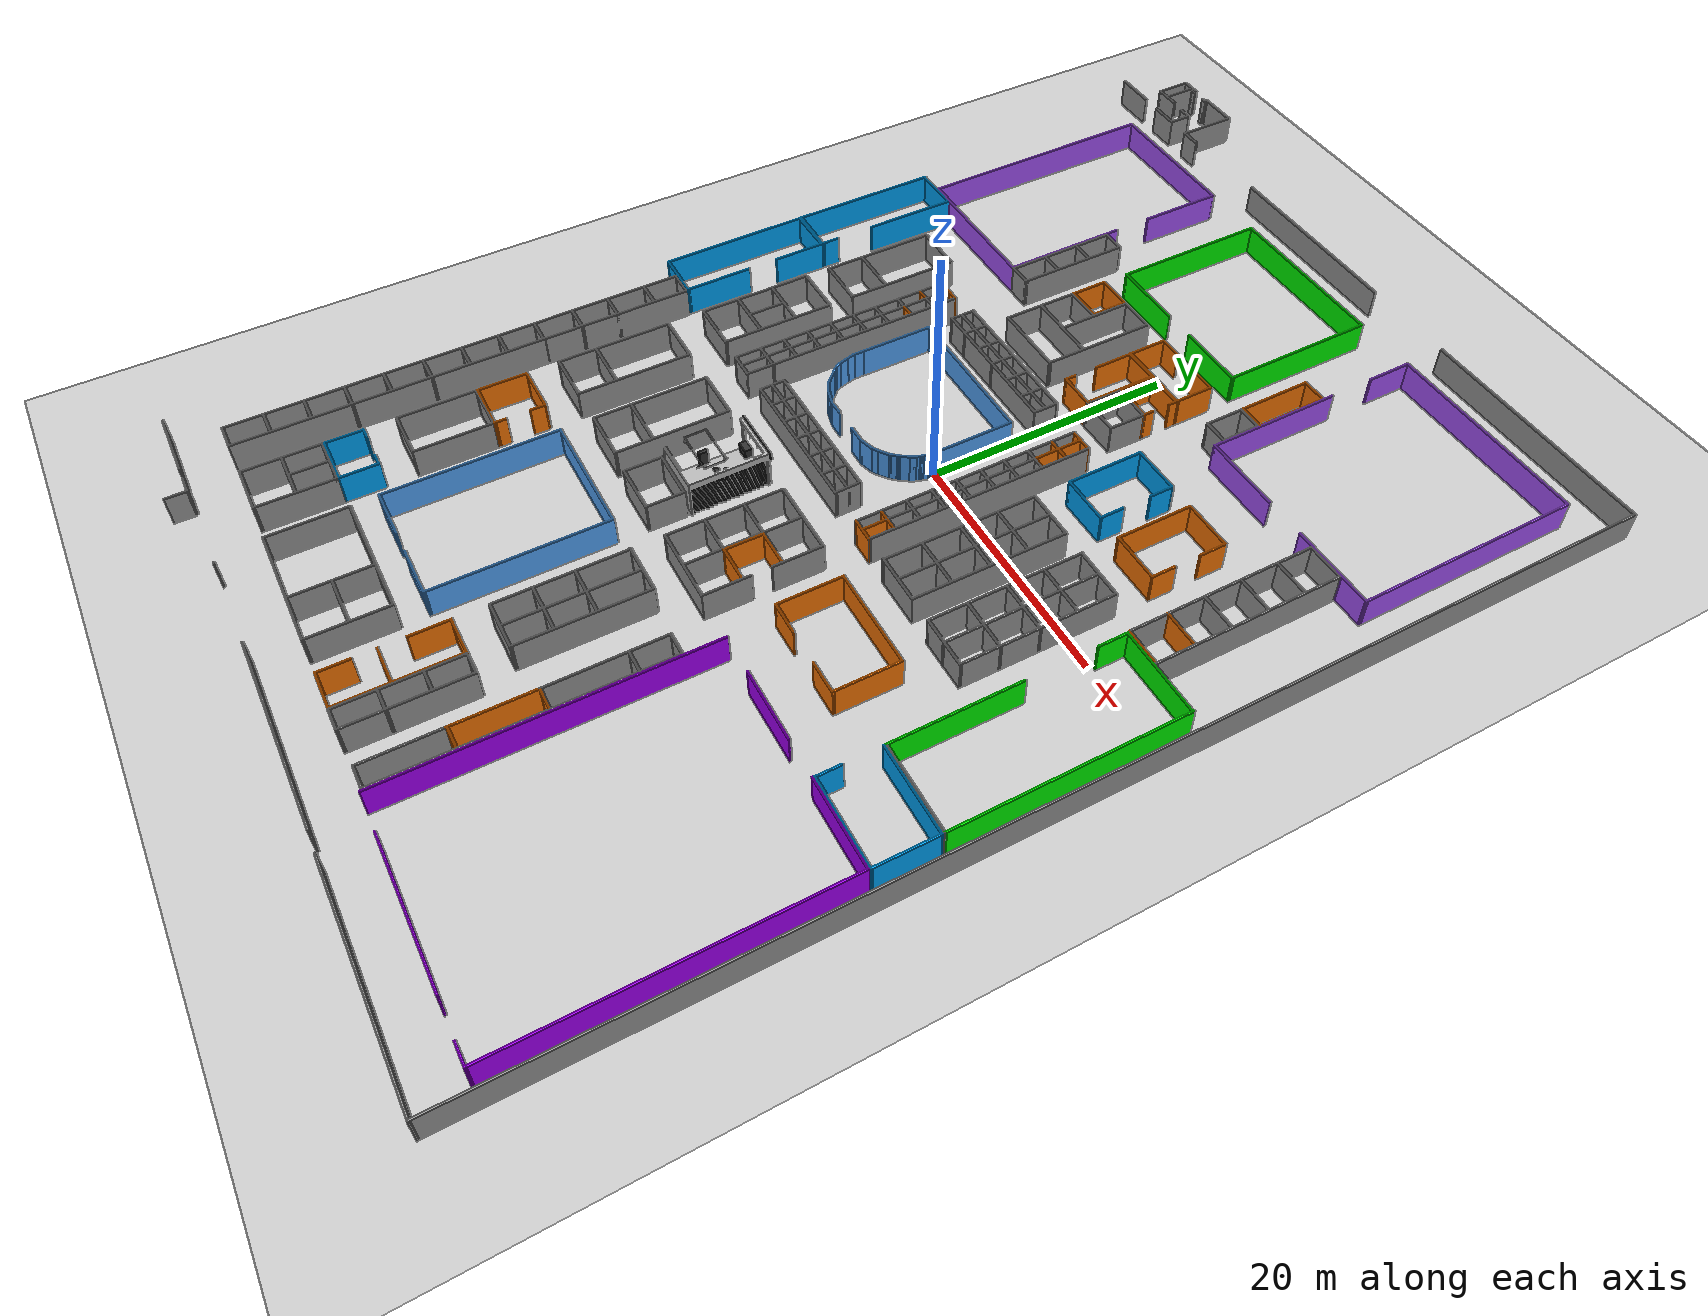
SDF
<?xml version="1.0" ?>
<sdf version="1.4">
  <world name="default">

    <include>
      <uri>model://ground_plane</uri>
    </include>

    <include>
      <uri>model://sun</uri>
    </include>

    <include>
      <uri>model://cr2_gazebo/models/lond_fintech2018/base</uri>
      <name>fintech</name>
    </include>

    <include>
      <uri>model://cr2_gazebo/models/lond_fintech2018/base_neighbour_box</uri>
      <name>neighbour_walls</name>
    </include>

    <include>
      <uri>model://cr2_gazebo/models/lond_fintech2018/construction</uri>
      <name>construction</name>
      <pose>-6.97021 -13.9566 1.6 0 0 -3.13304</pose>
    </include>

    <include>
      <uri>model://cr2_gazebo/models/lond_fintech2018/chair</uri>
      <name>chair</name>
      <pose>-6.20099 -14.6145 0.845384 0 -1.1e-05 -0.109586</pose>
    </include>

    <include>
      <uri>model://cr2_gazebo/models/lond_fintech2018/chair</uri>
      <name>chair_1</name>
      <pose>-6.83457 -15.4592 0.845381 5e-06 -1.2e-05 -0.110544</pose>
    </include>

    <include>
      <uri>model://cr2_gazebo/models/lond_fintech2018/chair</uri>
      <name>chair_2</name>
      <pose>-7.45906 -16.268 0.845381 2e-06 -1e-06 -0.110191</pose>
    </include>

    <include>
      <uri>model://cr2_gazebo/models/lond_fintech2018/chair</uri>
      <name>chair_3</name>
      <pose>-5.90723 -12.7074 0.845381 -2e-06 -3e-06 -0.109988</pose>
    </include>

    <include>
      <uri>model://cr2_gazebo/models/lond_fintech2018/chair</uri>
      <name>chair_4</name>
      <pose>-6.76208 -13.6221 0.84538 2e-06 -2e-06 -0.109909</pose>
    </include>

    <include>
      <uri>model://cr2_gazebo/models/lond_fintech2018/light_construction</uri>
      <name>light_construction</name>
      <pose>-7.166 -14.9 3.62658 0 -0 0.008388</pose>
    </include>

    <include>
      <uri>model://cr2_gazebo/models/lond_fintech2018/logo</uri>
      <name>logo</name>
      <pose>-8.2508 -10.7838 2.9 0 0 -3.12334</pose>
    </include>

    <include>
      <uri>model://cr2_gazebo/models/lond_fintech2018/louver</uri>
      <name>louver</name>
      <pose>-5.00702 -14.1027 1.22778 0 -0 0.007084</pose>
    </include>

    <include>
      <uri>model://cr2_gazebo/models/lond_fintech2018/table1</uri>
      <name>table1</name>
      <pose>-5.69254 -11.2204 0.556427 0 -0 0.008843</pose>
    </include>

    <include>
      <uri>model://cr2_gazebo/models/lond_fintech2018/table1</uri>
      <name>table1_1</name>
      <pose>-8.48022 -11.249 0.556428 0 -0 0.010465</pose>
    </include>

    <include>
      <uri>model://cr2_gazebo/models/lond_fintech2018/table2</uri>
      <name>table2</name>
      <pose>-9.01844 -14.4284 0.806477 3.14159 2e-06 0.003107</pose>
    </include>

    <include>
      <uri>model://cr2_gazebo/models/lond_fintech2018/hight_table</uri>
      <name>hight_table</name>
      <pose>-7.55928 -15.2541 0.886699 7e-06 -7e-06 1.71701</pose>
    </include>

    <include>
      <uri>model://cr2_gazebo/models/lond_fintech2018/hight_table</uri>
      <name>hight_table_1</name>
      <pose>-6.85374 -14.372 0.886696 8e-06 -6e-06 1.7163</pose>
    </include>

    <include>
      <uri>model://cr2_gazebo/models/lond_fintech2018/signboard</uri>
      <name>signboard</name>
      <pose>-7.10674 -10.837 2.84256 -0.031047 0.000713 -3.13229</pose>
    </include>

    <include>
      <uri>model://cr2_gazebo/models/lond_fintech2018/light</uri>
      <name>light_1_1</name>
      <pose>-8.76 -15.75 3.46 -1.55 -0 0.008388</pose>
    </include>

    <include>
      <uri>model://cr2_gazebo/models/lond_fintech2018/light</uri>
      <name>light_1_2</name>
      <pose>-5.77 -14.00 3.41 -1.57 -0 0.008388</pose>
    </include>

    <include>
      <uri>model://cr2_gazebo/models/lond_fintech2018/light</uri>
      <name>light_2_1</name>
      <pose>-5.34 -11.12 2.72 -0.35 0.01 -3.13</pose>
    </include>

    <include>
      <uri>model://cr2_gazebo/models/lond_fintech2018/light</uri>
      <name>light_2_2</name>
      <pose>-6.44 -11.12 2.72 -0.35 0.01 -3.13</pose>
    </include>

    <include>
      <uri>model://cr2_gazebo/models/lond_fintech2018/light</uri>
      <name>light_2_3</name>
      <pose>-7.55 -11.12 2.72 -0.35 0.01 -3.13</pose>
    </include>

    <include>
      <uri>model://cr2_gazebo/models/lond_fintech2018/light</uri>
      <name>light_2_4</name>
      <pose>-8.6 -11.19 2.72 -0.35 0.01 -3.13</pose>
    </include>

    <gui fullscreen='0'>
      <camera name='user_camera'>
        <pose>4.927360 -4.376610 3.740080 0.000000 0.275643 2.356190</pose>
        <view_controller>orbit</view_controller>
      </camera>
    </gui>

  </world>
</sdf>

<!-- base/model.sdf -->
<sdf version='1.6'>
  <model name='rebuilt_1'>
    <pose frame=''>-2.12726 -2.76078 0 0 -0 0</pose>
    <link name='Wall_0'>
      <collision name='Wall_0_Collision'>
        <geometry>
          <box>
            <size>14 0.15 2.5</size>
          </box>
        </geometry>
        <pose frame=''>0 0 1.25 0 -0 0</pose>
      </collision>
      <visual name='Wall_0_Visual'>
        <pose frame=''>0 0 1.25 0 -0 0</pose>
        <geometry>
          <box>
            <size>14 0.15 2.5</size>
          </box>
        </geometry>
        <material>
          <script>
            <uri>file://media/materials/scripts/gazebo.material</uri>
            <name>Gazebo/Grey</name>
          </script>
          <ambient>0 1 0 1</ambient>
        </material>
        <meta>
          <layer>0</layer>
        </meta>
      </visual>
      <pose frame=''>-0.804476 39.0362 0 0 -0 3.14159</pose>
    </link>
    <link name='Wall_1'>
      <collision name='Wall_1_Collision'>
        <geometry>
          <box>
            <size>12.75 0.15 2.5</size>
          </box>
        </geometry>
        <pose frame=''>0 0 1.25 0 -0 0</pose>
      </collision>
      <visual name='Wall_1_Visual'>
        <pose frame=''>0 0 1.25 0 -0 0</pose>
        <geometry>
          <box>
            <size>12.75 0.15 2.5</size>
          </box>
        </geometry>
        <material>
          <script>
            <uri>file://media/materials/scripts/gazebo.material</uri>
            <name>Gazebo/Grey</name>
          </script>
          <ambient>0 1 0 1</ambient>
        </material>
        <meta>
          <layer>0</layer>
        </meta>
      </visual>
      <pose frame=''>-7.72948 32.7362 0 0 0 -1.5708</pose>
    </link>
    <link name='Wall_100'>
      <collision name='Wall_100_Collision'>
        <geometry>
          <box>
            <size>7 0.15 2.5</size>
          </box>
        </geometry>
        <pose frame=''>0 0 1.25 0 -0 0</pose>
      </collision>
      <visual name='Wall_100_Visual'>
        <pose frame=''>0 0 1.25 0 -0 0</pose>
        <geometry>
          <box>
            <size>7 0.15 2.5</size>
          </box>
        </geometry>
        <material>
          <script>
            <uri>file://media/materials/scripts/gazebo.material</uri>
            <name>Gazebo/Grey</name>
          </script>
          <ambient>0.666667 0.333333 1 1</ambient>
        </material>
        <meta>
          <layer>0</layer>
        </meta>
      </visual>
      <pose frame=''>24.6152 20.8683 0 0 -0 3.14159</pose>
    </link>
    <link name='Wall_102'>
      <collision name='Wall_102_Collision'>
        <geometry>
          <box>
            <size>4.16873 0.15 2.5</size>
          </box>
        </geometry>
        <pose frame=''>0 0 1.25 0 -0 0</pose>
      </collision>
      <visual name='Wall_102_Visual'>
        <pose frame=''>0 0 1.25 0 -0 0</pose>
        <geometry>
          <box>
            <size>4.16873 0.15 2.5</size>
          </box>
        </geometry>
        <material>
          <script>
            <uri>file://media/materials/scripts/gazebo.material</uri>
            <name>Gazebo/Grey</name>
          </script>
          <ambient>0.996078 0.47451 0.0196078 1</ambient>
        </material>
        <meta>
          <layer>0</layer>
        </meta>
      </visual>
      <pose frame=''>17.4391 15.7517 0 0 -0 0</pose>
    </link>
    <link name='Wall_104'>
      <collision name='Wall_104_Collision'>
        <geometry>
          <box>
            <size>4.16873 0.15 2.5</size>
          </box>
        </geometry>
        <pose frame=''>0 0 1.25 0 -0 0</pose>
      </collision>
      <visual name='Wall_104_Visual'>
        <pose frame=''>0 0 1.25 0 -0 0</pose>
        <geometry>
          <box>
            <size>4.16873 0.15 2.5</size>
          </box>
        </geometry>
        <material>
          <script>
            <uri>file://media/materials/scripts/gazebo.material</uri>
            <name>Gazebo/Grey</name>
          </script>
          <ambient>0.996078 0.47451 0.0196078 1</ambient>
        </material>
        <meta>
          <layer>0</layer>
        </meta>
      </visual>
      <pose frame=''>17.4391 9.65173 0 0 0 -3.14159</pose>
    </link>
    <link name='Wall_105'>
      <collision name='Wall_105_Collision'>
        <geometry>
          <box>
            <size>6.25 0.15 2.5</size>
          </box>
        </geometry>
        <pose frame=''>0 0 1.25 0 -0 0</pose>
      </collision>
      <visual name='Wall_105_Visual'>
        <pose frame=''>0 0 1.25 0 -0 0</pose>
        <geometry>
          <box>
            <size>6.25 0.15 2.5</size>
          </box>
        </geometry>
        <material>
          <script>
            <uri>file://media/materials/scripts/gazebo.material</uri>
            <name>Gazebo/Grey</name>
          </script>
          <ambient>0.996078 0.47451 0.0196078 1</ambient>
        </material>
        <meta>
          <layer>0</layer>
        </meta>
      </visual>
      <pose frame=''>15.4298 12.7017 0 0 -0 1.5708</pose>
    </link>
    <link name='Wall_107'>
      <collision name='Wall_107_Collision'>
        <geometry>
          <box>
            <size>2.25 0.15 2.5</size>
          </box>
        </geometry>
        <pose frame=''>0 0 1.25 0 -0 0</pose>
      </collision>
      <visual name='Wall_107_Visual'>
        <pose frame=''>0 0 1.25 0 -0 0</pose>
        <geometry>
          <box>
            <size>2.25 0.15 2.5</size>
          </box>
        </geometry>
        <material>
          <script>
            <uri>file://media/materials/scripts/gazebo.material</uri>
            <name>Gazebo/Grey</name>
          </script>
          <ambient>0.996078 0.47451 0.0196078 1</ambient>
        </material>
        <meta>
          <layer>0</layer>
        </meta>
      </visual>
      <pose frame=''>19.4485 14.7017 0 0 0 -1.5708</pose>
    </link>
    <link name='Wall_109'>
      <collision name='Wall_109_Collision'>
        <geometry>
          <box>
            <size>2 0.15 2.5</size>
          </box>
        </geometry>
        <pose frame=''>0 0 1.25 0 -0 0</pose>
      </collision>
      <visual name='Wall_109_Visual'>
        <pose frame=''>0 0 1.25 0 -0 0</pose>
        <geometry>
          <box>
            <size>2 0.15 2.5</size>
          </box>
        </geometry>
        <material>
          <script>
            <uri>file://media/materials/scripts/gazebo.material</uri>
            <name>Gazebo/Grey</name>
          </script>
          <ambient>0.996078 0.47451 0.0196078 1</ambient>
        </material>
        <meta>
          <layer>0</layer>
        </meta>
      </visual>
      <pose frame=''>19.4485 10.5767 0 0 -0 1.5708</pose>
    </link>
    <link name='Wall_11'>
      <collision name='Wall_11_Collision'>
        <geometry>
          <box>
            <size>18.3877 0.15 2.5</size>
          </box>
        </geometry>
        <pose frame=''>0 0 1.25 0 -0 0</pose>
      </collision>
      <visual name='Wall_11_Visual'>
        <pose frame=''>0 0 1.25 0 -0 0</pose>
        <geometry>
          <box>
            <size>18.3877 0.15 2.5</size>
          </box>
        </geometry>
        <material>
          <script>
            <uri>file://media/materials/scripts/gazebo.material</uri>
            <name>Gazebo/Grey</name>
          </script>
          <ambient>0.666667 0.333333 1 1</ambient>
        </material>
        <meta>
          <layer>0</layer>
        </meta>
      </visual>
      <pose frame=''>28.0372 29.9871 0 0 0 -1.57047</pose>
    </link>
    <link name='Wall_111'>
      <collision name='Wall_111_Collision'>
        <geometry>
          <box>
            <size>4.0365 0.15 2.5</size>
          </box>
        </geometry>
        <pose frame=''>0 0 1.25 0 -0 0</pose>
      </collision>
      <visual name='Wall_111_Visual'>
        <pose frame=''>0 0 1.25 0 -0 0</pose>
        <geometry>
          <box>
            <size>4.0365 0.15 2.5</size>
          </box>
        </geometry>
        <material>
          <script>
            <uri>file://media/materials/scripts/gazebo.material</uri>
            <name>Gazebo/Grey</name>
          </script>
          <ambient>0 0.666667 1 1</ambient>
        </material>
        <meta>
          <layer>0</layer>
        </meta>
      </visual>
      <pose frame=''>11.3657 15.726 0 0 -0 0.00469</pose>
    </link>
    <link name='Wall_113'>
      <collision name='Wall_113_Collision'>
        <geometry>
          <box>
            <size>4.0365 0.15 2.5</size>
          </box>
        </geometry>
        <pose frame=''>0 0 1.25 0 -0 0</pose>
      </collision>
      <visual name='Wall_113_Visual'>
        <pose frame=''>0 0 1.25 0 -0 0</pose>
        <geometry>
          <box>
            <size>4.0365 0.15 2.5</size>
          </box>
        </geometry>
        <material>
          <script>
            <uri>file://media/materials/scripts/gazebo.material</uri>
            <name>Gazebo/Grey</name>
          </script>
          <ambient>0 0.666667 1 1</ambient>
        </material>
        <meta>
          <layer>0</layer>
        </meta>
      </visual>
      <pose frame=''>11.3657 9.62598 0 0 0 -3.1369</pose>
    </link>
    <link name='Wall_114'>
      <collision name='Wall_114_Collision'>
        <geometry>
          <box>
            <size>6.25 0.15 2.5</size>
          </box>
        </geometry>
        <pose frame=''>0 0 1.25 0 -0 0</pose>
      </collision>
      <visual name='Wall_114_Visual'>
        <pose frame=''>0 0 1.25 0 -0 0</pose>
        <geometry>
          <box>
            <size>6.25 0.15 2.5</size>
          </box>
        </geometry>
        <material>
          <script>
            <uri>file://media/materials/scripts/gazebo.material</uri>
            <name>Gazebo/Grey</name>
          </script>
          <ambient>0 0.666667 1 1</ambient>
        </material>
        <meta>
          <layer>0</layer>
        </meta>
      </visual>
      <pose frame=''>9.40422 12.6669 0 0 -0 1.5708</pose>
    </link>
    <link name='Wall_116'>
      <collision name='Wall_116_Collision'>
        <geometry>
          <box>
            <size>2 0.15 2.5</size>
          </box>
        </geometry>
        <pose frame=''>0 0 1.25 0 -0 0</pose>
      </collision>
      <visual name='Wall_116_Visual'>
        <pose frame=''>0 0 1.25 0 -0 0</pose>
        <geometry>
          <box>
            <size>2 0.15 2.5</size>
          </box>
        </geometry>
        <material>
          <script>
            <uri>file://media/materials/scripts/gazebo.material</uri>
            <name>Gazebo/Grey</name>
          </script>
          <ambient>0 0.666667 1 1</ambient>
        </material>
        <meta>
          <layer>0</layer>
        </meta>
      </visual>
      <pose frame=''>13.3089 10.5601 0 0 -0 1.5708</pose>
    </link>
    <link name='Wall_118'>
      <collision name='Wall_118_Collision'>
        <geometry>
          <box>
            <size>2 0.15 2.5</size>
          </box>
        </geometry>
        <pose frame=''>0 0 1.25 0 -0 0</pose>
      </collision>
      <visual name='Wall_118_Visual'>
        <pose frame=''>0 0 1.25 0 -0 0</pose>
        <geometry>
          <box>
            <size>2 0.15 2.5</size>
          </box>
        </geometry>
        <material>
          <script>
            <uri>file://media/materials/scripts/gazebo.material</uri>
            <name>Gazebo/Grey</name>
          </script>
          <ambient>0 0.666667 1 1</ambient>
        </material>
        <meta>
          <layer>0</layer>
        </meta>
      </visual>
      <pose frame=''>13.3089 14.8101 0 0 0 -1.5708</pose>
    </link>
    <link name='Wall_124'>
      <collision name='Wall_124_Collision'>
        <geometry>
          <box>
            <size>3.13547 0.15 2.5</size>
          </box>
        </geometry>
        <pose frame=''>0 0 1.25 0 -0 0</pose>
      </collision>
      <visual name='Wall_124_Visual'>
        <pose frame=''>0 0 1.25 0 -0 0</pose>
        <geometry>
          <box>
            <size>3.13547 0.15 2.5</size>
          </box>
        </geometry>
        <material>
          <script>
            <uri>file://media/materials/scripts/gazebo.material</uri>
            <name>Gazebo/Grey</name>
          </script>
          <ambient>1 1 1 1</ambient>
        </material>
        <meta>
          <layer>0</layer>
        </meta>
      </visual>
      <pose frame=''>24.0269 20.7273 0 0 -0 0</pose>
    </link>
    <link name='Wall_13'>
      <collision name='Wall_13_Collision'>
        <geometry>
          <box>
            <size>11 0.15 2.5</size>
          </box>
        </geometry>
        <pose frame=''>0 0 1.25 0 -0 0</pose>
      </collision>
      <visual name='Wall_13_Visual'>
        <pose frame=''>0 0 1.25 0 -0 0</pose>
        <geometry>
          <box>
            <size>11 0.15 2.5</size>
          </box>
        </geometry>
        <material>
          <script>
            <uri>file://media/materials/scripts/gazebo.material</uri>
            <name>Gazebo/Grey</name>
          </script>
          <ambient>0.666667 0.333333 1 1</ambient>
        </material>
        <meta>
          <layer>0</layer>
        </meta>
      </visual>
      <pose frame=''>11.4402 26.2933 0 0 -0 1.5708</pose>
    </link>
    <link name='Wall_133'>
      <collision name='Wall_133_Collision'>
        <geometry>
          <box>
            <size>15.25 0.15 2.5</size>
          </box>
        </geometry>
        <pose frame=''>0 0 1.25 0 -0 0</pose>
      </collision>
      <visual name='Wall_133_Visual'>
        <pose frame=''>0 0 1.25 0 -0 0</pose>
        <geometry>
          <box>
            <size>15.25 0.15 2.5</size>
          </box>
        </geometry>
        <material>
          <script>
            <uri>file://media/materials/scripts/gazebo.material</uri>
            <name>Gazebo/Grey</name>
          </script>
          <ambient>1 1 1 1</ambient>
        </material>
        <meta>
          <layer>0</layer>
        </meta>
      </visual>
      <pose frame=''>22.5342 13.1773 0 0 0 -1.5708</pose>
    </link>
    <link name='Wall_135'>
      <collision name='Wall_135_Collision'>
        <geometry>
          <box>
            <size>15.25 0.15 2.5</size>
          </box>
        </geometry>
        <pose frame=''>0 0 1.25 0 -0 0</pose>
      </collision>
      <visual name='Wall_135_Visual'>
        <pose frame=''>0 0 1.25 0 -0 0</pose>
        <geometry>
          <box>
            <size>15.25 0.15 2.5</size>
          </box>
        </geometry>
        <material>
          <script>
            <uri>file://media/materials/scripts/gazebo.material</uri>
            <name>Gazebo/Grey</name>
          </script>
          <ambient>1 1 1 1</ambient>
        </material>
        <meta>
          <layer>0</layer>
        </meta>
      </visual>
      <pose frame=''>25.5196 13.1773 0 0 0 -1.5708</pose>
    </link>
    <link name='Wall_137'>
      <collision name='Wall_137_Collision'>
        <geometry>
          <box>
            <size>3 0.15 2.5</size>
          </box>
        </geometry>
        <pose frame=''>0 0 1.25 0 -0 0</pose>
      </collision>
      <visual name='Wall_137_Visual'>
        <pose frame=''>0 0 1.25 0 -0 0</pose>
        <geometry>
          <box>
            <size>3 0.15 2.5</size>
          </box>
        </geometry>
        <material>
          <script>
            <uri>file://media/materials/scripts/gazebo.material</uri>
            <name>Gazebo/Grey</name>
          </script>
          <ambient>0.996078 0.47451 0.0196078 1</ambient>
        </material>
        <meta>
          <layer>0</layer>
        </meta>
      </visual>
      <pose frame=''>23.9592 5.62733 0 0 -0 0</pose>
    </link>
    <link name='Wall_139'>
      <collision name='Wall_139_Collision'>
        <geometry>
          <box>
            <size>3 0.15 2.5</size>
          </box>
        </geometry>
        <pose frame=''>0 0 1.25 0 -0 0</pose>
      </collision>
      <visual name='Wall_139_Visual'>
        <pose frame=''>0 0 1.25 0 -0 0</pose>
        <geometry>
          <box>
            <size>3 0.15 2.5</size>
          </box>
        </geometry>
        <material>
          <script>
            <uri>file://media/materials/scripts/gazebo.material</uri>
            <name>Gazebo/Grey</name>
          </script>
          <ambient>0.996078 0.47451 0.0196078 1</ambient>
        </material>
        <meta>
          <layer>0</layer>
        </meta>
      </visual>
      <pose frame=''>23.9621 8.72528 0 0 -0 0</pose>
    </link>
    <link name='Wall_141'>
      <collision name='Wall_141_Collision'>
        <geometry>
          <box>
            <size>3 0.15 2.5</size>
          </box>
        </geometry>
        <pose frame=''>0 0 1.25 0 -0 0</pose>
      </collision>
      <visual name='Wall_141_Visual'>
        <pose frame=''>0 0 1.25 0 -0 0</pose>
        <geometry>
          <box>
            <size>3 0.15 2.5</size>
          </box>
        </geometry>
        <material>
          <script>
            <uri>file://media/materials/scripts/gazebo.material</uri>
            <name>Gazebo/Grey</name>
          </script>
          <ambient>1 1 1 1</ambient>
        </material>
        <meta>
          <layer>0</layer>
        </meta>
      </visual>
      <pose frame=''>23.9803 11.6962 0 0 -0 0</pose>
    </link>
    <link name='Wall_143'>
      <collision name='Wall_143_Collision'>
        <geometry>
          <box>
            <size>3 0.15 2.5</size>
          </box>
        </geometry>
        <pose frame=''>0 0 1.25 0 -0 0</pose>
      </collision>
      <visual name='Wall_143_Visual'>
        <pose frame=''>0 0 1.25 0 -0 0</pose>
        <geometry>
          <box>
            <size>3 0.15 2.5</size>
          </box>
        </geometry>
        <material>
          <script>
            <uri>file://media/materials/scripts/gazebo.material</uri>
            <name>Gazebo/Grey</name>
          </script>
          <ambient>1 1 1 1</ambient>
        </material>
        <meta>
          <layer>0</layer>
        </meta>
      </visual>
      <pose frame=''>24.0168 14.7218 0 0 -0 0</pose>
    </link>
    <link name='Wall_145'>
      <collision name='Wall_145_Collision'>
        <geometry>
          <box>
            <size>3 0.15 2.5</size>
          </box>
        </geometry>
        <pose frame=''>0 0 1.25 0 -0 0</pose>
      </collision>
      <visual name='Wall_145_Visual'>
        <pose frame=''>0 0 1.25 0 -0 0</pose>
        <geometry>
          <box>
            <size>3 0.15 2.5</size>
          </box>
        </geometry>
        <material>
          <script>
            <uri>file://media/materials/scripts/gazebo.material</uri>
            <name>Gazebo/Grey</name>
          </script>
          <ambient>1 1 1 1</ambient>
        </material>
        <meta>
          <layer>0</layer>
        </meta>
      </visual>
      <pose frame=''>23.9986 17.7839 0 0 -0 0</pose>
    </link>
    <link name='Wall_147'>
      <collision name='Wall_147_Collision'>
        <geometry>
          <box>
            <size>4.25 0.15 2.5</size>
          </box>
        </geometry>
        <pose frame=''>0 0 1.25 0 -0 0</pose>
      </collision>
      <visual name='Wall_147_Visual'>
        <pose frame=''>0 0 1.25 0 -0 0</pose>
        <geometry>
          <box>
            <size>4.25 0.15 2.5</size>
          </box>
        </geometry>
        <material>
          <script>
            <uri>file://media/materials/scripts/gazebo.material</uri>
            <name>Gazebo/Grey</name>
          </script>
          <ambient>1 1 1 1</ambient>
        </material>
        <meta>
          <layer>0</layer>
        </meta>
      </visual>
      <pose frame=''>17.4545 6.6361 0 0 -0 0</pose>
    </link>
    <link name='Wall_148'>
      <collision name='Wall_148_Collision'>
        <geometry>
          <box>
            <size>12.25 0.15 2.5</size>
          </box>
        </geometry>
        <pose frame=''>0 0 1.25 0 -0 0</pose>
      </collision>
      <visual name='Wall_148_Visual'>
        <pose frame=''>0 0 1.25 0 -0 0</pose>
        <geometry>
          <box>
            <size>12.25 0.15 2.5</size>
          </box>
        </geometry>
        <material>
          <script>
            <uri>file://media/materials/scripts/gazebo.material</uri>
            <name>Gazebo/Grey</name>
          </script>
          <ambient>1 1 1 1</ambient>
        </material>
        <meta>
          <layer>0</layer>
        </meta>
      </visual>
      <pose frame=''>19.5045 0.586104 0 0 0 -1.5708</pose>
    </link>
    <link name='Wall_149'>
      <collision name='Wall_149_Collision'>
        <geometry>
          <box>
            <size>4.25 0.15 2.5</size>
          </box>
        </geometry>
        <pose frame=''>0 0 1.25 0 -0 0</pose>
      </collision>
      <visual name='Wall_149_Visual'>
        <pose frame=''>0 0 1.25 0 -0 0</pose>
        <geometry>
          <box>
            <size>4.25 0.15 2.5</size>
          </box>
        </geometry>
        <material>
          <script>
            <uri>file://media/materials/scripts/gazebo.material</uri>
            <name>Gazebo/Grey</name>
          </script>
          <ambient>1 1 1 1</ambient>
        </material>
        <meta>
          <layer>0</layer>
        </meta>
      </visual>
      <pose frame=''>17.4545 -5.4639 0 0 -0 3.14159</pose>
    </link>
    <link name='Wall_150'>
      <collision name='Wall_150_Collision'>
        <geometry>
          <box>
            <size>12.25 0.15 2.5</size>
          </box>
        </geometry>
        <pose frame=''>0 0 1.25 0 -0 0</pose>
      </collision>
      <visual name='Wall_150_Visual'>
        <pose frame=''>0 0 1.25 0 -0 0</pose>
        <geometry>
          <box>
            <size>12.25 0.15 2.5</size>
          </box>
        </geometry>
        <material>
          <script>
            <uri>file://media/materials/scripts/gazebo.material</uri>
            <name>Gazebo/Grey</name>
          </script>
          <ambient>1 1 1 1</ambient>
        </material>
        <meta>
          <layer>0</layer>
        </meta>
      </visual>
      <pose frame=''>15.4045 0.586104 0 0 -0 1.5708</pose>
    </link>
    <link name='Wall_152'>
      <collision name='Wall_152_Collision'>
        <geometry>
          <box>
            <size>12.25 0.15 2.5</size>
          </box>
        </geometry>
        <pose frame=''>0 0 1.25 0 -0 0</pose>
      </collision>
      <visual name='Wall_152_Visual'>
        <pose frame=''>0 0 1.25 0 -0 0</pose>
        <geometry>
          <box>
            <size>12.25 0.15 2.5</size>
          </box>
        </geometry>
        <material>
          <script>
            <uri>file://media/materials/scripts/gazebo.material</uri>
            <name>Gazebo/Grey</name>
          </script>
          <ambient>1 1 1 1</ambient>
        </material>
        <meta>
          <layer>0</layer>
        </meta>
      </visual>
      <pose frame=''>17.4706 0.558918 0 0 0 -1.5708</pose>
    </link>
    <link name='Wall_154'>
      <collision name='Wall_154_Collision'>
        <geometry>
          <box>
            <size>4.25 0.15 2.5</size>
          </box>
        </geometry>
        <pose frame=''>0 0 1.25 0 -0 0</pose>
      </collision>
      <visual name='Wall_154_Visual'>
        <pose frame=''>0 0 1.25 0 -0 0</pose>
        <geometry>
          <box>
            <size>4.25 0.15 2.5</size>
          </box>
        </geometry>
        <material>
          <script>
            <uri>file://media/materials/scripts/gazebo.material</uri>
            <name>Gazebo/Grey</name>
          </script>
          <ambient>1 1 1 1</ambient>
        </material>
        <meta>
          <layer>0</layer>
        </meta>
      </visual>
      <pose frame=''>17.4545 3.59133 0 0 -0 0</pose>
    </link>
    <link name='Wall_156'>
      <collision name='Wall_156_Collision'>
        <geometry>
          <box>
            <size>4.25 0.15 2.5</size>
          </box>
        </geometry>
        <pose frame=''>0 0 1.25 0 -0 0</pose>
      </collision>
      <visual name='Wall_156_Visual'>
        <pose frame=''>0 0 1.25 0 -0 0</pose>
        <geometry>
          <box>
            <size>4.25 0.15 2.5</size>
          </box>
        </geometry>
        <material>
          <script>
            <uri>file://media/materials/scripts/gazebo.material</uri>
            <name>Gazebo/Grey</name>
          </script>
          <ambient>1 1 1 1</ambient>
        </material>
        <meta>
          <layer>0</layer>
        </meta>
      </visual>
      <pose frame=''>17.4582 0.624429 0 0 -0 0</pose>
    </link>
    <link name='Wall_158'>
      <collision name='Wall_158_Collision'>
        <geometry>
          <box>
            <size>4.25 0.15 2.5</size>
          </box>
        </geometry>
        <pose frame=''>0 0 1.25 0 -0 0</pose>
      </collision>
      <visual name='Wall_158_Visual'>
        <pose frame=''>0 0 1.25 0 -0 0</pose>
        <geometry>
          <box>
            <size>4.25 0.15 2.5</size>
          </box>
        </geometry>
        <material>
          <script>
            <uri>file://media/materials/scripts/gazebo.material</uri>
            <name>Gazebo/Grey</name>
          </script>
          <ambient>1 1 1 1</ambient>
        </material>
        <meta>
          <layer>0</layer>
        </meta>
      </visual>
      <pose frame=''>17.4619 -2.44385 0 0 -0 0</pose>
    </link>
    <link name='Wall_168'>
      <collision name='Wall_168_Collision'>
        <geometry>
          <box>
            <size>8.25 0.15 2.5</size>
          </box>
        </geometry>
        <pose frame=''>0 0 1.25 0 -0 0</pose>
      </collision>
      <visual name='Wall_168_Visual'>
        <pose frame=''>0 0 1.25 0 -0 0</pose>
        <geometry>
          <box>
            <size>8.25 0.15 2.5</size>
          </box>
        </geometry>
        <material>
          <script>
            <uri>file://media/materials/scripts/gazebo.material</uri>
            <name>Gazebo/Grey</name>
          </script>
          <ambient>0.996078 0.47451 0.0196078 1</ambient>
        </material>
        <meta>
          <layer>0</layer>
        </meta>
      </visual>
      <pose frame=''>13.4258 -8.56236 0 0 -0 0</pose>
    </link>
    <link name='Wall_169'>
      <collision name='Wall_169_Collision'>
        <geometry>
          <box>
            <size>5.25 0.15 2.5</size>
          </box>
        </geometry>
        <pose frame=''>0 0 1.25 0 -0 0</pose>
      </collision>
      <visual name='Wall_169_Visual'>
        <pose frame=''>0 0 1.25 0 -0 0</pose>
        <geometry>
          <box>
            <size>5.25 0.15 2.5</size>
          </box>
        </geometry>
        <material>
          <script>
            <uri>file://media/materials/scripts/gazebo.material</uri>
            <name>Gazebo/Grey</name>
          </script>
          <ambient>0.996078 0.47451 0.0196078 1</ambient>
        </material>
        <meta>
          <layer>0</layer>
        </meta>
      </visual>
      <pose frame=''>17.4758 -11.1124 0 0 0 -1.5708</pose>
    </link>
    <link name='Wall_171'>
      <collision name='Wall_171_Collision'>
        <geometry>
          <box>
            <size>5.25 0.15 2.5</size>
          </box>
        </geometry>
        <pose frame=''>0 0 1.25 0 -0 0</pose>
      </collision>
      <visual name='Wall_171_Visual'>
        <pose frame=''>0 0 1.25 0 -0 0</pose>
        <geometry>
          <box>
            <size>5.25 0.15 2.5</size>
          </box>
        </geometry>
        <material>
          <script>
            <uri>file://media/materials/scripts/gazebo.material</uri>
            <name>Gazebo/Grey</name>
          </script>
          <ambient>0.996078 0.47451 0.0196078 1</ambient>
        </material>
        <meta>
          <layer>0</layer>
        </meta>
      </visual>
      <pose frame=''>9.37576 -11.1124 0 0 -0 1.5708</pose>
    </link>
    <link name='Wall_173'>
      <collision name='Wall_173_Collision'>
        <geometry>
          <box>
            <size>2.75 0.15 2.5</size>
          </box>
        </geometry>
        <pose frame=''>0 0 1.25 0 -0 0</pose>
      </collision>
      <visual name='Wall_173_Visual'>
        <pose frame=''>0 0 1.25 0 -0 0</pose>
        <geometry>
          <box>
            <size>2.75 0.15 2.5</size>
          </box>
        </geometry>
        <material>
          <script>
            <uri>file://media/materials/scripts/gazebo.material</uri>
            <name>Gazebo/Grey</name>
          </script>
          <ambient>0.996078 0.47451 0.0196078 1</ambient>
        </material>
        <meta>
          <layer>0</layer>
        </meta>
      </visual>
      <pose frame=''>10.6758 -13.6624 0 0 -0 0</pose>
    </link>
    <link name='Wall_175'>
      <collision name='Wall_175_Collision'>
        <geometry>
          <box>
            <size>2.75 0.15 2.5</size>
          </box>
        </geometry>
        <pose frame=''>0 0 1.25 0 -0 0</pose>
      </collision>
      <visual name='Wall_175_Visual'>
        <pose frame=''>0 0 1.25 0 -0 0</pose>
        <geometry>
          <box>
            <size>2.75 0.15 2.5</size>
          </box>
        </geometry>
        <material>
          <script>
            <uri>file://media/materials/scripts/gazebo.material</uri>
            <name>Gazebo/Grey</name>
          </script>
          <ambient>0.996078 0.47451 0.0196078 1</ambient>
        </material>
        <meta>
          <layer>0</layer>
        </meta>
      </visual>
      <pose frame=''>16.1758 -13.6624 0 0 -0 3.14159</pose>
    </link>
    <link name='Wall_177'>
      <collision name='Wall_177_Collision'>
        <geometry>
          <box>
            <size>6 0.15 2.5</size>
          </box>
        </geometry>
        <pose frame=''>0 0 1.25 0 -0 0</pose>
      </collision>
      <visual name='Wall_177_Visual'>
        <pose frame=''>0 0 1.25 0 -0 0</pose>
        <geometry>
          <box>
            <size>6 0.15 2.5</size>
          </box>
        </geometry>
        <material>
          <script>
            <uri>file://media/materials/scripts/gazebo.material</uri>
            <name>Gazebo/Grey</name>
          </script>
          <ambient>0.666667 0 1 1</ambient>
        </material>
        <meta>
          <layer>0</layer>
        </meta>
      </visual>
      <pose frame=''>16.3827 -17.6674 0 0 -0 0</pose>
    </link>
    <link name='Wall_181'>
      <collision name='Wall_181_Collision'>
        <geometry>
          <box>
            <size>7.25 0.15 2.5</size>
          </box>
        </geometry>
        <pose frame=''>0 0 1.25 0 -0 0</pose>
      </collision>
      <visual name='Wall_181_Visual'>
        <pose frame=''>0 0 1.25 0 -0 0</pose>
        <geometry>
          <box>
            <size>7.25 0.15 2.5</size>
          </box>
        </geometry>
        <material>
          <script>
            <uri>file://media/materials/scripts/gazebo.material</uri>
            <name>Gazebo/Grey</name>
          </script>
          <ambient>0.666667 0 1 1</ambient>
        </material>
        <meta>
          <layer>0</layer>
        </meta>
      </visual>
      <pose frame=''>26.0779 -17.6626 0 0 -0 0</pose>
    </link>
    <link name='Wall_183'>
      <collision name='Wall_183_Collision'>
        <geometry>
          <box>
            <size>24.5047 0.15 2.5</size>
          </box>
        </geometry>
        <pose frame=''>0 0 1.25 0 -0 0</pose>
      </collision>
      <visual name='Wall_183_Visual'>
        <pose frame=''>0 0 1.25 0 -0 0</pose>
        <geometry>
          <box>
            <size>24.5047 0.15 2.5</size>
          </box>
        </geometry>
        <material>
          <script>
            <uri>file://media/materials/scripts/gazebo.material</uri>
            <name>Gazebo/Grey</name>
          </script>
          <ambient>0.666667 0 1 1</ambient>
        </material>
        <meta>
          <layer>0</layer>
        </meta>
      </visual>
      <pose frame=''>29.6489 -29.8583 0 0 0 -1.56908</pose>
    </link>
    <link name='Wall_185'>
      <collision name='Wall_185_Collision'>
        <geometry>
          <box>
            <size>24.5 0.15 2.5</size>
          </box>
        </geometry>
        <pose frame=''>0 0 1.25 0 -0 0</pose>
      </collision>
      <visual name='Wall_185_Visual'>
        <pose frame=''>0 0 1.25 0 -0 0</pose>
        <geometry>
          <box>
            <size>24.5 0.15 2.5</size>
          </box>
        </geometry>
        <material>
          <script>
            <uri>file://media/materials/scripts/gazebo.material</uri>
            <name>Gazebo/Grey</name>
          </script>
          <ambient>0.666667 0 1 1</ambient>
        </material>
        <meta>
          <layer>0</layer>
        </meta>
      </visual>
      <pose frame=''>10.2779 -29.838 0 0 -0 1.5708</pose>
    </link>
    <link name='Wall_195'>
      <collision name='Wall_195_Collision'>
        <geometry>
          <box>
            <size>2 0.15 2.5</size>
          </box>
        </geometry>
        <pose frame=''>0 0 1.25 0 -0 0</pose>
      </collision>
      <visual name='Wall_195_Visual'>
        <pose frame=''>0 0 1.25 0 -0 0</pose>
        <geometry>
          <box>
            <size>2 0.15 2.5</size>
          </box>
        </geometry>
        <material>
          <script>
            <uri>file://media/materials/scripts/gazebo.material</uri>
            <name>Gazebo/Grey</name>
          </script>
          <ambient>1 1 1 1</ambient>
        </material>
        <meta>
          <layer>0</layer>
        </meta>
      </visual>
      <pose frame=''>9.22824 -41.8686 0 0 -0 0</pose>
    </link>
    <link name='Wall_196'>
      <collision name='Wall_196_Collision'>
        <geometry>
          <box>
            <size>21.25 0.15 2.5</size>
          </box>
        </geometry>
        <pose frame=''>0 0 1.25 0 -0 0</pose>
      </collision>
      <visual name='Wall_196_Visual'>
        <pose frame=''>0 0 1.25 0 -0 0</pose>
        <geometry>
          <box>
            <size>21.25 0.15 2.5</size>
          </box>
        </geometry>
        <material>
          <script>
            <uri>file://media/materials/scripts/gazebo.material</uri>
            <name>Gazebo/Grey</name>
          </script>
          <ambient>1 1 1 1</ambient>
        </material>
        <meta>
          <layer>0</layer>
        </meta>
      </visual>
      <pose frame=''>10.1532 -31.3186 0 0 -0 1.5708</pose>
    </link>
    <link name='Wall_198'>
      <collision name='Wall_198_Collision'>
        <geometry>
          <box>
            <size>2 0.15 2.5</size>
          </box>
        </geometry>
        <pose frame=''>0 0 1.25 0 -0 0</pose>
      </collision>
      <visual name='Wall_198_Visual'>
        <pose frame=''>0 0 1.25 0 -0 0</pose>
        <geometry>
          <box>
            <size>2 0.15 2.5</size>
          </box>
        </geometry>
        <material>
          <script>
            <uri>file://media/materials/scripts/gazebo.material</uri>
            <name>Gazebo/Grey</name>
          </script>
          <ambient>1 1 1 1</ambient>
        </material>
        <meta>
          <layer>0</layer>
        </meta>
      </visual>
      <pose frame=''>9.22824 -20.7686 0 0 -0 0</pose>
    </link>
    <link name='Wall_200'>
      <collision name='Wall_200_Collision'>
        <geometry>
          <box>
            <size>2 0.15 2.5</size>
          </box>
        </geometry>
        <pose frame=''>0 0 1.25 0 -0 0</pose>
      </collision>
      <visual name='Wall_200_Visual'>
        <pose frame=''>0 0 1.25 0 -0 0</pose>
        <geometry>
          <box>
            <size>2 0.15 2.5</size>
          </box>
        </geometry>
        <material>
          <script>
            <uri>file://media/materials/scripts/gazebo.material</uri>
            <name>Gazebo/Grey</name>
          </script>
          <ambient>1 1 1 1</ambient>
        </material>
        <meta>
          <layer>0</layer>
        </meta>
      </visual>
      <pose frame=''>9.25811 -23.7223 0 0 -0 0</pose>
    </link>
    <link name='Wall_202'>
      <collision name='Wall_202_Collision'>
        <geometry>
          <box>
            <size>2 0.15 2.5</size>
          </box>
        </geometry>
        <pose frame=''>0 0 1.25 0 -0 0</pose>
      </collision>
      <visual name='Wall_202_Visual'>
        <pose frame=''>0 0 1.25 0 -0 0</pose>
        <geometry>
          <box>
            <size>2 0.15 2.5</size>
          </box>
        </geometry>
        <material>
          <script>
            <uri>file://media/materials/scripts/gazebo.material</uri>
            <name>Gazebo/Grey</name>
          </script>
          <ambient>0.996078 0.47451 0.0196078 1</ambient>
        </material>
        <meta>
          <layer>0</layer>
        </meta>
      </visual>
      <pose frame=''>9.25038 -29.8125 0 0 -0 0</pose>
    </link>
    <link name='Wall_204'>
      <collision name='Wall_204_Collision'>
        <geometry>
          <box>
            <size>2 0.15 2.5</size>
          </box>
        </geometry>
        <pose frame=''>0 0 1.25 0 -0 0</pose>
      </collision>
      <visual name='Wall_204_Visual'>
        <pose frame=''>0 0 1.25 0 -0 0</pose>
        <geometry>
          <box>
            <size>2 0.15 2.5</size>
          </box>
        </geometry>
        <material>
          <script>
            <uri>file://media/materials/scripts/gazebo.material</uri>
            <name>Gazebo/Grey</name>
          </script>
          <ambient>0.996078 0.47451 0.0196078 1</ambient>
        </material>
        <meta>
          <layer>0</layer>
        </meta>
      </visual>
      <pose frame=''>9.25038 -35.9099 0 0 -0 0</pose>
    </link>
    <link name='Wall_206'>
      <collision name='Wall_206_Collision'>
        <geometry>
          <box>
            <size>11.75 0.15 2.5</size>
          </box>
        </geometry>
        <pose frame=''>0 0 1.25 0 -0 0</pose>
      </collision>
      <visual name='Wall_206_Visual'>
        <pose frame=''>0 0 1.25 0 -0 0</pose>
        <geometry>
          <box>
            <size>11.75 0.15 2.5</size>
          </box>
        </geometry>
        <material>
          <script>
            <uri>file://media/materials/scripts/gazebo.material</uri>
            <name>Gazebo/Grey</name>
          </script>
          <ambient>0.666667 0 1 1</ambient>
        </material>
        <meta>
          <layer>0</layer>
        </meta>
      </visual>
      <pose frame=''>19.251 -42.0356 0 0 -0 0</pose>
    </link>
    <link name='Wall_208'>
      <collision name='Wall_208_Collision'>
        <geometry>
          <box>
            <size>1.75 0.15 2.5</size>
          </box>
        </geometry>
        <pose frame=''>0 0 1.25 0 -0 0</pose>
      </collision>
      <visual name='Wall_208_Visual'>
        <pose frame=''>0 0 1.25 0 -0 0</pose>
        <geometry>
          <box>
            <size>1.75 0.15 2.5</size>
          </box>
        </geometry>
        <material>
          <script>
            <uri>file://media/materials/scripts/gazebo.material</uri>
            <name>Gazebo/Grey</name>
          </script>
          <ambient>0.666667 0 1 1</ambient>
        </material>
        <meta>
          <layer>0</layer>
        </meta>
      </visual>
      <pose frame=''>28.8698 -42.0356 0 0 -0 0</pose>
    </link>
    <link name='Wall_21'>
      <collision name='Wall_21_Collision'>
        <geometry>
          <box>
            <size>2.1197 0.15 2.5</size>
          </box>
        </geometry>
        <pose frame=''>0 0 1.25 0 -0 0</pose>
      </collision>
      <visual name='Wall_21_Visual'>
        <pose frame=''>0 0 1.25 0 -0 0</pose>
        <geometry>
          <box>
            <size>2.1197 0.15 2.5</size>
          </box>
        </geometry>
        <material>
          <script>
            <uri>file://media/materials/scripts/gazebo.material</uri>
            <name>Gazebo/Grey</name>
          </script>
          <ambient>1 1 1 1</ambient>
        </material>
        <meta>
          <layer>0</layer>
        </meta>
      </visual>
      <pose frame=''>10.3398 24.8691 0 0 -0 0</pose>
    </link>
    <link name='Wall_215'>
      <collision name='Wall_215_Collision'>
        <geometry>
          <box>
            <size>3.25 0.15 2.5</size>
          </box>
        </geometry>
        <pose frame=''>0 0 1.25 0 -0 0</pose>
      </collision>
      <visual name='Wall_215_Visual'>
        <pose frame=''>0 0 1.25 0 -0 0</pose>
        <geometry>
          <box>
            <size>3.25 0.15 2.5</size>
          </box>
        </geometry>
        <material>
          <script>
            <uri>file://media/materials/scripts/gazebo.material</uri>
            <name>Gazebo/Grey</name>
          </script>
          <ambient>0.996078 0.47451 0.0196078 1</ambient>
        </material>
        <meta>
          <layer>0</layer>
        </meta>
      </visual>
      <pose frame=''>1.77665 -37.9103 0 0 -0 0</pose>
    </link>
    <link name='Wall_216'>
      <collision name='Wall_216_Collision'>
        <geometry>
          <box>
            <size>4.25 0.15 2.5</size>
          </box>
        </geometry>
        <pose frame=''>0 0 1.25 0 -0 0</pose>
      </collision>
      <visual name='Wall_216_Visual'>
        <pose frame=''>0 0 1.25 0 -0 0</pose>
        <geometry>
          <box>
            <size>4.25 0.15 2.5</size>
          </box>
        </geometry>
        <material>
          <script>
            <uri>file://media/materials/scripts/gazebo.material</uri>
            <name>Gazebo/Grey</name>
          </script>
          <ambient>0.996078 0.47451 0.0196078 1</ambient>
        </material>
        <meta>
          <layer>0</layer>
        </meta>
      </visual>
      <pose frame=''>3.32665 -39.9603 0 0 0 -1.5708</pose>
    </link>
    <link name='Wall_217'>
      <collision name='Wall_217_Collision'>
        <geometry>
          <box>
            <size>3.25 0.15 2.5</size>
          </box>
        </geometry>
        <pose frame=''>0 0 1.25 0 -0 0</pose>
      </collision>
      <visual name='Wall_217_Visual'>
        <pose frame=''>0 0 1.25 0 -0 0</pose>
        <geometry>
          <box>
            <size>3.25 0.15 2.5</size>
          </box>
        </geometry>
        <material>
          <script>
            <uri>file://media/materials/scripts/gazebo.material</uri>
            <name>Gazebo/Grey</name>
          </script>
          <ambient>0.996078 0.47451 0.0196078 1</ambient>
        </material>
        <meta>
          <layer>0</layer>
        </meta>
      </visual>
      <pose frame=''>1.77665 -42.0103 0 0 -0 3.14159</pose>
    </link>
    <link name='Wall_218'>
      <collision name='Wall_218_Collision'>
        <geometry>
          <box>
            <size>2.5 0.15 2.5</size>
          </box>
        </geometry>
        <pose frame=''>0 0 1.25 0 -0 0</pose>
      </collision>
      <visual name='Wall_218_Visual'>
        <pose frame=''>0 0 1.25 0 -0 0</pose>
        <geometry>
          <box>
            <size>2.5 0.15 2.5</size>
          </box>
        </geometry>
        <material>
          <script>
            <uri>file://media/materials/scripts/gazebo.material</uri>
            <name>Gazebo/Grey</name>
          </script>
          <ambient>0.996078 0.47451 0.0196078 1</ambient>
        </material>
        <meta>
          <layer>0</layer>
        </meta>
      </visual>
      <pose frame=''>0.226647 -40.8353 0 0 -0 1.5708</pose>
    </link>
    <link name='Wall_22'>
      <collision name='Wall_22_Collision'>
        <geometry>
          <box>
            <size>3.25 0.15 2.5</size>
          </box>
        </geometry>
        <pose frame=''>0 0 1.25 0 -0 0</pose>
      </collision>
      <visual name='Wall_22_Visual'>
        <pose frame=''>0 0 1.25 0 -0 0</pose>
        <geometry>
          <box>
            <size>3.25 0.15 2.5</size>
          </box>
        </geometry>
        <material>
          <script>
            <uri>file://media/materials/scripts/gazebo.material</uri>
            <name>Gazebo/Grey</name>
          </script>
          <ambient>1 1 1 1</ambient>
        </material>
        <meta>
          <layer>0</layer>
        </meta>
      </visual>
      <pose frame=''>11.3247 23.3191 0 0 0 -1.5708</pose>
    </link>
    <link name='Wall_222'>
      <collision name='Wall_222_Collision'>
        <geometry>
          <box>
            <size>5.14396 0.15 2.5</size>
          </box>
        </geometry>
        <pose frame=''>0 0 1.25 0 -0 0</pose>
      </collision>
      <visual name='Wall_222_Visual'>
        <pose frame=''>0 0 1.25 0 -0 0</pose>
        <geometry>
          <box>
            <size>5.14396 0.15 2.5</size>
          </box>
        </geometry>
        <material>
          <script>
            <uri>file://media/materials/scripts/gazebo.material</uri>
            <name>Gazebo/Grey</name>
          </script>
          <ambient>0.996078 0.47451 0.0196078 1</ambient>
        </material>
        <meta>
          <layer>0</layer>
        </meta>
      </visual>
      <pose frame=''>3.32665 -35.4133 0 0 -0 1.5708</pose>
    </link>
    <link name='Wall_223'>
      <collision name='Wall_223_Collision'>
        <geometry>
          <box>
            <size>3.25 0.15 2.5</size>
          </box>
        </geometry>
        <pose frame=''>0 0 1.25 0 -0 0</pose>
      </collision>
      <visual name='Wall_223_Visual'>
        <pose frame=''>0 0 1.25 0 -0 0</pose>
        <geometry>
          <box>
            <size>3.25 0.15 2.5</size>
          </box>
        </geometry>
        <material>
          <script>
            <uri>file://media/materials/scripts/gazebo.material</uri>
            <name>Gazebo/Grey</name>
          </script>
          <ambient>0.996078 0.47451 0.0196078 1</ambient>
        </material>
        <meta>
          <layer>0</layer>
        </meta>
      </visual>
      <pose frame=''>1.79432 -32.934 0 0 -0 3.14159</pose>
    </link>
    <link name='Wall_224'>
      <collision name='Wall_224_Collision'>
        <geometry>
          <box>
            <size>3.14396 0.15 2.5</size>
          </box>
        </geometry>
        <pose frame=''>0 0 1.25 0 -0 0</pose>
      </collision>
      <visual name='Wall_224_Visual'>
        <pose frame=''>0 0 1.25 0 -0 0</pose>
        <geometry>
          <box>
            <size>3.14396 0.15 2.5</size>
          </box>
        </geometry>
        <material>
          <script>
            <uri>file://media/materials/scripts/gazebo.material</uri>
            <name>Gazebo/Grey</name>
          </script>
          <ambient>0.996078 0.47451 0.0196078 1</ambient>
        </material>
        <meta>
          <layer>0</layer>
        </meta>
      </visual>
      <pose frame=''>0.226647 -34.4133 0 0 0 -1.5708</pose>
    </link>
    <link name='Wall_227'>
      <collision name='Wall_227_Collision'>
        <geometry>
          <box>
            <size>9.25 0.15 2.5</size>
          </box>
        </geometry>
        <pose frame=''>0 0 1.25 0 -0 0</pose>
      </collision>
      <visual name='Wall_227_Visual'>
        <pose frame=''>0 0 1.25 0 -0 0</pose>
        <geometry>
          <box>
            <size>9.25 0.15 2.5</size>
          </box>
        </geometry>
        <material>
          <script>
            <uri>file://media/materials/scripts/gazebo.material</uri>
            <name>Gazebo/Grey</name>
          </script>
          <ambient>1 1 1 1</ambient>
        </material>
        <meta>
          <layer>0</layer>
        </meta>
      </visual>
      <pose frame=''>5.19432 -37.484 0 0 0 -1.5708</pose>
    </link>
    <link name='Wall_228'>
      <collision name='Wall_228_Collision'>
        <geometry>
          <box>
            <size>1.90649 0.15 2.5</size>
          </box>
        </geometry>
        <pose frame=''>0 0 1.25 0 -0 0</pose>
      </collision>
      <visual name='Wall_228_Visual'>
        <pose frame=''>0 0 1.25 0 -0 0</pose>
        <geometry>
          <box>
            <size>1.90649 0.15 2.5</size>
          </box>
        </geometry>
        <material>
          <script>
            <uri>file://media/materials/scripts/gazebo.material</uri>
            <name>Gazebo/Grey</name>
          </script>
          <ambient>1 1 1 1</ambient>
        </material>
        <meta>
          <layer>0</layer>
        </meta>
      </visual>
      <pose frame=''>4.31607 -42.034 0 0 -0 3.14159</pose>
    </link>
    <link name='Wall_229'>
      <collision name='Wall_229_Collision'>
        <geometry>
          <box>
            <size>9.25 0.15 2.5</size>
          </box>
        </geometry>
        <pose frame=''>0 0 1.25 0 -0 0</pose>
      </collision>
      <visual name='Wall_229_Visual'>
        <pose frame=''>0 0 1.25 0 -0 0</pose>
        <geometry>
          <box>
            <size>9.25 0.15 2.5</size>
          </box>
        </geometry>
        <material>
          <script>
            <uri>file://media/materials/scripts/gazebo.material</uri>
            <name>Gazebo/Grey</name>
          </script>
          <ambient>1 1 1 1</ambient>
        </material>
        <meta>
          <layer>0</layer>
        </meta>
      </visual>
      <pose frame=''>3.45815 -37.484 0 0 -0 1.5708</pose>
    </link>
    <link name='Wall_23'>
      <collision name='Wall_23_Collision'>
        <geometry>
          <box>
            <size>2.1197 0.15 2.5</size>
          </box>
        </geometry>
        <pose frame=''>0 0 1.25 0 -0 0</pose>
      </collision>
      <visual name='Wall_23_Visual'>
        <pose frame=''>0 0 1.25 0 -0 0</pose>
        <geometry>
          <box>
            <size>2.1197 0.15 2.5</size>
          </box>
        </geometry>
        <material>
          <script>
            <uri>file://media/materials/scripts/gazebo.material</uri>
            <name>Gazebo/Grey</name>
          </script>
          <ambient>1 1 1 1</ambient>
        </material>
        <meta>
          <layer>0</layer>
        </meta>
      </visual>
      <pose frame=''>10.3398 21.7691 0 0 -0 3.14159</pose>
    </link>
    <link name='Wall_231'>
      <collision name='Wall_231_Collision'>
        <geometry>
          <box>
            <size>1.90649 0.15 2.5</size>
          </box>
        </geometry>
        <pose frame=''>0 0 1.25 0 -0 0</pose>
      </collision>
      <visual name='Wall_231_Visual'>
        <pose frame=''>0 0 1.25 0 -0 0</pose>
        <geometry>
          <box>
            <size>1.90649 0.15 2.5</size>
          </box>
        </geometry>
        <material>
          <script>
            <uri>file://media/materials/scripts/gazebo.material</uri>
            <name>Gazebo/Grey</name>
          </script>
          <ambient>1 1 1 1</ambient>
        </material>
        <meta>
          <layer>0</layer>
        </meta>
      </visual>
      <pose frame=''>4.31607 -32.934 0 0 -0 0</pose>
    </link>
    <link name='Wall_233'>
      <collision name='Wall_233_Collision'>
        <geometry>
          <box>
            <size>1.75 0.15 2.5</size>
          </box>
        </geometry>
        <pose frame=''>0 0 1.25 0 -0 0</pose>
      </collision>
      <visual name='Wall_233_Visual'>
        <pose frame=''>0 0 1.25 0 -0 0</pose>
        <geometry>
          <box>
            <size>1.75 0.15 2.5</size>
          </box>
        </geometry>
        <material>
          <script>
            <uri>file://media/materials/scripts/gazebo.material</uri>
            <name>Gazebo/Grey</name>
          </script>
          <ambient>1 1 1 1</ambient>
        </material>
        <meta>
          <layer>0</layer>
        </meta>
      </visual>
      <pose frame=''>4.2968 -35.8366 0 0 -0 0</pose>
    </link>
    <link name='Wall_235'>
      <collision name='Wall_235_Collision'>
        <geometry>
          <box>
            <size>2 0.15 2.5</size>
          </box>
        </geometry>
        <pose frame=''>0 0 1.25 0 -0 0</pose>
      </collision>
      <visual name='Wall_235_Visual'>
        <pose frame=''>0 0 1.25 0 -0 0</pose>
        <geometry>
          <box>
            <size>2 0.15 2.5</size>
          </box>
        </geometry>
        <material>
          <script>
            <uri>file://media/materials/scripts/gazebo.material</uri>
            <name>Gazebo/Grey</name>
          </script>
          <ambient>1 1 1 1</ambient>
        </material>
        <meta>
          <layer>0</layer>
        </meta>
      </visual>
      <pose frame=''>4.29985 -38.8853 0 0 -0 0</pose>
    </link>
    <link name='Wall_237'>
      <collision name='Wall_237_Collision'>
        <geometry>
          <box>
            <size>10.25 0.15 2.5</size>
          </box>
        </geometry>
        <pose frame=''>0 0 1.25 0 -0 0</pose>
      </collision>
      <visual name='Wall_237_Visual'>
        <pose frame=''>0 0 1.25 0 -0 0</pose>
        <geometry>
          <box>
            <size>10.25 0.15 2.5</size>
          </box>
        </geometry>
        <material>
          <script>
            <uri>file://media/materials/scripts/gazebo.material</uri>
            <name>Gazebo/Grey</name>
          </script>
          <ambient>1 1 1 1</ambient>
        </material>
        <meta>
          <layer>0</layer>
        </meta>
      </visual>
      <pose frame=''>-7.87552 -35.9179 0 0 -0 0</pose>
    </link>
    <link name='Wall_238'>
      <collision name='Wall_238_Collision'>
        <geometry>
          <box>
            <size>6.25 0.15 2.5</size>
          </box>
        </geometry>
        <pose frame=''>0 0 1.25 0 -0 0</pose>
      </collision>
      <visual name='Wall_238_Visual'>
        <pose frame=''>0 0 1.25 0 -0 0</pose>
        <geometry>
          <box>
            <size>6.25 0.15 2.5</size>
          </box>
        </geometry>
        <material>
          <script>
            <uri>file://media/materials/scripts/gazebo.material</uri>
            <name>Gazebo/Grey</name>
          </script>
          <ambient>1 1 1 1</ambient>
        </material>
        <meta>
          <layer>0</layer>
        </meta>
      </visual>
      <pose frame=''>-2.82552 -38.9679 0 0 0 -1.5708</pose>
    </link>
    <link name='Wall_239'>
      <collision name='Wall_239_Collision'>
        <geometry>
          <box>
            <size>10.25 0.15 2.5</size>
          </box>
        </geometry>
        <pose frame=''>0 0 1.25 0 -0 0</pose>
      </collision>
      <visual name='Wall_239_Visual'>
        <pose frame=''>0 0 1.25 0 -0 0</pose>
        <geometry>
          <box>
            <size>10.25 0.15 2.5</size>
          </box>
        </geometry>
        <material>
          <script>
            <uri>file://media/materials/scripts/gazebo.material</uri>
            <name>Gazebo/Grey</name>
          </script>
          <ambient>1 1 1 1</ambient>
        </material>
        <meta>
          <layer>0</layer>
        </meta>
      </visual>
      <pose frame=''>-7.87552 -42.0179 0 0 -0 3.14159</pose>
    </link>
    <link name='Wall_24'>
      <collision name='Wall_24_Collision'>
        <geometry>
          <box>
            <size>3.25 0.15 2.5</size>
          </box>
        </geometry>
        <pose frame=''>0 0 1.25 0 -0 0</pose>
      </collision>
      <visual name='Wall_24_Visual'>
        <pose frame=''>0 0 1.25 0 -0 0</pose>
        <geometry>
          <box>
            <size>3.25 0.15 2.5</size>
          </box>
        </geometry>
        <material>
          <script>
            <uri>file://media/materials/scripts/gazebo.material</uri>
            <name>Gazebo/Grey</name>
          </script>
          <ambient>1 1 1 1</ambient>
        </material>
        <meta>
          <layer>0</layer>
        </meta>
      </visual>
      <pose frame=''>9.35496 23.3191 0 0 -0 1.5708</pose>
    </link>
    <link name='Wall_240'>
      <collision name='Wall_240_Collision'>
        <geometry>
          <box>
            <size>6.25 0.15 2.5</size>
          </box>
        </geometry>
        <pose frame=''>0 0 1.25 0 -0 0</pose>
      </collision>
      <visual name='Wall_240_Visual'>
        <pose frame=''>0 0 1.25 0 -0 0</pose>
        <geometry>
          <box>
            <size>6.25 0.15 2.5</size>
          </box>
        </geometry>
        <material>
          <script>
            <uri>file://media/materials/scripts/gazebo.material</uri>
            <name>Gazebo/Grey</name>
          </script>
          <ambient>1 1 1 1</ambient>
        </material>
        <meta>
          <layer>0</layer>
        </meta>
      </visual>
      <pose frame=''>-12.9255 -38.9679 0 0 -0 1.5708</pose>
    </link>
    <link name='Wall_242'>
      <collision name='Wall_242_Collision'>
        <geometry>
          <box>
            <size>6 0.15 2.5</size>
          </box>
        </geometry>
        <pose frame=''>0 0 1.25 0 -0 0</pose>
      </collision>
      <visual name='Wall_242_Visual'>
        <pose frame=''>0 0 1.25 0 -0 0</pose>
        <geometry>
          <box>
            <size>6 0.15 2.5</size>
          </box>
        </geometry>
        <material>
          <script>
            <uri>file://media/materials/scripts/gazebo.material</uri>
            <name>Gazebo/Grey</name>
          </script>
          <ambient>1 1 1 1</ambient>
        </material>
        <meta>
          <layer>0</layer>
        </meta>
      </visual>
      <pose frame=''>-6.83581 -38.9909 0 0 -0 1.5708</pose>
    </link>
    <link name='Wall_244'>
      <collision name='Wall_244_Collision'>
        <geometry>
          <box>
            <size>4 0.15 2.5</size>
          </box>
        </geometry>
        <pose frame=''>0 0 1.25 0 -0 0</pose>
      </collision>
      <visual name='Wall_244_Visual'>
        <pose frame=''>0 0 1.25 0 -0 0</pose>
        <geometry>
          <box>
            <size>4 0.15 2.5</size>
          </box>
        </geometry>
        <material>
          <script>
            <uri>file://media/materials/scripts/gazebo.material</uri>
            <name>Gazebo/Grey</name>
          </script>
          <ambient>1 1 1 1</ambient>
        </material>
        <meta>
          <layer>0</layer>
        </meta>
      </visual>
      <pose frame=''>-4.82557 -38.9099 0 0 -0 0</pose>
    </link>
    <link name='Wall_246'>
      <collision name='Wall_246_Collision'>
        <geometry>
          <box>
            <size>4.09635 0.15 2.5</size>
          </box>
        </geometry>
        <pose frame=''>0 0 1.25 0 -0 0</pose>
      </collision>
      <visual name='Wall_246_Visual'>
        <pose frame=''>0 0 1.25 0 -0 0</pose>
        <geometry>
          <box>
            <size>4.09635 0.15 2.5</size>
          </box>
        </geometry>
        <material>
          <script>
            <uri>file://media/materials/scripts/gazebo.material</uri>
            <name>Gazebo/Grey</name>
          </script>
          <ambient>1 1 1 1</ambient>
        </material>
        <meta>
          <layer>0</layer>
        </meta>
      </visual>
      <pose frame=''>-17.996 -35.9529 0 0 0 -0.003894</pose>
    </link>
    <link name='Wall_247'>
      <collision name='Wall_247_Collision'>
        <geometry>
          <box>
            <size>6.09229 0.15 2.5</size>
          </box>
        </geometry>
        <pose frame=''>0 0 1.25 0 -0 0</pose>
      </collision>
      <visual name='Wall_247_Visual'>
        <pose frame=''>0 0 1.25 0 -0 0</pose>
        <geometry>
          <box>
            <size>6.09229 0.15 2.5</size>
          </box>
        </geometry>
        <material>
          <script>
            <uri>file://media/materials/scripts/gazebo.material</uri>
            <name>Gazebo/Grey</name>
          </script>
          <ambient>1 1 1 1</ambient>
        </material>
        <meta>
          <layer>0</layer>
        </meta>
      </visual>
      <pose frame=''>-16.0382 -38.947 0 0 0 -1.57597</pose>
    </link>
    <link name='Wall_248'>
      <collision name='Wall_248_Collision'>
        <geometry>
          <box>
            <size>4.09635 0.15 2.5</size>
          </box>
        </geometry>
        <pose frame=''>0 0 1.25 0 -0 0</pose>
      </collision>
      <visual name='Wall_248_Visual'>
        <pose frame=''>0 0 1.25 0 -0 0</pose>
        <geometry>
          <box>
            <size>4.09635 0.15 2.5</size>
          </box>
        </geometry>
        <material>
          <script>
            <uri>file://media/materials/scripts/gazebo.material</uri>
            <name>Gazebo/Grey</name>
          </script>
          <ambient>1 1 1 1</ambient>
        </material>
        <meta>
          <layer>0</layer>
        </meta>
      </visual>
      <pose frame=''>-18.0113 -41.9104 0 0 -0 3.1377</pose>
    </link>
    <link name='Wall_249'>
      <collision name='Wall_249_Collision'>
        <geometry>
          <box>
            <size>6.09223 0.15 2.5</size>
          </box>
        </geometry>
        <pose frame=''>0 0 1.25 0 -0 0</pose>
      </collision>
      <visual name='Wall_249_Visual'>
        <pose frame=''>0 0 1.25 0 -0 0</pose>
        <geometry>
          <box>
            <size>6.09223 0.15 2.5</size>
          </box>
        </geometry>
        <material>
          <script>
            <uri>file://media/materials/scripts/gazebo.material</uri>
            <name>Gazebo/Grey</name>
          </script>
          <ambient>1 1 1 1</ambient>
        </material>
        <meta>
          <layer>0</layer>
        </meta>
      </visual>
      <pose frame=''>-19.9768 -38.9316 0 0 -0 1.56821</pose>
    </link>
    <link name='Wall_251'>
      <collision name='Wall_251_Collision'>
        <geometry>
          <box>
            <size>4 0.15 2.5</size>
          </box>
        </geometry>
        <pose frame=''>0 0 1.25 0 -0 0</pose>
      </collision>
      <visual name='Wall_251_Visual'>
        <pose frame=''>0 0 1.25 0 -0 0</pose>
        <geometry>
          <box>
            <size>4 0.15 2.5</size>
          </box>
        </geometry>
        <material>
          <script>
            <uri>file://media/materials/scripts/gazebo.material</uri>
            <name>Gazebo/Grey</name>
          </script>
          <ambient>1 1 1 1</ambient>
        </material>
        <meta>
          <layer>0</layer>
        </meta>
      </visual>
      <pose frame=''>-18.0083 -38.9208 0 0 -0 0</pose>
    </link>
    <link name='Wall_253'>
      <collision name='Wall_253_Collision'>
        <geometry>
          <box>
            <size>3 0.15 2.5</size>
          </box>
        </geometry>
        <pose frame=''>0 0 1.25 0 -0 0</pose>
      </collision>
      <visual name='Wall_253_Visual'>
        <pose frame=''>0 0 1.25 0 -0 0</pose>
        <geometry>
          <box>
            <size>3 0.15 2.5</size>
          </box>
        </geometry>
        <material>
          <script>
            <uri>file://media/materials/scripts/gazebo.material</uri>
            <name>Gazebo/Grey</name>
          </script>
          <ambient>1 1 1 1</ambient>
        </material>
        <meta>
          <layer>0</layer>
        </meta>
      </visual>
      <pose frame=''>-18.0122 -37.4727 0 0 -0 1.5708</pose>
    </link>
    <link name='Wall_255'>
      <collision name='Wall_255_Collision'>
        <geometry>
          <box>
            <size>1 0.15 2.5</size>
          </box>
        </geometry>
        <pose frame=''>0 0 1.25 0 -0 0</pose>
      </collision>
      <visual name='Wall_255_Visual'>
        <pose frame=''>0 0 1.25 0 -0 0</pose>
        <geometry>
          <box>
            <size>1 0.15 2.5</size>
          </box>
        </geometry>
        <material>
          <script>
            <uri>file://media/materials/scripts/gazebo.material</uri>
            <name>Gazebo/Grey</name>
          </script>
          <ambient>0 0.666667 1 1</ambient>
        </material>
        <meta>
          <layer>0</layer>
        </meta>
      </visual>
      <pose frame=''>-19.5284 -32.8733 0 0 -0 3.14159</pose>
    </link>
    <link name='Wall_256'>
      <collision name='Wall_256_Collision'>
        <geometry>
          <box>
            <size>3.08454 0.15 2.5</size>
          </box>
        </geometry>
        <pose frame=''>0 0 1.25 0 -0 0</pose>
      </collision>
      <visual name='Wall_256_Visual'>
        <pose frame=''>0 0 1.25 0 -0 0</pose>
        <geometry>
          <box>
            <size>3.08454 0.15 2.5</size>
          </box>
        </geometry>
        <material>
          <script>
            <uri>file://media/materials/scripts/gazebo.material</uri>
            <name>Gazebo/Grey</name>
          </script>
          <ambient>0 0.666667 1 1</ambient>
        </material>
        <meta>
          <layer>0</layer>
        </meta>
      </visual>
      <pose frame=''>-19.9534 -34.3406 0 0 0 -1.58651</pose>
    </link>
    <link name='Wall_257'>
      <collision name='Wall_257_Collision'>
        <geometry>
          <box>
            <size>4.10403 0.15 2.5</size>
          </box>
        </geometry>
        <pose frame=''>0 0 1.25 0 -0 0</pose>
      </collision>
      <visual name='Wall_257_Visual'>
        <pose frame=''>0 0 1.25 0 -0 0</pose>
        <geometry>
          <box>
            <size>4.10403 0.15 2.5</size>
          </box>
        </geometry>
        <material>
          <script>
            <uri>file://media/materials/scripts/gazebo.material</uri>
            <name>Gazebo/Grey</name>
          </script>
          <ambient>0 0.666667 1 1</ambient>
        </material>
        <meta>
          <layer>0</layer>
        </meta>
      </visual>
      <pose frame=''>-18.0071 -35.8156 0 0 0 -0.003887</pose>
    </link>
    <link name='Wall_258'>
      <collision name='Wall_258_Collision'>
        <geometry>
          <box>
            <size>3.05379 0.15 2.5</size>
          </box>
        </geometry>
        <pose frame=''>0 0 1.25 0 -0 0</pose>
      </collision>
      <visual name='Wall_258_Visual'>
        <pose frame=''>0 0 1.25 0 -0 0</pose>
        <geometry>
          <box>
            <size>3.05379 0.15 2.5</size>
          </box>
        </geometry>
        <material>
          <script>
            <uri>file://media/materials/scripts/gazebo.material</uri>
            <name>Gazebo/Grey</name>
          </script>
          <ambient>0 0.666667 1 1</ambient>
        </material>
        <meta>
          <layer>0</layer>
        </meta>
      </visual>
      <pose frame=''>-16.0225 -34.3637 0 0 -0 1.5708</pose>
    </link>
    <link name='Wall_259'>
      <collision name='Wall_259_Collision'>
        <geometry>
          <box>
            <size>1.08866 0.15 2.5</size>
          </box>
        </geometry>
        <pose frame=''>0 0 1.25 0 -0 0</pose>
      </collision>
      <visual name='Wall_259_Visual'>
        <pose frame=''>0 0 1.25 0 -0 0</pose>
        <geometry>
          <box>
            <size>1.08866 0.15 2.5</size>
          </box>
        </geometry>
        <material>
          <script>
            <uri>file://media/materials/scripts/gazebo.material</uri>
            <name>Gazebo/Grey</name>
          </script>
          <ambient>0 0.666667 1 1</ambient>
        </material>
        <meta>
          <layer>0</layer>
        </meta>
      </visual>
      <pose frame=''>-16.4995 -32.9156 0 0 -0 3.13341</pose>
    </link>
    <link name='Wall_26'>
      <collision name='Wall_26_Collision'>
        <geometry>
          <box>
            <size>2.18113 0.15 2.5</size>
          </box>
        </geometry>
        <pose frame=''>0 0 1.25 0 -0 0</pose>
      </collision>
      <visual name='Wall_26_Visual'>
        <pose frame=''>0 0 1.25 0 -0 0</pose>
        <geometry>
          <box>
            <size>2.18113 0.15 2.5</size>
          </box>
        </geometry>
        <material>
          <script>
            <uri>file://media/materials/scripts/gazebo.material</uri>
            <name>Gazebo/Grey</name>
          </script>
          <ambient>0.996078 0.47451 0.0196078 1</ambient>
        </material>
        <meta>
          <layer>0</layer>
        </meta>
      </visual>
      <pose frame=''>10.3615 30.9426 0 0 -0 0</pose>
    </link>
    <link name='Wall_261'>
      <collision name='Wall_261_Collision'>
        <geometry>
          <box>
            <size>4.25 0.15 2.5</size>
          </box>
        </geometry>
        <pose frame=''>0 0 1.25 0 -0 0</pose>
      </collision>
      <visual name='Wall_261_Visual'>
        <pose frame=''>0 0 1.25 0 -0 0</pose>
        <geometry>
          <box>
            <size>4.25 0.15 2.5</size>
          </box>
        </geometry>
        <material>
          <script>
            <uri>file://media/materials/scripts/gazebo.material</uri>
            <name>Gazebo/Grey</name>
          </script>
          <ambient>0.333333 0.666667 1 1</ambient>
        </material>
        <meta>
          <layer>0</layer>
        </meta>
      </visual>
      <pose frame=''>-10.952 -33.8154 0 0 -0 3.14159</pose>
    </link>
    <link name='Wall_262'>
      <collision name='Wall_262_Collision'>
        <geometry>
          <box>
            <size>13.75 0.15 2.5</size>
          </box>
        </geometry>
        <pose frame=''>0 0 1.25 0 -0 0</pose>
      </collision>
      <visual name='Wall_262_Visual'>
        <pose frame=''>0 0 1.25 0 -0 0</pose>
        <geometry>
          <box>
            <size>13.75 0.15 2.5</size>
          </box>
        </geometry>
        <material>
          <script>
            <uri>file://media/materials/scripts/gazebo.material</uri>
            <name>Gazebo/Grey</name>
          </script>
          <ambient>0.333333 0.666667 1 1</ambient>
        </material>
        <meta>
          <layer>0</layer>
        </meta>
      </visual>
      <pose frame=''>-13.002 -27.0155 0 0 -0 1.5708</pose>
    </link>
    <link name='Wall_263'>
      <collision name='Wall_263_Collision'>
        <geometry>
          <box>
            <size>10.25 0.15 2.5</size>
          </box>
        </geometry>
        <pose frame=''>0 0 1.25 0 -0 0</pose>
      </collision>
      <visual name='Wall_263_Visual'>
        <pose frame=''>0 0 1.25 0 -0 0</pose>
        <geometry>
          <box>
            <size>10.25 0.15 2.5</size>
          </box>
        </geometry>
        <material>
          <script>
            <uri>file://media/materials/scripts/gazebo.material</uri>
            <name>Gazebo/Grey</name>
          </script>
          <ambient>0.333333 0.666667 1 1</ambient>
        </material>
        <meta>
          <layer>0</layer>
        </meta>
      </visual>
      <pose frame=''>-7.95196 -20.2155 0 0 -0 0</pose>
    </link>
    <link name='Wall_264'>
      <collision name='Wall_264_Collision'>
        <geometry>
          <box>
            <size>13.75 0.15 2.5</size>
          </box>
        </geometry>
        <pose frame=''>0 0 1.25 0 -0 0</pose>
      </collision>
      <visual name='Wall_264_Visual'>
        <pose frame=''>0 0 1.25 0 -0 0</pose>
        <geometry>
          <box>
            <size>13.75 0.15 2.5</size>
          </box>
        </geometry>
        <material>
          <script>
            <uri>file://media/materials/scripts/gazebo.material</uri>
            <name>Gazebo/Grey</name>
          </script>
          <ambient>0.333333 0.666667 1 1</ambient>
        </material>
        <meta>
          <layer>0</layer>
        </meta>
      </visual>
      <pose frame=''>-2.90196 -27.0155 0 0 0 -1.5708</pose>
    </link>
    <link name='Wall_265'>
      <collision name='Wall_265_Collision'>
        <geometry>
          <box>
            <size>4.25 0.15 2.5</size>
          </box>
        </geometry>
        <pose frame=''>0 0 1.25 0 -0 0</pose>
      </collision>
      <visual name='Wall_265_Visual'>
        <pose frame=''>0 0 1.25 0 -0 0</pose>
        <geometry>
          <box>
            <size>4.25 0.15 2.5</size>
          </box>
        </geometry>
        <material>
          <script>
            <uri>file://media/materials/scripts/gazebo.material</uri>
            <name>Gazebo/Grey</name>
          </script>
          <ambient>0.333333 0.666667 1 1</ambient>
        </material>
        <meta>
          <layer>0</layer>
        </meta>
      </visual>
      <pose frame=''>-4.95196 -33.8154 0 0 -0 3.14159</pose>
    </link>
    <link name='Wall_27'>
      <collision name='Wall_27_Collision'>
        <geometry>
          <box>
            <size>6.07776 0.15 2.5</size>
          </box>
        </geometry>
        <pose frame=''>0 0 1.25 0 -0 0</pose>
      </collision>
      <visual name='Wall_27_Visual'>
        <pose frame=''>0 0 1.25 0 -0 0</pose>
        <geometry>
          <box>
            <size>6.07776 0.15 2.5</size>
          </box>
        </geometry>
        <material>
          <script>
            <uri>file://media/materials/scripts/gazebo.material</uri>
            <name>Gazebo/Grey</name>
          </script>
          <ambient>0.996078 0.47451 0.0196078 1</ambient>
        </material>
        <meta>
          <layer>0</layer>
        </meta>
      </visual>
      <pose frame=''>11.3771 27.9787 0 0 0 -1.56934</pose>
    </link>
    <link name='Wall_271'>
      <collision name='Wall_271_Collision'>
        <geometry>
          <box>
            <size>4.25 0.15 2.5</size>
          </box>
        </geometry>
        <pose frame=''>0 0 1.25 0 -0 0</pose>
      </collision>
      <visual name='Wall_271_Visual'>
        <pose frame=''>0 0 1.25 0 -0 0</pose>
        <geometry>
          <box>
            <size>4.25 0.15 2.5</size>
          </box>
        </geometry>
        <material>
          <script>
            <uri>file://media/materials/scripts/gazebo.material</uri>
            <name>Gazebo/Grey</name>
          </script>
          <ambient>1 1 1 1</ambient>
        </material>
        <meta>
          <layer>0</layer>
        </meta>
      </visual>
      <pose frame=''>2.18463 -20.2145 0 0 -0 0</pose>
    </link>
    <link name='Wall_272'>
      <collision name='Wall_272_Collision'>
        <geometry>
          <box>
            <size>10.25 0.15 2.5</size>
          </box>
        </geometry>
        <pose frame=''>0 0 1.25 0 -0 0</pose>
      </collision>
      <visual name='Wall_272_Visual'>
        <pose frame=''>0 0 1.25 0 -0 0</pose>
        <geometry>
          <box>
            <size>10.25 0.15 2.5</size>
          </box>
        </geometry>
        <material>
          <script>
            <uri>file://media/materials/scripts/gazebo.material</uri>
            <name>Gazebo/Grey</name>
          </script>
          <ambient>1 1 1 1</ambient>
        </material>
        <meta>
          <layer>0</layer>
        </meta>
      </visual>
      <pose frame=''>4.23463 -25.2645 0 0 0 -1.5708</pose>
    </link>
    <link name='Wall_273'>
      <collision name='Wall_273_Collision'>
        <geometry>
          <box>
            <size>4.13697 0.15 2.5</size>
          </box>
        </geometry>
        <pose frame=''>0 0 1.25 0 -0 0</pose>
      </collision>
      <visual name='Wall_273_Visual'>
        <pose frame=''>0 0 1.25 0 -0 0</pose>
        <geometry>
          <box>
            <size>4.13697 0.15 2.5</size>
          </box>
        </geometry>
        <material>
          <script>
            <uri>file://media/materials/scripts/gazebo.material</uri>
            <name>Gazebo/Grey</name>
          </script>
          <ambient>1 1 1 1</ambient>
        </material>
        <meta>
          <layer>0</layer>
        </meta>
      </visual>
      <pose frame=''>2.24115 -30.3107 0 0 -0 3.1397</pose>
    </link>
    <link name='Wall_274'>
      <collision name='Wall_274_Collision'>
        <geometry>
          <box>
            <size>10.25 0.15 2.5</size>
          </box>
        </geometry>
        <pose frame=''>0 0 1.25 0 -0 0</pose>
      </collision>
      <visual name='Wall_274_Visual'>
        <pose frame=''>0 0 1.25 0 -0 0</pose>
        <geometry>
          <box>
            <size>10.25 0.15 2.5</size>
          </box>
        </geometry>
        <material>
          <script>
            <uri>file://media/materials/scripts/gazebo.material</uri>
            <name>Gazebo/Grey</name>
          </script>
          <ambient>1 1 1 1</ambient>
        </material>
        <meta>
          <layer>0</layer>
        </meta>
      </visual>
      <pose frame=''>0.2326 -25.2569 0 0 -0 1.5708</pose>
    </link>
    <link name='Wall_276'>
      <collision name='Wall_276_Collision'>
        <geometry>
          <box>
            <size>10 0.15 2.5</size>
          </box>
        </geometry>
        <pose frame=''>0 0 1.25 0 -0 0</pose>
      </collision>
      <visual name='Wall_276_Visual'>
        <pose frame=''>0 0 1.25 0 -0 0</pose>
        <geometry>
          <box>
            <size>10 0.15 2.5</size>
          </box>
        </geometry>
        <material>
          <script>
            <uri>file://media/materials/scripts/gazebo.material</uri>
            <name>Gazebo/Grey</name>
          </script>
          <ambient>1 1 1 1</ambient>
        </material>
        <meta>
          <layer>0</layer>
        </meta>
      </visual>
      <pose frame=''>2.28825 -25.2835 0 0 -0 1.5708</pose>
    </link>
    <link name='Wall_278'>
      <collision name='Wall_278_Collision'>
        <geometry>
          <box>
            <size>4 0.15 2.5</size>
          </box>
        </geometry>
        <pose frame=''>0 0 1.25 0 -0 0</pose>
      </collision>
      <visual name='Wall_278_Visual'>
        <pose frame=''>0 0 1.25 0 -0 0</pose>
        <geometry>
          <box>
            <size>4 0.15 2.5</size>
          </box>
        </geometry>
        <material>
          <script>
            <uri>file://media/materials/scripts/gazebo.material</uri>
            <name>Gazebo/Grey</name>
          </script>
          <ambient>1 1 1 1</ambient>
        </material>
        <meta>
          <layer>0</layer>
        </meta>
      </visual>
      <pose frame=''>2.22289 -27.2954 0 0 -0 0</pose>
    </link>
    <link name='Wall_28'>
      <collision name='Wall_28_Collision'>
        <geometry>
          <box>
            <size>2.17693 0.15 2.5</size>
          </box>
        </geometry>
        <pose frame=''>0 0 1.25 0 -0 0</pose>
      </collision>
      <visual name='Wall_28_Visual'>
        <pose frame=''>0 0 1.25 0 -0 0</pose>
        <geometry>
          <box>
            <size>2.17693 0.15 2.5</size>
          </box>
        </geometry>
        <material>
          <script>
            <uri>file://media/materials/scripts/gazebo.material</uri>
            <name>Gazebo/Grey</name>
          </script>
          <ambient>0.996078 0.47451 0.0196078 1</ambient>
        </material>
        <meta>
          <layer>0</layer>
        </meta>
      </visual>
      <pose frame=''>10.368 25.0191 0 0 -0 3.14159</pose>
    </link>
    <link name='Wall_280'>
      <collision name='Wall_280_Collision'>
        <geometry>
          <box>
            <size>4 0.15 2.5</size>
          </box>
        </geometry>
        <pose frame=''>0 0 1.25 0 -0 0</pose>
      </collision>
      <visual name='Wall_280_Visual'>
        <pose frame=''>0 0 1.25 0 -0 0</pose>
        <geometry>
          <box>
            <size>4 0.15 2.5</size>
          </box>
        </geometry>
        <material>
          <script>
            <uri>file://media/materials/scripts/gazebo.material</uri>
            <name>Gazebo/Grey</name>
          </script>
          <ambient>1 1 1 1</ambient>
        </material>
        <meta>
          <layer>0</layer>
        </meta>
      </visual>
      <pose frame=''>2.23043 -24.2659 0 0 -0 0</pose>
    </link>
    <link name='Wall_284'>
      <collision name='Wall_284_Collision'>
        <geometry>
          <box>
            <size>6.25 0.15 2.5</size>
          </box>
        </geometry>
        <pose frame=''>0 0 1.25 0 -0 0</pose>
      </collision>
      <visual name='Wall_284_Visual'>
        <pose frame=''>0 0 1.25 0 -0 0</pose>
        <geometry>
          <box>
            <size>6.25 0.15 2.5</size>
          </box>
        </geometry>
        <material>
          <script>
            <uri>file://media/materials/scripts/gazebo.material</uri>
            <name>Gazebo/Grey</name>
          </script>
          <ambient>1 1 1 1</ambient>
        </material>
        <meta>
          <layer>0</layer>
        </meta>
      </visual>
      <pose frame=''>3.26731 -8.54908 0 0 -0 0</pose>
    </link>
    <link name='Wall_286'>
      <collision name='Wall_286_Collision'>
        <geometry>
          <box>
            <size>6.25 0.15 2.5</size>
          </box>
        </geometry>
        <pose frame=''>0 0 1.25 0 -0 0</pose>
      </collision>
      <visual name='Wall_286_Visual'>
        <pose frame=''>0 0 1.25 0 -0 0</pose>
        <geometry>
          <box>
            <size>6.25 0.15 2.5</size>
          </box>
        </geometry>
        <material>
          <script>
            <uri>file://media/materials/scripts/gazebo.material</uri>
            <name>Gazebo/Grey</name>
          </script>
          <ambient>1 1 1 1</ambient>
        </material>
        <meta>
          <layer>0</layer>
        </meta>
      </visual>
      <pose frame=''>3.26731 -17.6491 0 0 -0 3.14159</pose>
    </link>
    <link name='Wall_287'>
      <collision name='Wall_287_Collision'>
        <geometry>
          <box>
            <size>9.25 0.15 2.5</size>
          </box>
        </geometry>
        <pose frame=''>0 0 1.25 0 -0 0</pose>
      </collision>
      <visual name='Wall_287_Visual'>
        <pose frame=''>0 0 1.25 0 -0 0</pose>
        <geometry>
          <box>
            <size>9.25 0.15 2.5</size>
          </box>
        </geometry>
        <material>
          <script>
            <uri>file://media/materials/scripts/gazebo.material</uri>
            <name>Gazebo/Grey</name>
          </script>
          <ambient>1 1 1 1</ambient>
        </material>
        <meta>
          <layer>0</layer>
        </meta>
      </visual>
      <pose frame=''>0.217314 -13.0991 0 0 -0 1.5708</pose>
    </link>
    <link name='Wall_289'>
      <collision name='Wall_289_Collision'>
        <geometry>
          <box>
            <size>3.13 0.15 2.5</size>
          </box>
        </geometry>
        <pose frame=''>0 0 1.25 0 -0 0</pose>
      </collision>
      <visual name='Wall_289_Visual'>
        <pose frame=''>0 0 1.25 0 -0 0</pose>
        <geometry>
          <box>
            <size>3.13 0.15 2.5</size>
          </box>
        </geometry>
        <material>
          <script>
            <uri>file://media/materials/scripts/gazebo.material</uri>
            <name>Gazebo/Grey</name>
          </script>
          <ambient>1 1 1 1</ambient>
        </material>
        <meta>
          <layer>0</layer>
        </meta>
      </visual>
      <pose frame=''>1.76711 -14.6684 0 0 -0 0</pose>
    </link>
    <link name='Wall_29'>
      <collision name='Wall_29_Collision'>
        <geometry>
          <box>
            <size>6.07345 0.15 2.5</size>
          </box>
        </geometry>
        <pose frame=''>0 0 1.25 0 -0 0</pose>
      </collision>
      <visual name='Wall_29_Visual'>
        <pose frame=''>0 0 1.25 0 -0 0</pose>
        <geometry>
          <box>
            <size>6.07345 0.15 2.5</size>
          </box>
        </geometry>
        <material>
          <script>
            <uri>file://media/materials/scripts/gazebo.material</uri>
            <name>Gazebo/Grey</name>
          </script>
          <ambient>0.996078 0.47451 0.0196078 1</ambient>
        </material>
        <meta>
          <layer>0</layer>
        </meta>
      </visual>
      <pose frame=''>9.34596 27.9808 0 0 -0 1.57225</pose>
    </link>
    <link name='Wall_290'>
      <collision name='Wall_290_Collision'>
        <geometry>
          <box>
            <size>3 0.15 2.5</size>
          </box>
        </geometry>
        <pose frame=''>0 0 1.25 0 -0 0</pose>
      </collision>
      <visual name='Wall_290_Visual'>
        <pose frame=''>0 0 1.25 0 -0 0</pose>
        <geometry>
          <box>
            <size>3 0.15 2.5</size>
          </box>
        </geometry>
        <material>
          <script>
            <uri>file://media/materials/scripts/gazebo.material</uri>
            <name>Gazebo/Grey</name>
          </script>
          <ambient>1 1 1 1</ambient>
        </material>
        <meta>
          <layer>0</layer>
        </meta>
      </visual>
      <pose frame=''>3.25711 -16.0934 0 0 0 -1.5708</pose>
    </link>
    <link name='Wall_295'>
      <collision name='Wall_295_Collision'>
        <geometry>
          <box>
            <size>6.25 0.15 2.5</size>
          </box>
        </geometry>
        <pose frame=''>0 0 1.25 0 -0 0</pose>
      </collision>
      <visual name='Wall_295_Visual'>
        <pose frame=''>0 0 1.25 0 -0 0</pose>
        <geometry>
          <box>
            <size>6.25 0.15 2.5</size>
          </box>
        </geometry>
        <material>
          <script>
            <uri>file://media/materials/scripts/gazebo.material</uri>
            <name>Gazebo/Grey</name>
          </script>
          <ambient>1 1 1 1</ambient>
        </material>
        <meta>
          <layer>0</layer>
        </meta>
      </visual>
      <pose frame=''>3.22244 -11.6184 0 0 -0 1.5708</pose>
    </link>
    <link name='Wall_297'>
      <collision name='Wall_297_Collision'>
        <geometry>
          <box>
            <size>3 0.15 2.5</size>
          </box>
        </geometry>
        <pose frame=''>0 0 1.25 0 -0 0</pose>
      </collision>
      <visual name='Wall_297_Visual'>
        <pose frame=''>0 0 1.25 0 -0 0</pose>
        <geometry>
          <box>
            <size>3 0.15 2.5</size>
          </box>
        </geometry>
        <material>
          <script>
            <uri>file://media/materials/scripts/gazebo.material</uri>
            <name>Gazebo/Grey</name>
          </script>
          <ambient>1 1 1 1</ambient>
        </material>
        <meta>
          <layer>0</layer>
        </meta>
      </visual>
      <pose frame=''>1.70211 -11.6187 0 0 -0 0</pose>
    </link>
    <link name='Wall_3'>
      <collision name='Wall_3_Collision'>
        <geometry>
          <box>
            <size>12.75 0.15 2.5</size>
          </box>
        </geometry>
        <pose frame=''>0 0 1.25 0 -0 0</pose>
      </collision>
      <visual name='Wall_3_Visual'>
        <pose frame=''>0 0 1.25 0 -0 0</pose>
        <geometry>
          <box>
            <size>12.75 0.15 2.5</size>
          </box>
        </geometry>
        <material>
          <script>
            <uri>file://media/materials/scripts/gazebo.material</uri>
            <name>Gazebo/Grey</name>
          </script>
          <ambient>0 1 0 1</ambient>
        </material>
        <meta>
          <layer>0</layer>
        </meta>
      </visual>
      <pose frame=''>6.24681 32.7338 0 0 -0 1.5708</pose>
    </link>
    <link name='Wall_300'>
      <collision name='Wall_300_Collision'>
        <geometry>
          <box>
            <size>3 0.15 2.5</size>
          </box>
        </geometry>
        <pose frame=''>0 0 1.25 0 -0 0</pose>
      </collision>
      <visual name='Wall_300_Visual'>
        <pose frame=''>0 0 1.25 0 -0 0</pose>
        <geometry>
          <box>
            <size>3 0.15 2.5</size>
          </box>
        </geometry>
        <material>
          <script>
            <uri>file://media/materials/scripts/gazebo.material</uri>
            <name>Gazebo/Grey</name>
          </script>
          <ambient>0.996078 0.47451 0.0196078 1</ambient>
        </material>
        <meta>
          <layer>0</layer>
        </meta>
      </visual>
      <pose frame=''>4.77312 -11.6333 0 0 -0 0</pose>
    </link>
    <link name='Wall_302'>
      <collision name='Wall_302_Collision'>
        <geometry>
          <box>
            <size>3.15472 0.15 2.5</size>
          </box>
        </geometry>
        <pose frame=''>0 0 1.25 0 -0 0</pose>
      </collision>
      <visual name='Wall_302_Visual'>
        <pose frame=''>0 0 1.25 0 -0 0</pose>
        <geometry>
          <box>
            <size>3.15472 0.15 2.5</size>
          </box>
        </geometry>
        <material>
          <script>
            <uri>file://media/materials/scripts/gazebo.material</uri>
            <name>Gazebo/Grey</name>
          </script>
          <ambient>0.996078 0.47451 0.0196078 1</ambient>
        </material>
        <meta>
          <layer>0</layer>
        </meta>
      </visual>
      <pose frame=''>3.35678 -13.1357 0 0 0 -1.57656</pose>
    </link>
    <link name='Wall_303'>
      <collision name='Wall_303_Collision'>
        <geometry>
          <box>
            <size>3 0.15 2.5</size>
          </box>
        </geometry>
        <pose frame=''>0 0 1.25 0 -0 0</pose>
      </collision>
      <visual name='Wall_303_Visual'>
        <pose frame=''>0 0 1.25 0 -0 0</pose>
        <geometry>
          <box>
            <size>3 0.15 2.5</size>
          </box>
        </geometry>
        <material>
          <script>
            <uri>file://media/materials/scripts/gazebo.material</uri>
            <name>Gazebo/Grey</name>
          </script>
          <ambient>0.996078 0.47451 0.0196078 1</ambient>
        </material>
        <meta>
          <layer>0</layer>
        </meta>
      </visual>
      <pose frame=''>4.75578 -14.638 0 0 -0 0</pose>
    </link>
    <link name='Wall_306'>
      <collision name='Wall_306_Collision'>
        <geometry>
          <box>
            <size>3.75 0.15 2.5</size>
          </box>
        </geometry>
        <pose frame=''>0 0 1.25 0 -0 0</pose>
      </collision>
      <visual name='Wall_306_Visual'>
        <pose frame=''>0 0 1.25 0 -0 0</pose>
        <geometry>
          <box>
            <size>3.75 0.15 2.5</size>
          </box>
        </geometry>
        <material>
          <script>
            <uri>file://media/materials/scripts/gazebo.material</uri>
            <name>Gazebo/Grey</name>
          </script>
          <ambient>1 1 1 1</ambient>
        </material>
        <meta>
          <layer>0</layer>
        </meta>
      </visual>
      <pose frame=''>6.31731 -15.8491 0 0 -0 1.5708</pose>
    </link>
    <link name='Wall_308'>
      <collision name='Wall_308_Collision'>
        <geometry>
          <box>
            <size>4 0.15 2.5</size>
          </box>
        </geometry>
        <pose frame=''>0 0 1.25 0 -0 0</pose>
      </collision>
      <visual name='Wall_308_Visual'>
        <pose frame=''>0 0 1.25 0 -0 0</pose>
        <geometry>
          <box>
            <size>4 0.15 2.5</size>
          </box>
        </geometry>
        <material>
          <script>
            <uri>file://media/materials/scripts/gazebo.material</uri>
            <name>Gazebo/Grey</name>
          </script>
          <ambient>1 1 1 1</ambient>
        </material>
        <meta>
          <layer>0</layer>
        </meta>
      </visual>
      <pose frame=''>6.31731 -10.4741 0 0 0 -1.5708</pose>
    </link>
    <link name='Wall_317'>
      <collision name='Wall_317_Collision'>
        <geometry>
          <box>
            <size>9.25 0.15 2.5</size>
          </box>
        </geometry>
        <pose frame=''>0 0 1.25 0 -0 0</pose>
      </collision>
      <visual name='Wall_317_Visual'>
        <pose frame=''>0 0 1.25 0 -0 0</pose>
        <geometry>
          <box>
            <size>9.25 0.15 2.5</size>
          </box>
        </geometry>
        <material>
          <script>
            <uri>file://media/materials/scripts/gazebo.material</uri>
            <name>Gazebo/Grey</name>
          </script>
          <ambient>1 1 1 1</ambient>
        </material>
        <meta>
          <layer>0</layer>
        </meta>
      </visual>
      <pose frame=''>-12.9651 -13.0796 0 0 -0 1.5708</pose>
    </link>
    <link name='Wall_318'>
      <collision name='Wall_318_Collision'>
        <geometry>
          <box>
            <size>4.25 0.15 2.5</size>
          </box>
        </geometry>
        <pose frame=''>0 0 1.25 0 -0 0</pose>
      </collision>
      <visual name='Wall_318_Visual'>
        <pose frame=''>0 0 1.25 0 -0 0</pose>
        <geometry>
          <box>
            <size>4.25 0.15 2.5</size>
          </box>
        </geometry>
        <material>
          <script>
            <uri>file://media/materials/scripts/gazebo.material</uri>
            <name>Gazebo/Grey</name>
          </script>
          <ambient>1 1 1 1</ambient>
        </material>
        <meta>
          <layer>0</layer>
        </meta>
      </visual>
      <pose frame=''>-10.9151 -8.52962 0 0 -0 0</pose>
    </link>
    <link name='Wall_319'>
      <collision name='Wall_319_Collision'>
        <geometry>
          <box>
            <size>9.25 0.15 2.5</size>
          </box>
        </geometry>
        <pose frame=''>0 0 1.25 0 -0 0</pose>
      </collision>
      <visual name='Wall_319_Visual'>
        <pose frame=''>0 0 1.25 0 -0 0</pose>
        <geometry>
          <box>
            <size>9.25 0.15 2.5</size>
          </box>
        </geometry>
        <material>
          <script>
            <uri>file://media/materials/scripts/gazebo.material</uri>
            <name>Gazebo/Grey</name>
          </script>
          <ambient>1 1 1 1</ambient>
        </material>
        <meta>
          <layer>0</layer>
        </meta>
      </visual>
      <pose frame=''>-8.8651 -13.0796 0 0 0 -1.5708</pose>
    </link>
    <link name='Wall_320'>
      <collision name='Wall_320_Collision'>
        <geometry>
          <box>
            <size>4.25 0.15 2.5</size>
          </box>
        </geometry>
        <pose frame=''>0 0 1.25 0 -0 0</pose>
      </collision>
      <visual name='Wall_320_Visual'>
        <pose frame=''>0 0 1.25 0 -0 0</pose>
        <geometry>
          <box>
            <size>4.25 0.15 2.5</size>
          </box>
        </geometry>
        <material>
          <script>
            <uri>file://media/materials/scripts/gazebo.material</uri>
            <name>Gazebo/Grey</name>
          </script>
          <ambient>1 1 1 1</ambient>
        </material>
        <meta>
          <layer>0</layer>
        </meta>
      </visual>
      <pose frame=''>-10.9151 -17.6296 0 0 -0 3.14159</pose>
    </link>
    <link name='Wall_322'>
      <collision name='Wall_322_Collision'>
        <geometry>
          <box>
            <size>4 0.15 2.5</size>
          </box>
        </geometry>
        <pose frame=''>0 0 1.25 0 -0 0</pose>
      </collision>
      <visual name='Wall_322_Visual'>
        <pose frame=''>0 0 1.25 0 -0 0</pose>
        <geometry>
          <box>
            <size>4 0.15 2.5</size>
          </box>
        </geometry>
        <material>
          <script>
            <uri>file://media/materials/scripts/gazebo.material</uri>
            <name>Gazebo/Grey</name>
          </script>
          <ambient>1 1 1 1</ambient>
        </material>
        <meta>
          <layer>0</layer>
        </meta>
      </visual>
      <pose frame=''>-10.9432 -14.6437 0 0 -0 0</pose>
    </link>
    <link name='Wall_327'>
      <collision name='Wall_327_Collision'>
        <geometry>
          <box>
            <size>4.17244 0.15 2.5</size>
          </box>
        </geometry>
        <pose frame=''>0 0 1.25 0 -0 0</pose>
      </collision>
      <visual name='Wall_327_Visual'>
        <pose frame=''>0 0 1.25 0 -0 0</pose>
        <geometry>
          <box>
            <size>4.17244 0.15 2.5</size>
          </box>
        </geometry>
        <material>
          <script>
            <uri>file://media/materials/scripts/gazebo.material</uri>
            <name>Gazebo/Grey</name>
          </script>
          <ambient>1 1 1 1</ambient>
        </material>
        <meta>
          <layer>0</layer>
        </meta>
      </visual>
      <pose frame=''>-17.9921 -8.55553 0 0 -0 0</pose>
    </link>
    <link name='Wall_328'>
      <collision name='Wall_328_Collision'>
        <geometry>
          <box>
            <size>9.25 0.15 2.5</size>
          </box>
        </geometry>
        <pose frame=''>0 0 1.25 0 -0 0</pose>
      </collision>
      <visual name='Wall_328_Visual'>
        <pose frame=''>0 0 1.25 0 -0 0</pose>
        <geometry>
          <box>
            <size>9.25 0.15 2.5</size>
          </box>
        </geometry>
        <material>
          <script>
            <uri>file://media/materials/scripts/gazebo.material</uri>
            <name>Gazebo/Grey</name>
          </script>
          <ambient>1 1 1 1</ambient>
        </material>
        <meta>
          <layer>0</layer>
        </meta>
      </visual>
      <pose frame=''>-15.9615 -13.1055 0 0 0 -1.5708</pose>
    </link>
    <link name='Wall_329'>
      <collision name='Wall_329_Collision'>
        <geometry>
          <box>
            <size>4.17244 0.15 2.5</size>
          </box>
        </geometry>
        <pose frame=''>0 0 1.25 0 -0 0</pose>
      </collision>
      <visual name='Wall_329_Visual'>
        <pose frame=''>0 0 1.25 0 -0 0</pose>
        <geometry>
          <box>
            <size>4.17244 0.15 2.5</size>
          </box>
        </geometry>
        <material>
          <script>
            <uri>file://media/materials/scripts/gazebo.material</uri>
            <name>Gazebo/Grey</name>
          </script>
          <ambient>1 1 1 1</ambient>
        </material>
        <meta>
          <layer>0</layer>
        </meta>
      </visual>
      <pose frame=''>-17.9921 -17.6555 0 0 -0 3.14159</pose>
    </link>
    <link name='Wall_330'>
      <collision name='Wall_330_Collision'>
        <geometry>
          <box>
            <size>9.25 0.15 2.5</size>
          </box>
        </geometry>
        <pose frame=''>0 0 1.25 0 -0 0</pose>
      </collision>
      <visual name='Wall_330_Visual'>
        <pose frame=''>0 0 1.25 0 -0 0</pose>
        <geometry>
          <box>
            <size>9.25 0.15 2.5</size>
          </box>
        </geometry>
        <material>
          <script>
            <uri>file://media/materials/scripts/gazebo.material</uri>
            <name>Gazebo/Grey</name>
          </script>
          <ambient>1 1 1 1</ambient>
        </material>
        <meta>
          <layer>0</layer>
        </meta>
      </visual>
      <pose frame=''>-20.0033 -13.1055 0 0 -0 1.5708</pose>
    </link>
    <link name='Wall_331'>
      <collision name='Wall_331_Collision'>
        <geometry>
          <box>
            <size>0.15 0.15 2.5</size>
          </box>
        </geometry>
        <pose frame=''>0 0 1.25 0 -0 0</pose>
      </collision>
      <visual name='Wall_331_Visual'>
        <pose frame=''>0 0 1.25 0 -0 0</pose>
        <geometry>
          <box>
            <size>0.15 0.15 2.5</size>
          </box>
        </geometry>
        <material>
          <script>
            <uri>file://media/materials/scripts/gazebo.material</uri>
            <name>Gazebo/Grey</name>
          </script>
          <ambient>0 0 0 0</ambient>
        </material>
        <meta>
          <layer>0</layer>
        </meta>
      </visual>
      <pose frame=''>-20.0033 -8.55553 0 0 -0 0</pose>
    </link>
    <link name='Wall_332'>
      <collision name='Wall_332_Collision'>
        <geometry>
          <box>
            <size>4 0.15 2.5</size>
          </box>
        </geometry>
        <pose frame=''>0 0 1.25 0 -0 0</pose>
      </collision>
      <visual name='Wall_332_Visual'>
        <pose frame=''>0 0 1.25 0 -0 0</pose>
        <geometry>
          <box>
            <size>4 0.15 2.5</size>
          </box>
        </geometry>
        <material>
          <script>
            <uri>file://media/materials/scripts/gazebo.material</uri>
            <name>Gazebo/Grey</name>
          </script>
          <ambient>1 1 1 1</ambient>
        </material>
        <meta>
          <layer>0</layer>
        </meta>
      </visual>
      <pose frame=''>-17.9814 -14.6049 0 0 -0 0</pose>
    </link>
    <link name='Wall_340'>
      <collision name='Wall_340_Collision'>
        <geometry>
          <box>
            <size>9.25 0.15 2.5</size>
          </box>
        </geometry>
        <pose frame=''>0 0 1.25 0 -0 0</pose>
      </collision>
      <visual name='Wall_340_Visual'>
        <pose frame=''>0 0 1.25 0 -0 0</pose>
        <geometry>
          <box>
            <size>9.25 0.15 2.5</size>
          </box>
        </geometry>
        <material>
          <script>
            <uri>file://media/materials/scripts/gazebo.material</uri>
            <name>Gazebo/Grey</name>
          </script>
          <ambient>1 1 1 1</ambient>
        </material>
        <meta>
          <layer>0</layer>
        </meta>
      </visual>
      <pose frame=''>-15.9433 -0.9593 0 0 0 -1.5708</pose>
    </link>
    <link name='Wall_341'>
      <collision name='Wall_341_Collision'>
        <geometry>
          <box>
            <size>4.25 0.15 2.5</size>
          </box>
        </geometry>
        <pose frame=''>0 0 1.25 0 -0 0</pose>
      </collision>
      <visual name='Wall_341_Visual'>
        <pose frame=''>0 0 1.25 0 -0 0</pose>
        <geometry>
          <box>
            <size>4.25 0.15 2.5</size>
          </box>
        </geometry>
        <material>
          <script>
            <uri>file://media/materials/scripts/gazebo.material</uri>
            <name>Gazebo/Grey</name>
          </script>
          <ambient>1 1 1 1</ambient>
        </material>
        <meta>
          <layer>0</layer>
        </meta>
      </visual>
      <pose frame=''>-17.9933 -5.5093 0 0 -0 3.14159</pose>
    </link>
    <link name='Wall_342'>
      <collision name='Wall_342_Collision'>
        <geometry>
          <box>
            <size>9.25 0.15 2.5</size>
          </box>
        </geometry>
        <pose frame=''>0 0 1.25 0 -0 0</pose>
      </collision>
      <visual name='Wall_342_Visual'>
        <pose frame=''>0 0 1.25 0 -0 0</pose>
        <geometry>
          <box>
            <size>9.25 0.15 2.5</size>
          </box>
        </geometry>
        <material>
          <script>
            <uri>file://media/materials/scripts/gazebo.material</uri>
            <name>Gazebo/Grey</name>
          </script>
          <ambient>1 1 1 1</ambient>
        </material>
        <meta>
          <layer>0</layer>
        </meta>
      </visual>
      <pose frame=''>-20.0433 -0.9593 0 0 -0 1.5708</pose>
    </link>
    <link name='Wall_343'>
      <collision name='Wall_343_Collision'>
        <geometry>
          <box>
            <size>4.25 0.15 2.5</size>
          </box>
        </geometry>
        <pose frame=''>0 0 1.25 0 -0 0</pose>
      </collision>
      <visual name='Wall_343_Visual'>
        <pose frame=''>0 0 1.25 0 -0 0</pose>
        <geometry>
          <box>
            <size>4.25 0.15 2.5</size>
          </box>
        </geometry>
        <material>
          <script>
            <uri>file://media/materials/scripts/gazebo.material</uri>
            <name>Gazebo/Grey</name>
          </script>
          <ambient>1 1 1 1</ambient>
        </material>
        <meta>
          <layer>0</layer>
        </meta>
      </visual>
      <pose frame=''>-17.9933 3.5907 0 0 -0 0</pose>
    </link>
    <link name='Wall_345'>
      <collision name='Wall_345_Collision'>
        <geometry>
          <box>
            <size>4 0.15 2.5</size>
          </box>
        </geometry>
        <pose frame=''>0 0 1.25 0 -0 0</pose>
      </collision>
      <visual name='Wall_345_Visual'>
        <pose frame=''>0 0 1.25 0 -0 0</pose>
        <geometry>
          <box>
            <size>4 0.15 2.5</size>
          </box>
        </geometry>
        <material>
          <script>
            <uri>file://media/materials/scripts/gazebo.material</uri>
            <name>Gazebo/Grey</name>
          </script>
          <ambient>1 1 1 1</ambient>
        </material>
        <meta>
          <layer>0</layer>
        </meta>
      </visual>
      <pose frame=''>-17.9697 0.52391 0 0 -0 0</pose>
    </link>
    <link name='Wall_347'>
      <collision name='Wall_347_Collision'>
        <geometry>
          <box>
            <size>4 0.15 2.5</size>
          </box>
        </geometry>
        <pose frame=''>0 0 1.25 0 -0 0</pose>
      </collision>
      <visual name='Wall_347_Visual'>
        <pose frame=''>0 0 1.25 0 -0 0</pose>
        <geometry>
          <box>
            <size>4 0.15 2.5</size>
          </box>
        </geometry>
        <material>
          <script>
            <uri>file://media/materials/scripts/gazebo.material</uri>
            <name>Gazebo/Grey</name>
          </script>
          <ambient>1 1 1 1</ambient>
        </material>
        <meta>
          <layer>0</layer>
        </meta>
      </visual>
      <pose frame=''>-17.9697 -2.4839 0 0 -0 0</pose>
    </link>
    <link name='Wall_349'>
      <collision name='Wall_349_Collision'>
        <geometry>
          <box>
            <size>3 0.15 2.5</size>
          </box>
        </geometry>
        <pose frame=''>0 0 1.25 0 -0 0</pose>
      </collision>
      <visual name='Wall_349_Visual'>
        <pose frame=''>0 0 1.25 0 -0 0</pose>
        <geometry>
          <box>
            <size>3 0.15 2.5</size>
          </box>
        </geometry>
        <material>
          <script>
            <uri>file://media/materials/scripts/gazebo.material</uri>
            <name>Gazebo/Grey</name>
          </script>
          <ambient>1 1 1 1</ambient>
        </material>
        <meta>
          <layer>0</layer>
        </meta>
      </visual>
      <pose frame=''>-17.9485 -0.94095 0 0 -0 1.5708</pose>
    </link>
    <link name='Wall_352'>
      <collision name='Wall_352_Collision'>
        <geometry>
          <box>
            <size>9.25 0.15 2.5</size>
          </box>
        </geometry>
        <pose frame=''>0 0 1.25 0 -0 0</pose>
      </collision>
      <visual name='Wall_352_Visual'>
        <pose frame=''>0 0 1.25 0 -0 0</pose>
        <geometry>
          <box>
            <size>9.25 0.15 2.5</size>
          </box>
        </geometry>
        <material>
          <script>
            <uri>file://media/materials/scripts/gazebo.material</uri>
            <name>Gazebo/Grey</name>
          </script>
          <ambient>1 1 1 1</ambient>
        </material>
        <meta>
          <layer>0</layer>
        </meta>
      </visual>
      <pose frame=''>-19.9832 10.2049 0 0 -0 1.5708</pose>
    </link>
    <link name='Wall_353'>
      <collision name='Wall_353_Collision'>
        <geometry>
          <box>
            <size>4.14663 0.15 2.5</size>
          </box>
        </geometry>
        <pose frame=''>0 0 1.25 0 -0 0</pose>
      </collision>
      <visual name='Wall_353_Visual'>
        <pose frame=''>0 0 1.25 0 -0 0</pose>
        <geometry>
          <box>
            <size>4.14663 0.15 2.5</size>
          </box>
        </geometry>
        <material>
          <script>
            <uri>file://media/materials/scripts/gazebo.material</uri>
            <name>Gazebo/Grey</name>
          </script>
          <ambient>1 1 1 1</ambient>
        </material>
        <meta>
          <layer>0</layer>
        </meta>
      </visual>
      <pose frame=''>-17.9848 14.7549 0 0 -0 0</pose>
    </link>
    <link name='Wall_354'>
      <collision name='Wall_354_Collision'>
        <geometry>
          <box>
            <size>9.25 0.15 2.5</size>
          </box>
        </geometry>
        <pose frame=''>0 0 1.25 0 -0 0</pose>
      </collision>
      <visual name='Wall_354_Visual'>
        <pose frame=''>0 0 1.25 0 -0 0</pose>
        <geometry>
          <box>
            <size>9.25 0.15 2.5</size>
          </box>
        </geometry>
        <material>
          <script>
            <uri>file://media/materials/scripts/gazebo.material</uri>
            <name>Gazebo/Grey</name>
          </script>
          <ambient>1 1 1 1</ambient>
        </material>
        <meta>
          <layer>0</layer>
        </meta>
      </visual>
      <pose frame=''>-15.9671 10.2049 0 0 0 -1.5708</pose>
    </link>
    <link name='Wall_355'>
      <collision name='Wall_355_Collision'>
        <geometry>
          <box>
            <size>4.14663 0.15 2.5</size>
          </box>
        </geometry>
        <pose frame=''>0 0 1.25 0 -0 0</pose>
      </collision>
      <visual name='Wall_355_Visual'>
        <pose frame=''>0 0 1.25 0 -0 0</pose>
        <geometry>
          <box>
            <size>4.14663 0.15 2.5</size>
          </box>
        </geometry>
        <material>
          <script>
            <uri>file://media/materials/scripts/gazebo.material</uri>
            <name>Gazebo/Grey</name>
          </script>
          <ambient>1 1 1 1</ambient>
        </material>
        <meta>
          <layer>0</layer>
        </meta>
      </visual>
      <pose frame=''>-17.9848 5.65489 0 0 -0 3.14159</pose>
    </link>
    <link name='Wall_357'>
      <collision name='Wall_357_Collision'>
        <geometry>
          <box>
            <size>4 0.15 2.5</size>
          </box>
        </geometry>
        <pose frame=''>0 0 1.25 0 -0 0</pose>
      </collision>
      <visual name='Wall_357_Visual'>
        <pose frame=''>0 0 1.25 0 -0 0</pose>
        <geometry>
          <box>
            <size>4 0.15 2.5</size>
          </box>
        </geometry>
        <material>
          <script>
            <uri>file://media/materials/scripts/gazebo.material</uri>
            <name>Gazebo/Grey</name>
          </script>
          <ambient>1 1 1 1</ambient>
        </material>
        <meta>
          <layer>0</layer>
        </meta>
      </visual>
      <pose frame=''>-17.9769 8.69326 0 0 -0 0</pose>
    </link>
    <link name='Wall_363'>
      <collision name='Wall_363_Collision'>
        <geometry>
          <box>
            <size>6.11662 0.15 2.5</size>
          </box>
        </geometry>
        <pose frame=''>0 0 1.25 0 -0 0</pose>
      </collision>
      <visual name='Wall_363_Visual'>
        <pose frame=''>0 0 1.25 0 -0 0</pose>
        <geometry>
          <box>
            <size>6.11662 0.15 2.5</size>
          </box>
        </geometry>
        <material>
          <script>
            <uri>file://media/materials/scripts/gazebo.material</uri>
            <name>Gazebo/Grey</name>
          </script>
          <ambient>1 1 1 1</ambient>
        </material>
        <meta>
          <layer>0</layer>
        </meta>
      </visual>
      <pose frame=''>-4.83119 15.2081 0 0 -0 0</pose>
    </link>
    <link name='Wall_364'>
      <collision name='Wall_364_Collision'>
        <geometry>
          <box>
            <size>9.25 0.15 2.5</size>
          </box>
        </geometry>
        <pose frame=''>0 0 1.25 0 -0 0</pose>
      </collision>
      <visual name='Wall_364_Visual'>
        <pose frame=''>0 0 1.25 0 -0 0</pose>
        <geometry>
          <box>
            <size>9.25 0.15 2.5</size>
          </box>
        </geometry>
        <material>
          <script>
            <uri>file://media/materials/scripts/gazebo.material</uri>
            <name>Gazebo/Grey</name>
          </script>
          <ambient>1 1 1 1</ambient>
        </material>
        <meta>
          <layer>0</layer>
        </meta>
      </visual>
      <pose frame=''>-1.84803 19.7581 0 0 -0 1.5708</pose>
    </link>
    <link name='Wall_365'>
      <collision name='Wall_365_Collision'>
        <geometry>
          <box>
            <size>3 0.15 2.5</size>
          </box>
        </geometry>
        <pose frame=''>0 0 1.25 0 -0 0</pose>
      </collision>
      <visual name='Wall_365_Visual'>
        <pose frame=''>0 0 1.25 0 -0 0</pose>
        <geometry>
          <box>
            <size>3 0.15 2.5</size>
          </box>
        </geometry>
        <material>
          <script>
            <uri>file://media/materials/scripts/gazebo.material</uri>
            <name>Gazebo/Grey</name>
          </script>
          <ambient>1 1 1 1</ambient>
        </material>
        <meta>
          <layer>0</layer>
        </meta>
      </visual>
      <pose frame=''>-3.31181 24.2693 0 0 -0 3.14159</pose>
    </link>
    <link name='Wall_366'>
      <collision name='Wall_366_Collision'>
        <geometry>
          <box>
            <size>6 0.15 2.5</size>
          </box>
        </geometry>
        <pose frame=''>0 0 1.25 0 -0 0</pose>
      </collision>
      <visual name='Wall_366_Visual'>
        <pose frame=''>0 0 1.25 0 -0 0</pose>
        <geometry>
          <box>
            <size>6 0.15 2.5</size>
          </box>
        </geometry>
        <material>
          <script>
            <uri>file://media/materials/scripts/gazebo.material</uri>
            <name>Gazebo/Grey</name>
          </script>
          <ambient>1 1 1 1</ambient>
        </material>
        <meta>
          <layer>0</layer>
        </meta>
      </visual>
      <pose frame=''>-4.73681 21.3443 0 0 0 -1.5708</pose>
    </link>
    <link name='Wall_369'>
      <collision name='Wall_369_Collision'>
        <geometry>
          <box>
            <size>6.19392 0.15 2.5</size>
          </box>
        </geometry>
        <pose frame=''>0 0 1.25 0 -0 0</pose>
      </collision>
      <visual name='Wall_369_Visual'>
        <pose frame=''>0 0 1.25 0 -0 0</pose>
        <geometry>
          <box>
            <size>6.19392 0.15 2.5</size>
          </box>
        </geometry>
        <material>
          <script>
            <uri>file://media/materials/scripts/gazebo.material</uri>
            <name>Gazebo/Grey</name>
          </script>
          <ambient>1 1 1 1</ambient>
        </material>
        <meta>
          <layer>0</layer>
        </meta>
      </visual>
      <pose frame=''>-7.80467 18.2688 0 0 -0 1.56759</pose>
    </link>
    <link name='Wall_370'>
      <collision name='Wall_370_Collision'>
        <geometry>
          <box>
            <size>3.11633 0.15 2.5</size>
          </box>
        </geometry>
        <pose frame=''>0 0 1.25 0 -0 0</pose>
      </collision>
      <visual name='Wall_370_Visual'>
        <pose frame=''>0 0 1.25 0 -0 0</pose>
        <geometry>
          <box>
            <size>3.11633 0.15 2.5</size>
          </box>
        </geometry>
        <material>
          <script>
            <uri>file://media/materials/scripts/gazebo.material</uri>
            <name>Gazebo/Grey</name>
          </script>
          <ambient>1 1 1 1</ambient>
        </material>
        <meta>
          <layer>0</layer>
        </meta>
      </visual>
      <pose frame=''>-6.3118 21.2326 0 0 -0 0</pose>
    </link>
    <link name='Wall_372'>
      <collision name='Wall_372_Collision'>
        <geometry>
          <box>
            <size>6 0.15 2.5</size>
          </box>
        </geometry>
        <pose frame=''>0 0 1.25 0 -0 0</pose>
      </collision>
      <visual name='Wall_372_Visual'>
        <pose frame=''>0 0 1.25 0 -0 0</pose>
        <geometry>
          <box>
            <size>6 0.15 2.5</size>
          </box>
        </geometry>
        <material>
          <script>
            <uri>file://media/materials/scripts/gazebo.material</uri>
            <name>Gazebo/Grey</name>
          </script>
          <ambient>1 1 1 1</ambient>
        </material>
        <meta>
          <layer>0</layer>
        </meta>
      </visual>
      <pose frame=''>-4.85567 18.2872 0 0 -0 0</pose>
    </link>
    <link name='Wall_375'>
      <collision name='Wall_375_Collision'>
        <geometry>
          <box>
            <size>12.2167 0.15 2.5</size>
          </box>
        </geometry>
        <pose frame=''>0 0 1.25 0 -0 0</pose>
      </collision>
      <visual name='Wall_375_Visual'>
        <pose frame=''>0 0 1.25 0 -0 0</pose>
        <geometry>
          <box>
            <size>12.2167 0.15 2.5</size>
          </box>
        </geometry>
        <material>
          <script>
            <uri>file://media/materials/scripts/gazebo.material</uri>
            <name>Gazebo/Grey</name>
          </script>
          <ambient>1 1 1 1</ambient>
        </material>
        <meta>
          <layer>0</layer>
        </meta>
      </visual>
      <pose frame=''>-3.8171 13.1773 0 0 -0 0</pose>
    </link>
    <link name='Wall_376'>
      <collision name='Wall_376_Collision'>
        <geometry>
          <box>
            <size>2.05556 0.15 2.5</size>
          </box>
        </geometry>
        <pose frame=''>0 0 1.25 0 -0 0</pose>
      </collision>
      <visual name='Wall_376_Visual'>
        <pose frame=''>0 0 1.25 0 -0 0</pose>
        <geometry>
          <box>
            <size>2.05556 0.15 2.5</size>
          </box>
        </geometry>
        <material>
          <script>
            <uri>file://media/materials/scripts/gazebo.material</uri>
            <name>Gazebo/Grey</name>
          </script>
          <ambient>1 1 1 1</ambient>
        </material>
        <meta>
          <layer>0</layer>
        </meta>
      </visual>
      <pose frame=''>2.20519 12.2246 0 0 0 -1.58243</pose>
    </link>
    <link name='Wall_377'>
      <collision name='Wall_377_Collision'>
        <geometry>
          <box>
            <size>12.2057 0.15 2.5</size>
          </box>
        </geometry>
        <pose frame=''>0 0 1.25 0 -0 0</pose>
      </collision>
      <visual name='Wall_377_Visual'>
        <pose frame=''>0 0 1.25 0 -0 0</pose>
        <geometry>
          <box>
            <size>12.2057 0.15 2.5</size>
          </box>
        </geometry>
        <material>
          <script>
            <uri>file://media/materials/scripts/gazebo.material</uri>
            <name>Gazebo/Grey</name>
          </script>
          <ambient>1 1 1 1</ambient>
        </material>
        <meta>
          <layer>0</layer>
        </meta>
      </visual>
      <pose frame=''>-3.84482 11.2719 0 0 -0 3.14159</pose>
    </link>
    <link name='Wall_378'>
      <collision name='Wall_378_Collision'>
        <geometry>
          <box>
            <size>2.05556 0.15 2.5</size>
          </box>
        </geometry>
        <pose frame=''>0 0 1.25 0 -0 0</pose>
      </collision>
      <visual name='Wall_378_Visual'>
        <pose frame=''>0 0 1.25 0 -0 0</pose>
        <geometry>
          <box>
            <size>2.05556 0.15 2.5</size>
          </box>
        </geometry>
        <material>
          <script>
            <uri>file://media/materials/scripts/gazebo.material</uri>
            <name>Gazebo/Grey</name>
          </script>
          <ambient>1 1 1 1</ambient>
        </material>
        <meta>
          <layer>0</layer>
        </meta>
      </visual>
      <pose frame=''>-9.85047 12.2135 0 0 -0 1.55916</pose>
    </link>
    <link name='Wall_380'>
      <collision name='Wall_380_Collision'>
        <geometry>
          <box>
            <size>2.25 0.15 2.5</size>
          </box>
        </geometry>
        <pose frame=''>0 0 1.25 0 -0 0</pose>
      </collision>
      <visual name='Wall_380_Visual'>
        <pose frame=''>0 0 1.25 0 -0 0</pose>
        <geometry>
          <box>
            <size>2.25 0.15 2.5</size>
          </box>
        </geometry>
        <material>
          <script>
            <uri>file://media/materials/scripts/gazebo.material</uri>
            <name>Gazebo/Grey</name>
          </script>
          <ambient>0.996078 0.47451 0.0196078 1</ambient>
        </material>
        <meta>
          <layer>0</layer>
        </meta>
      </visual>
      <pose frame=''>-12.8961 12.7674 0 0 -0 0</pose>
    </link>
    <link name='Wall_381'>
      <collision name='Wall_381_Collision'>
        <geometry>
          <box>
            <size>18.507 0.15 2.5</size>
          </box>
        </geometry>
        <pose frame=''>0 0 1.25 0 -0 0</pose>
      </collision>
      <visual name='Wall_381_Visual'>
        <pose frame=''>0 0 1.25 0 -0 0</pose>
        <geometry>
          <box>
            <size>18.507 0.15 2.5</size>
          </box>
        </geometry>
        <material>
          <script>
            <uri>file://media/materials/scripts/gazebo.material</uri>
            <name>Gazebo/Grey</name>
          </script>
          <ambient>1 1 1 1</ambient>
        </material>
        <meta>
          <layer>0</layer>
        </meta>
      </visual>
      <pose frame=''>-11.8501 3.58894 0 0 0 -1.57041</pose>
    </link>
    <link name='Wall_382'>
      <collision name='Wall_382_Collision'>
        <geometry>
          <box>
            <size>2.25 0.15 2.5</size>
          </box>
        </geometry>
        <pose frame=''>0 0 1.25 0 -0 0</pose>
      </collision>
      <visual name='Wall_382_Visual'>
        <pose frame=''>0 0 1.25 0 -0 0</pose>
        <geometry>
          <box>
            <size>2.25 0.15 2.5</size>
          </box>
        </geometry>
        <material>
          <script>
            <uri>file://media/materials/scripts/gazebo.material</uri>
            <name>Gazebo/Grey</name>
          </script>
          <ambient>1 1 1 1</ambient>
        </material>
        <meta>
          <layer>0</layer>
        </meta>
      </visual>
      <pose frame=''>-12.8966 -5.58956 0 0 -0 3.14159</pose>
    </link>
    <link name='Wall_383'>
      <collision name='Wall_383_Collision'>
        <geometry>
          <box>
            <size>18.5 0.15 2.5</size>
          </box>
        </geometry>
        <pose frame=''>0 0 1.25 0 -0 0</pose>
      </collision>
      <visual name='Wall_383_Visual'>
        <pose frame=''>0 0 1.25 0 -0 0</pose>
        <geometry>
          <box>
            <size>18.5 0.15 2.5</size>
          </box>
        </geometry>
        <material>
          <script>
            <uri>file://media/materials/scripts/gazebo.material</uri>
            <name>Gazebo/Grey</name>
          </script>
          <ambient>1 1 1 1</ambient>
        </material>
        <meta>
          <layer>0</layer>
        </meta>
      </visual>
      <pose frame=''>-13.9466 3.58544 0 0 -0 1.5708</pose>
    </link>
    <link name='Wall_385'>
      <collision name='Wall_385_Collision'>
        <geometry>
          <box>
            <size>2.0517 0.15 2.5</size>
          </box>
        </geometry>
        <pose frame=''>0 0 1.25 0 -0 0</pose>
      </collision>
      <visual name='Wall_385_Visual'>
        <pose frame=''>0 0 1.25 0 -0 0</pose>
        <geometry>
          <box>
            <size>2.0517 0.15 2.5</size>
          </box>
        </geometry>
        <material>
          <script>
            <uri>file://media/materials/scripts/gazebo.material</uri>
            <name>Gazebo/Grey</name>
          </script>
          <ambient>0.996078 0.47451 0.0196078 1</ambient>
        </material>
        <meta>
          <layer>0</layer>
        </meta>
      </visual>
      <pose frame=''>6.31998 12.6412 0 0 -0 0</pose>
    </link>
    <link name='Wall_386'>
      <collision name='Wall_386_Collision'>
        <geometry>
          <box>
            <size>18.2759 0.15 2.5</size>
          </box>
        </geometry>
        <pose frame=''>0 0 1.25 0 -0 0</pose>
      </collision>
      <visual name='Wall_386_Visual'>
        <pose frame=''>0 0 1.25 0 -0 0</pose>
        <geometry>
          <box>
            <size>18.2759 0.15 2.5</size>
          </box>
        </geometry>
        <material>
          <script>
            <uri>file://media/materials/scripts/gazebo.material</uri>
            <name>Gazebo/Grey</name>
          </script>
          <ambient>1 1 1 1</ambient>
        </material>
        <meta>
          <layer>0</layer>
        </meta>
      </visual>
      <pose frame=''>7.2773 3.59124 0 0 0 -1.57008</pose>
    </link>
    <link name='Wall_387'>
      <collision name='Wall_387_Collision'>
        <geometry>
          <box>
            <size>2.05188 0.15 2.5</size>
          </box>
        </geometry>
        <pose frame=''>0 0 1.25 0 -0 0</pose>
      </collision>
      <visual name='Wall_387_Visual'>
        <pose frame=''>0 0 1.25 0 -0 0</pose>
        <geometry>
          <box>
            <size>2.05188 0.15 2.5</size>
          </box>
        </geometry>
        <material>
          <script>
            <uri>file://media/materials/scripts/gazebo.material</uri>
            <name>Gazebo/Grey</name>
          </script>
          <ambient>0.996078 0.47451 0.0196078 1</ambient>
        </material>
        <meta>
          <layer>0</layer>
        </meta>
      </visual>
      <pose frame=''>6.33291 -5.47168 0 0 -0 3.128</pose>
    </link>
    <link name='Wall_389'>
      <collision name='Wall_389_Collision'>
        <geometry>
          <box>
            <size>18.2759 0.15 2.5</size>
          </box>
        </geometry>
        <pose frame=''>0 0 1.25 0 -0 0</pose>
      </collision>
      <visual name='Wall_389_Visual'>
        <pose frame=''>0 0 1.25 0 -0 0</pose>
        <geometry>
          <box>
            <size>18.2759 0.15 2.5</size>
          </box>
        </geometry>
        <material>
          <script>
            <uri>file://media/materials/scripts/gazebo.material</uri>
            <name>Gazebo/Grey</name>
          </script>
          <ambient>1 1 1 1</ambient>
        </material>
        <meta>
          <layer>0</layer>
        </meta>
      </visual>
      <pose frame=''>5.37559 3.59124 0 0 -0 1.57151</pose>
    </link>
    <link name='Wall_391'>
      <collision name='Wall_391_Collision'>
        <geometry>
          <box>
            <size>12.25 0.15 2.5</size>
          </box>
        </geometry>
        <pose frame=''>0 0 1.25 0 -0 0</pose>
      </collision>
      <visual name='Wall_391_Visual'>
        <pose frame=''>0 0 1.25 0 -0 0</pose>
        <geometry>
          <box>
            <size>12.25 0.15 2.5</size>
          </box>
        </geometry>
        <material>
          <script>
            <uri>file://media/materials/scripts/gazebo.material</uri>
            <name>Gazebo/Grey</name>
          </script>
          <ambient>1 1 1 1</ambient>
        </material>
        <meta>
          <layer>0</layer>
        </meta>
      </visual>
      <pose frame=''>-3.79366 -3.4951 0 0 -0 0</pose>
    </link>
    <link name='Wall_392'>
      <collision name='Wall_392_Collision'>
        <geometry>
          <box>
            <size>2.11278 0.15 2.5</size>
          </box>
        </geometry>
        <pose frame=''>0 0 1.25 0 -0 0</pose>
      </collision>
      <visual name='Wall_392_Visual'>
        <pose frame=''>0 0 1.25 0 -0 0</pose>
        <geometry>
          <box>
            <size>2.11278 0.15 2.5</size>
          </box>
        </geometry>
        <material>
          <script>
            <uri>file://media/materials/scripts/gazebo.material</uri>
            <name>Gazebo/Grey</name>
          </script>
          <ambient>1 1 1 1</ambient>
        </material>
        <meta>
          <layer>0</layer>
        </meta>
      </visual>
      <pose frame=''>2.276 -4.47629 0 0 0 -1.55076</pose>
    </link>
    <link name='Wall_393'>
      <collision name='Wall_393_Collision'>
        <geometry>
          <box>
            <size>12.25 0.15 2.5</size>
          </box>
        </geometry>
        <pose frame=''>0 0 1.25 0 -0 0</pose>
      </collision>
      <visual name='Wall_393_Visual'>
        <pose frame=''>0 0 1.25 0 -0 0</pose>
        <geometry>
          <box>
            <size>12.25 0.15 2.5</size>
          </box>
        </geometry>
        <material>
          <script>
            <uri>file://media/materials/scripts/gazebo.material</uri>
            <name>Gazebo/Grey</name>
          </script>
          <ambient>1 1 1 1</ambient>
        </material>
        <meta>
          <layer>0</layer>
        </meta>
      </visual>
      <pose frame=''>-3.73468 -5.47714 0 0 -0 3.14159</pose>
    </link>
    <link name='Wall_394'>
      <collision name='Wall_394_Collision'>
        <geometry>
          <box>
            <size>2.11278 0.15 2.5</size>
          </box>
        </geometry>
        <pose frame=''>0 0 1.25 0 -0 0</pose>
      </collision>
      <visual name='Wall_394_Visual'>
        <pose frame=''>0 0 1.25 0 -0 0</pose>
        <geometry>
          <box>
            <size>2.11278 0.15 2.5</size>
          </box>
        </geometry>
        <material>
          <script>
            <uri>file://media/materials/scripts/gazebo.material</uri>
            <name>Gazebo/Grey</name>
          </script>
          <ambient>1 1 1 1</ambient>
        </material>
        <meta>
          <layer>0</layer>
        </meta>
      </visual>
      <pose frame=''>-9.824 -4.47629 0 0 -0 1.59083</pose>
    </link>
    <link name='Wall_396'>
      <collision name='Wall_396_Collision'>
        <geometry>
          <box>
            <size>12.25 0.15 2.5</size>
          </box>
        </geometry>
        <pose frame=''>0 0 1.25 0 -0 0</pose>
      </collision>
      <visual name='Wall_396_Visual'>
        <pose frame=''>0 0 1.25 0 -0 0</pose>
        <geometry>
          <box>
            <size>12.25 0.15 2.5</size>
          </box>
        </geometry>
        <material>
          <script>
            <uri>file://media/materials/scripts/gazebo.material</uri>
            <name>Gazebo/Grey</name>
          </script>
          <ambient>0.333333 0.666667 1 1</ambient>
        </material>
        <meta>
          <layer>0</layer>
        </meta>
      </visual>
      <pose frame=''>-3.79498 9.17071 0 0 -0 0</pose>
    </link>
    <link name='Wall_397'>
      <collision name='Wall_397_Collision'>
        <geometry>
          <box>
            <size>6.5 0.15 2.5</size>
          </box>
        </geometry>
        <pose frame=''>0 0 1.25 0 -0 0</pose>
      </collision>
      <visual name='Wall_397_Visual'>
        <pose frame=''>0 0 1.25 0 -0 0</pose>
        <geometry>
          <box>
            <size>6.5 0.15 2.5</size>
          </box>
        </geometry>
        <material>
          <script>
            <uri>file://media/materials/scripts/gazebo.material</uri>
            <name>Gazebo/Grey</name>
          </script>
          <ambient>0.333333 0.666667 1 1</ambient>
        </material>
        <meta>
          <layer>0</layer>
        </meta>
      </visual>
      <pose frame=''>2.25502 5.99571 0 0 0 -1.5708</pose>
    </link>
    <link name='Wall_399'>
      <collision name='Wall_399_Collision'>
        <geometry>
          <box>
            <size>0.789768 0.15 2.5</size>
          </box>
        </geometry>
        <pose frame=''>0 0 1.25 0 -0 0</pose>
      </collision>
      <visual name='Wall_399_Visual'>
        <pose frame=''>0 0 1.25 0 -0 0</pose>
        <geometry>
          <box>
            <size>0.789768 0.15 2.5</size>
          </box>
        </geometry>
        <material>
          <script>
            <uri>file://media/materials/scripts/gazebo.material</uri>
            <name>Gazebo/Grey</name>
          </script>
          <ambient>0.333333 0.666667 1 1</ambient>
        </material>
        <meta>
          <layer>0</layer>
        </meta>
      </visual>
      <pose frame=''>2.24036 2.50117 0 0 0 -1.61664</pose>
    </link>
    <link name='Wall_404'>
      <collision name='Wall_404_Collision'>
        <geometry>
          <box>
            <size>0.5 0.15 2.5</size>
          </box>
        </geometry>
        <pose frame=''>0 0 1.25 0 -0 0</pose>
      </collision>
      <visual name='Wall_404_Visual'>
        <pose frame=''>0 0 1.25 0 -0 0</pose>
        <geometry>
          <box>
            <size>0.5 0.15 2.5</size>
          </box>
        </geometry>
        <material>
          <script>
            <uri>file://media/materials/scripts/gazebo.material</uri>
            <name>Gazebo/Grey</name>
          </script>
          <ambient>0.333333 0.666667 1 1</ambient>
        </material>
        <meta>
          <layer>0</layer>
        </meta>
      </visual>
      <pose frame=''>2.19018 2.02236 0 0 0 -1.8326</pose>
    </link>
    <link name='Wall_405'>
      <collision name='Wall_405_Collision'>
        <geometry>
          <box>
            <size>0.455191 0.15 2.5</size>
          </box>
        </geometry>
        <pose frame=''>0 0 1.25 0 -0 0</pose>
      </collision>
      <visual name='Wall_405_Visual'>
        <pose frame=''>0 0 1.25 0 -0 0</pose>
        <geometry>
          <box>
            <size>0.455191 0.15 2.5</size>
          </box>
        </geometry>
        <material>
          <script>
            <uri>file://media/materials/scripts/gazebo.material</uri>
            <name>Gazebo/Grey</name>
          </script>
          <ambient>0.333333 0.666667 1 1</ambient>
        </material>
        <meta>
          <layer>0</layer>
        </meta>
      </visual>
      <pose frame=''>2.10448 1.69406 0 0 0 -1.77291</pose>
    </link>
    <link name='Wall_406'>
      <collision name='Wall_406_Collision'>
        <geometry>
          <box>
            <size>0.506692 0.15 2.5</size>
          </box>
        </geometry>
        <pose frame=''>0 0 1.25 0 -0 0</pose>
      </collision>
      <visual name='Wall_406_Visual'>
        <pose frame=''>0 0 1.25 0 -0 0</pose>
        <geometry>
          <box>
            <size>0.506692 0.15 2.5</size>
          </box>
        </geometry>
        <material>
          <script>
            <uri>file://media/materials/scripts/gazebo.material</uri>
            <name>Gazebo/Grey</name>
          </script>
          <ambient>0.333333 0.666667 1 1</ambient>
        </material>
        <meta>
          <layer>0</layer>
        </meta>
      </visual>
      <pose frame=''>2.00412 1.38042 0 0 0 -1.97248</pose>
    </link>
    <link name='Wall_407'>
      <collision name='Wall_407_Collision'>
        <geometry>
          <box>
            <size>0.5 0.15 2.5</size>
          </box>
        </geometry>
        <pose frame=''>0 0 1.25 0 -0 0</pose>
      </collision>
      <visual name='Wall_407_Visual'>
        <pose frame=''>0 0 1.25 0 -0 0</pose>
        <geometry>
          <box>
            <size>0.5 0.15 2.5</size>
          </box>
        </geometry>
        <material>
          <script>
            <uri>file://media/materials/scripts/gazebo.material</uri>
            <name>Gazebo/Grey</name>
          </script>
          <ambient>0.333333 0.666667 1 1</ambient>
        </material>
        <meta>
          <layer>0</layer>
        </meta>
      </visual>
      <pose frame=''>1.85667 1.06471 0 0 0 -2.0944</pose>
    </link>
    <link name='Wall_408'>
      <collision name='Wall_408_Collision'>
        <geometry>
          <box>
            <size>0.980383 0.15 2.5</size>
          </box>
        </geometry>
        <pose frame=''>0 0 1.25 0 -0 0</pose>
      </collision>
      <visual name='Wall_408_Visual'>
        <pose frame=''>0 0 1.25 0 -0 0</pose>
        <geometry>
          <box>
            <size>0.980383 0.15 2.5</size>
          </box>
        </geometry>
        <material>
          <script>
            <uri>file://media/materials/scripts/gazebo.material</uri>
            <name>Gazebo/Grey</name>
          </script>
          <ambient>0.333333 0.666667 1 1</ambient>
        </material>
        <meta>
          <layer>0</layer>
        </meta>
      </visual>
      <pose frame=''>1.52589 0.569849 0 0 0 -2.16807</pose>
    </link>
    <link name='Wall_409'>
      <collision name='Wall_409_Collision'>
        <geometry>
          <box>
            <size>0.25 0.15 2.5</size>
          </box>
        </geometry>
        <pose frame=''>0 0 1.25 0 -0 0</pose>
      </collision>
      <visual name='Wall_409_Visual'>
        <pose frame=''>0 0 1.25 0 -0 0</pose>
        <geometry>
          <box>
            <size>0.25 0.15 2.5</size>
          </box>
        </geometry>
        <material>
          <script>
            <uri>file://media/materials/scripts/gazebo.material</uri>
            <name>Gazebo/Grey</name>
          </script>
          <ambient>0.333333 0.666667 1 1</ambient>
        </material>
        <meta>
          <layer>0</layer>
        </meta>
      </visual>
      <pose frame=''>1.25703 0.191184 0 0 0 -2.35619</pose>
    </link>
    <link name='Wall_410'>
      <collision name='Wall_410_Collision'>
        <geometry>
          <box>
            <size>0.745059 0.15 2.5</size>
          </box>
        </geometry>
        <pose frame=''>0 0 1.25 0 -0 0</pose>
      </collision>
      <visual name='Wall_410_Visual'>
        <pose frame=''>0 0 1.25 0 -0 0</pose>
        <geometry>
          <box>
            <size>0.745059 0.15 2.5</size>
          </box>
        </geometry>
        <material>
          <script>
            <uri>file://media/materials/scripts/gazebo.material</uri>
            <name>Gazebo/Grey</name>
          </script>
          <ambient>0.333333 0.666667 1 1</ambient>
        </material>
        <meta>
          <layer>0</layer>
        </meta>
      </visual>
      <pose frame=''>1.0291 -0.06119 0 0 0 -2.2748</pose>
    </link>
    <link name='Wall_411'>
      <collision name='Wall_411_Collision'>
        <geometry>
          <box>
            <size>1.03278 0.15 2.5</size>
          </box>
        </geometry>
        <pose frame=''>0 0 1.25 0 -0 0</pose>
      </collision>
      <visual name='Wall_411_Visual'>
        <pose frame=''>0 0 1.25 0 -0 0</pose>
        <geometry>
          <box>
            <size>1.03278 0.15 2.5</size>
          </box>
        </geometry>
        <material>
          <script>
            <uri>file://media/materials/scripts/gazebo.material</uri>
            <name>Gazebo/Grey</name>
          </script>
          <ambient>0.333333 0.666667 1 1</ambient>
        </material>
        <meta>
          <layer>0</layer>
        </meta>
      </visual>
      <pose frame=''>0.479204 -0.547128 0 0 0 -2.51411</pose>
    </link>
    <link name='Wall_412'>
      <collision name='Wall_412_Collision'>
        <geometry>
          <box>
            <size>0.75 0.15 2.5</size>
          </box>
        </geometry>
        <pose frame=''>0 0 1.25 0 -0 0</pose>
      </collision>
      <visual name='Wall_412_Visual'>
        <pose frame=''>0 0 1.25 0 -0 0</pose>
        <geometry>
          <box>
            <size>0.75 0.15 2.5</size>
          </box>
        </geometry>
        <material>
          <script>
            <uri>file://media/materials/scripts/gazebo.material</uri>
            <name>Gazebo/Grey</name>
          </script>
          <ambient>0.333333 0.666667 1 1</ambient>
        </material>
        <meta>
          <layer>0</layer>
        </meta>
      </visual>
      <pose frame=''>-0.137911 -0.956274 0 0 0 -2.61799</pose>
    </link>
    <link name='Wall_418'>
      <collision name='Wall_418_Collision'>
        <geometry>
          <box>
            <size>1.25 0.15 2.5</size>
          </box>
        </geometry>
        <pose frame=''>0 0 1.25 0 -0 0</pose>
      </collision>
      <visual name='Wall_418_Visual'>
        <pose frame=''>0 0 1.25 0 -0 0</pose>
        <geometry>
          <box>
            <size>1.25 0.15 2.5</size>
          </box>
        </geometry>
        <material>
          <script>
            <uri>file://media/materials/scripts/gazebo.material</uri>
            <name>Gazebo/Grey</name>
          </script>
          <ambient>0.333333 0.666667 1 1</ambient>
        </material>
        <meta>
          <layer>0</layer>
        </meta>
      </visual>
      <pose frame=''>-0.928978 -1.24862 0 0 0 -2.87979</pose>
    </link>
    <link name='Wall_420'>
      <collision name='Wall_420_Collision'>
        <geometry>
          <box>
            <size>0.695862 0.15 2.5</size>
          </box>
        </geometry>
        <pose frame=''>0 0 1.25 0 -0 0</pose>
      </collision>
      <visual name='Wall_420_Visual'>
        <pose frame=''>0 0 1.25 0 -0 0</pose>
        <geometry>
          <box>
            <size>0.695862 0.15 2.5</size>
          </box>
        </geometry>
        <material>
          <script>
            <uri>file://media/materials/scripts/gazebo.material</uri>
            <name>Gazebo/Grey</name>
          </script>
          <ambient>0.333333 0.666667 1 1</ambient>
        </material>
        <meta>
          <layer>0</layer>
        </meta>
      </visual>
      <pose frame=''>-6.16164 -1.34237 0 0 -0 2.93807</pose>
    </link>
    <link name='Wall_421'>
      <collision name='Wall_421_Collision'>
        <geometry>
          <box>
            <size>1 0.15 2.5</size>
          </box>
        </geometry>
        <pose frame=''>0 0 1.25 0 -0 0</pose>
      </collision>
      <visual name='Wall_421_Visual'>
        <pose frame=''>0 0 1.25 0 -0 0</pose>
        <geometry>
          <box>
            <size>1 0.15 2.5</size>
          </box>
        </geometry>
        <material>
          <script>
            <uri>file://media/materials/scripts/gazebo.material</uri>
            <name>Gazebo/Grey</name>
          </script>
          <ambient>0.333333 0.666667 1 1</ambient>
        </material>
        <meta>
          <layer>0</layer>
        </meta>
      </visual>
      <pose frame=''>-6.83946 -1.1772 0 0 -0 2.87979</pose>
    </link>
    <link name='Wall_422'>
      <collision name='Wall_422_Collision'>
        <geometry>
          <box>
            <size>1 0.15 2.5</size>
          </box>
        </geometry>
        <pose frame=''>0 0 1.25 0 -0 0</pose>
      </collision>
      <visual name='Wall_422_Visual'>
        <pose frame=''>0 0 1.25 0 -0 0</pose>
        <geometry>
          <box>
            <size>1 0.15 2.5</size>
          </box>
        </geometry>
        <material>
          <script>
            <uri>file://media/materials/scripts/gazebo.material</uri>
            <name>Gazebo/Grey</name>
          </script>
          <ambient>0.333333 0.666667 1 1</ambient>
        </material>
        <meta>
          <layer>0</layer>
        </meta>
      </visual>
      <pose frame=''>-7.61804 -0.854705 0 0 -0 2.61799</pose>
    </link>
    <link name='Wall_423'>
      <collision name='Wall_423_Collision'>
        <geometry>
          <box>
            <size>1.25 0.15 2.5</size>
          </box>
        </geometry>
        <pose frame=''>0 0 1.25 0 -0 0</pose>
      </collision>
      <visual name='Wall_423_Visual'>
        <pose frame=''>0 0 1.25 0 -0 0</pose>
        <geometry>
          <box>
            <size>1.25 0.15 2.5</size>
          </box>
        </geometry>
        <material>
          <script>
            <uri>file://media/materials/scripts/gazebo.material</uri>
            <name>Gazebo/Grey</name>
          </script>
          <ambient>0.333333 0.666667 1 1</ambient>
        </material>
        <meta>
          <layer>0</layer>
        </meta>
      </visual>
      <pose frame=''>-8.37501 -0.253297 0 0 -0 2.35619</pose>
    </link>
    <link name='Wall_424'>
      <collision name='Wall_424_Collision'>
        <geometry>
          <box>
            <size>0.75 0.15 2.5</size>
          </box>
        </geometry>
        <pose frame=''>0 0 1.25 0 -0 0</pose>
      </collision>
      <visual name='Wall_424_Visual'>
        <pose frame=''>0 0 1.25 0 -0 0</pose>
        <geometry>
          <box>
            <size>0.75 0.15 2.5</size>
          </box>
        </geometry>
        <material>
          <script>
            <uri>file://media/materials/scripts/gazebo.material</uri>
            <name>Gazebo/Grey</name>
          </script>
          <ambient>0.333333 0.666667 1 1</ambient>
        </material>
        <meta>
          <layer>0</layer>
        </meta>
      </visual>
      <pose frame=''>-8.97605 0.347744 0 0 -0 2.35619</pose>
    </link>
    <link name='Wall_425'>
      <collision name='Wall_425_Collision'>
        <geometry>
          <box>
            <size>0.75 0.15 2.5</size>
          </box>
        </geometry>
        <pose frame=''>0 0 1.25 0 -0 0</pose>
      </collision>
      <visual name='Wall_425_Visual'>
        <pose frame=''>0 0 1.25 0 -0 0</pose>
        <geometry>
          <box>
            <size>0.75 0.15 2.5</size>
          </box>
        </geometry>
        <material>
          <script>
            <uri>file://media/materials/scripts/gazebo.material</uri>
            <name>Gazebo/Grey</name>
          </script>
          <ambient>0.333333 0.666667 1 1</ambient>
        </material>
        <meta>
          <layer>0</layer>
        </meta>
      </visual>
      <pose frame=''>-9.33818 0.819684 0 0 -0 2.0944</pose>
    </link>
    <link name='Wall_426'>
      <collision name='Wall_426_Collision'>
        <geometry>
          <box>
            <size>1 0.15 2.5</size>
          </box>
        </geometry>
        <pose frame=''>0 0 1.25 0 -0 0</pose>
      </collision>
      <visual name='Wall_426_Visual'>
        <pose frame=''>0 0 1.25 0 -0 0</pose>
        <geometry>
          <box>
            <size>1 0.15 2.5</size>
          </box>
        </geometry>
        <material>
          <script>
            <uri>file://media/materials/scripts/gazebo.material</uri>
            <name>Gazebo/Grey</name>
          </script>
          <ambient>0.333333 0.666667 1 1</ambient>
        </material>
        <meta>
          <layer>0</layer>
        </meta>
      </visual>
      <pose frame=''>-9.59818 1.49001 0 0 -0 1.8326</pose>
    </link>
    <link name='Wall_427'>
      <collision name='Wall_427_Collision'>
        <geometry>
          <box>
            <size>0.75 0.15 2.5</size>
          </box>
        </geometry>
        <pose frame=''>0 0 1.25 0 -0 0</pose>
      </collision>
      <visual name='Wall_427_Visual'>
        <pose frame=''>0 0 1.25 0 -0 0</pose>
        <geometry>
          <box>
            <size>0.75 0.15 2.5</size>
          </box>
        </geometry>
        <material>
          <script>
            <uri>file://media/materials/scripts/gazebo.material</uri>
            <name>Gazebo/Grey</name>
          </script>
          <ambient>0.333333 0.666667 1 1</ambient>
        </material>
        <meta>
          <layer>0</layer>
        </meta>
      </visual>
      <pose frame=''>-9.78582 2.19031 0 0 -0 1.8326</pose>
    </link>
    <link name='Wall_428'>
      <collision name='Wall_428_Collision'>
        <geometry>
          <box>
            <size>1 0.15 2.5</size>
          </box>
        </geometry>
        <pose frame=''>0 0 1.25 0 -0 0</pose>
      </collision>
      <visual name='Wall_428_Visual'>
        <pose frame=''>0 0 1.25 0 -0 0</pose>
        <geometry>
          <box>
            <size>1 0.15 2.5</size>
          </box>
        </geometry>
        <material>
          <script>
            <uri>file://media/materials/scripts/gazebo.material</uri>
            <name>Gazebo/Grey</name>
          </script>
          <ambient>0.333333 0.666667 1 1</ambient>
        </material>
        <meta>
          <layer>0</layer>
        </meta>
      </visual>
      <pose frame=''>-9.86347 2.90508 0 0 -0 1.5708</pose>
    </link>
    <link name='Wall_430'>
      <collision name='Wall_430_Collision'>
        <geometry>
          <box>
            <size>5.99066 0.15 2.5</size>
          </box>
        </geometry>
        <pose frame=''>0 0 1.25 0 -0 0</pose>
      </collision>
      <visual name='Wall_430_Visual'>
        <pose frame=''>0 0 1.25 0 -0 0</pose>
        <geometry>
          <box>
            <size>5.99066 0.15 2.5</size>
          </box>
        </geometry>
        <material>
          <script>
            <uri>file://media/materials/scripts/gazebo.material</uri>
            <name>Gazebo/Grey</name>
          </script>
          <ambient>0.333333 0.666667 1 1</ambient>
        </material>
        <meta>
          <layer>0</layer>
        </meta>
      </visual>
      <pose frame=''>-9.85422 6.2504 0 0 -0 1.56763</pose>
    </link>
    <link name='Wall_432'>
      <collision name='Wall_432_Collision'>
        <geometry>
          <box>
            <size>1.25 0.15 2.5</size>
          </box>
        </geometry>
        <pose frame=''>0 0 1.25 0 -0 0</pose>
      </collision>
      <visual name='Wall_432_Visual'>
        <pose frame=''>0 0 1.25 0 -0 0</pose>
        <geometry>
          <box>
            <size>1.25 0.15 2.5</size>
          </box>
        </geometry>
        <material>
          <script>
            <uri>file://media/materials/scripts/gazebo.material</uri>
            <name>Gazebo/Grey</name>
          </script>
          <ambient>0.333333 0.666667 1 1</ambient>
        </material>
        <meta>
          <layer>0</layer>
        </meta>
      </visual>
      <pose frame=''>-5.33685 -1.40503 0 0 -0 0</pose>
    </link>
    <link name='Wall_434'>
      <collision name='Wall_434_Collision'>
        <geometry>
          <box>
            <size>1.5 0.15 2.5</size>
          </box>
        </geometry>
        <pose frame=''>0 0 1.25 0 -0 0</pose>
      </collision>
      <visual name='Wall_434_Visual'>
        <pose frame=''>0 0 1.25 0 -0 0</pose>
        <geometry>
          <box>
            <size>1.5 0.15 2.5</size>
          </box>
        </geometry>
        <material>
          <script>
            <uri>file://media/materials/scripts/gazebo.material</uri>
            <name>Gazebo/Grey</name>
          </script>
          <ambient>0.333333 0.666667 1 1</ambient>
        </material>
        <meta>
          <layer>0</layer>
        </meta>
      </visual>
      <pose frame=''>-2.13524 -1.39098 0 0 -0 3.14159</pose>
    </link>
    <link name='Wall_436'>
      <collision name='Wall_436_Collision'>
        <geometry>
          <box>
            <size>1.5 0.15 2.5</size>
          </box>
        </geometry>
        <pose frame=''>0 0 1.25 0 -0 0</pose>
      </collision>
      <visual name='Wall_436_Visual'>
        <pose frame=''>0 0 1.25 0 -0 0</pose>
        <geometry>
          <box>
            <size>1.5 0.15 2.5</size>
          </box>
        </geometry>
        <material>
          <script>
            <uri>file://media/materials/scripts/gazebo.material</uri>
            <name>Gazebo/Grey</name>
          </script>
          <ambient>0 0.666667 1 1</ambient>
        </material>
        <meta>
          <layer>0</layer>
        </meta>
      </visual>
      <pose frame=''>-23.1515 7.39839 0 0 0 -1.5708</pose>
    </link>
    <link name='Wall_437'>
      <collision name='Wall_437_Collision'>
        <geometry>
          <box>
            <size>4.0904 0.15 2.5</size>
          </box>
        </geometry>
        <pose frame=''>0 0 1.25 0 -0 0</pose>
      </collision>
      <visual name='Wall_437_Visual'>
        <pose frame=''>0 0 1.25 0 -0 0</pose>
        <geometry>
          <box>
            <size>4.0904 0.15 2.5</size>
          </box>
        </geometry>
        <material>
          <script>
            <uri>file://media/materials/scripts/gazebo.material</uri>
            <name>Gazebo/Grey</name>
          </script>
          <ambient>0 0.666667 1 1</ambient>
        </material>
        <meta>
          <layer>0</layer>
        </meta>
      </visual>
      <pose frame=''>-25.0991 6.70072 0 0 -0 3.14159</pose>
    </link>
    <link name='Wall_438'>
      <collision name='Wall_438_Collision'>
        <geometry>
          <box>
            <size>12.1375 0.15 2.5</size>
          </box>
        </geometry>
        <pose frame=''>0 0 1.25 0 -0 0</pose>
      </collision>
      <visual name='Wall_438_Visual'>
        <pose frame=''>0 0 1.25 0 -0 0</pose>
        <geometry>
          <box>
            <size>12.1375 0.15 2.5</size>
          </box>
        </geometry>
        <material>
          <script>
            <uri>file://media/materials/scripts/gazebo.material</uri>
            <name>Gazebo/Grey</name>
          </script>
          <ambient>0 0.666667 1 1</ambient>
        </material>
        <meta>
          <layer>0</layer>
        </meta>
      </visual>
      <pose frame=''>-27.0693 12.7171 0 0 -0 1.56702</pose>
    </link>
    <link name='Wall_439'>
      <collision name='Wall_439_Collision'>
        <geometry>
          <box>
            <size>4.04629 0.15 2.5</size>
          </box>
        </geometry>
        <pose frame=''>0 0 1.25 0 -0 0</pose>
      </collision>
      <visual name='Wall_439_Visual'>
        <pose frame=''>0 0 1.25 0 -0 0</pose>
        <geometry>
          <box>
            <size>4.04629 0.15 2.5</size>
          </box>
        </geometry>
        <material>
          <script>
            <uri>file://media/materials/scripts/gazebo.material</uri>
            <name>Gazebo/Grey</name>
          </script>
          <ambient>0 0.666667 1 1</ambient>
        </material>
        <meta>
          <layer>0</layer>
        </meta>
      </visual>
      <pose frame=''>-25.0759 18.7108 0 0 -0 0.011634</pose>
    </link>
    <link name='Wall_440'>
      <collision name='Wall_440_Collision'>
        <geometry>
          <box>
            <size>7.59138 0.15 2.5</size>
          </box>
        </geometry>
        <pose frame=''>0 0 1.25 0 -0 0</pose>
      </collision>
      <visual name='Wall_440_Visual'>
        <pose frame=''>0 0 1.25 0 -0 0</pose>
        <geometry>
          <box>
            <size>7.59138 0.15 2.5</size>
          </box>
        </geometry>
        <material>
          <script>
            <uri>file://media/materials/scripts/gazebo.material</uri>
            <name>Gazebo/Grey</name>
          </script>
          <ambient>0 0.666667 1 1</ambient>
        </material>
        <meta>
          <layer>0</layer>
        </meta>
      </visual>
      <pose frame=''>-23.1166 15.0127 0 0 0 -1.57384</pose>
    </link>
    <link name='Wall_444'>
      <collision name='Wall_444_Collision'>
        <geometry>
          <box>
            <size>4.10375 0.15 2.5</size>
          </box>
        </geometry>
        <pose frame=''>0 0 1.25 0 -0 0</pose>
      </collision>
      <visual name='Wall_444_Visual'>
        <pose frame=''>0 0 1.25 0 -0 0</pose>
        <geometry>
          <box>
            <size>4.10375 0.15 2.5</size>
          </box>
        </geometry>
        <material>
          <script>
            <uri>file://media/materials/scripts/gazebo.material</uri>
            <name>Gazebo/Grey</name>
          </script>
          <ambient>0 0.666667 1 1</ambient>
        </material>
        <meta>
          <layer>0</layer>
        </meta>
      </visual>
      <pose frame=''>-25.1263 6.56468 0 0 -0 0.006555</pose>
    </link>
    <link name='Wall_446'>
      <collision name='Wall_446_Collision'>
        <geometry>
          <box>
            <size>4.1184 0.15 2.5</size>
          </box>
        </geometry>
        <pose frame=''>0 0 1.25 0 -0 0</pose>
      </collision>
      <visual name='Wall_446_Visual'>
        <pose frame=''>0 0 1.25 0 -0 0</pose>
        <geometry>
          <box>
            <size>4.1184 0.15 2.5</size>
          </box>
        </geometry>
        <material>
          <script>
            <uri>file://media/materials/scripts/gazebo.material</uri>
            <name>Gazebo/Grey</name>
          </script>
          <ambient>0 0.666667 1 1</ambient>
        </material>
        <meta>
          <layer>0</layer>
        </meta>
      </visual>
      <pose frame=''>-25.0931 -5.45796 0 0 -0 3.13296</pose>
    </link>
    <link name='Wall_447'>
      <collision name='Wall_447_Collision'>
        <geometry>
          <box>
            <size>12 0.15 2.5</size>
          </box>
        </geometry>
        <pose frame=''>0 0 1.25 0 -0 0</pose>
      </collision>
      <visual name='Wall_447_Visual'>
        <pose frame=''>0 0 1.25 0 -0 0</pose>
        <geometry>
          <box>
            <size>12 0.15 2.5</size>
          </box>
        </geometry>
        <material>
          <script>
            <uri>file://media/materials/scripts/gazebo.material</uri>
            <name>Gazebo/Grey</name>
          </script>
          <ambient>0 0.666667 1 1</ambient>
        </material>
        <meta>
          <layer>0</layer>
        </meta>
      </visual>
      <pose frame=''>-27.0772 0.484177 0 0 -0 1.5708</pose>
    </link>
    <link name='Wall_449'>
      <collision name='Wall_449_Collision'>
        <geometry>
          <box>
            <size>4.25 0.15 2.5</size>
          </box>
        </geometry>
        <pose frame=''>0 0 1.25 0 -0 0</pose>
      </collision>
      <visual name='Wall_449_Visual'>
        <pose frame=''>0 0 1.25 0 -0 0</pose>
        <geometry>
          <box>
            <size>4.25 0.15 2.5</size>
          </box>
        </geometry>
        <material>
          <script>
            <uri>file://media/materials/scripts/gazebo.material</uri>
            <name>Gazebo/Grey</name>
          </script>
          <ambient>0 0.666667 1 1</ambient>
        </material>
        <meta>
          <layer>0</layer>
        </meta>
      </visual>
      <pose frame=''>-23.1365 4.51468 0 0 0 -1.5708</pose>
    </link>
    <link name='Wall_451'>
      <collision name='Wall_451_Collision'>
        <geometry>
          <box>
            <size>5.5 0.15 2.5</size>
          </box>
        </geometry>
        <pose frame=''>0 0 1.25 0 -0 0</pose>
      </collision>
      <visual name='Wall_451_Visual'>
        <pose frame=''>0 0 1.25 0 -0 0</pose>
        <geometry>
          <box>
            <size>5.5 0.15 2.5</size>
          </box>
        </geometry>
        <material>
          <script>
            <uri>file://media/materials/scripts/gazebo.material</uri>
            <name>Gazebo/Grey</name>
          </script>
          <ambient>0 0.666667 1 1</ambient>
        </material>
        <meta>
          <layer>0</layer>
        </meta>
      </visual>
      <pose frame=''>-23.1089 -2.78296 0 0 -0 1.5708</pose>
    </link>
    <link name='Wall_456'>
      <collision name='Wall_456_Collision'>
        <geometry>
          <box>
            <size>1 0.15 2.5</size>
          </box>
        </geometry>
        <pose frame=''>0 0 1.25 0 -0 0</pose>
      </collision>
      <visual name='Wall_456_Visual'>
        <pose frame=''>0 0 1.25 0 -0 0</pose>
        <geometry>
          <box>
            <size>1 0.15 2.5</size>
          </box>
        </geometry>
        <material>
          <script>
            <uri>file://media/materials/scripts/gazebo.material</uri>
            <name>Gazebo/Grey</name>
          </script>
          <ambient>0.996078 0.47451 0.0196078 1</ambient>
        </material>
        <meta>
          <layer>0</layer>
        </meta>
      </visual>
      <pose frame=''>-16.0142 -23.792 0 0 0 -1.5708</pose>
    </link>
    <link name='Wall_457'>
      <collision name='Wall_457_Collision'>
        <geometry>
          <box>
            <size>4.1069 0.15 2.5</size>
          </box>
        </geometry>
        <pose frame=''>0 0 1.25 0 -0 0</pose>
      </collision>
      <visual name='Wall_457_Visual'>
        <pose frame=''>0 0 1.25 0 -0 0</pose>
        <geometry>
          <box>
            <size>4.1069 0.15 2.5</size>
          </box>
        </geometry>
        <material>
          <script>
            <uri>file://media/materials/scripts/gazebo.material</uri>
            <name>Gazebo/Grey</name>
          </script>
          <ambient>0.996078 0.47451 0.0196078 1</ambient>
        </material>
        <meta>
          <layer>0</layer>
        </meta>
      </visual>
      <pose frame=''>-17.9925 -24.1968 0 0 -0 3.13014</pose>
    </link>
    <link name='Wall_458'>
      <collision name='Wall_458_Collision'>
        <geometry>
          <box>
            <size>4.05438 0.15 2.5</size>
          </box>
        </geometry>
        <pose frame=''>0 0 1.25 0 -0 0</pose>
      </collision>
      <visual name='Wall_458_Visual'>
        <pose frame=''>0 0 1.25 0 -0 0</pose>
        <geometry>
          <box>
            <size>4.05438 0.15 2.5</size>
          </box>
        </geometry>
        <material>
          <script>
            <uri>file://media/materials/scripts/gazebo.material</uri>
            <name>Gazebo/Grey</name>
          </script>
          <ambient>0.996078 0.47451 0.0196078 1</ambient>
        </material>
        <meta>
          <layer>0</layer>
        </meta>
      </visual>
      <pose frame=''>-19.9586 -22.2126 0 0 -0 1.56452</pose>
    </link>
    <link name='Wall_459'>
      <collision name='Wall_459_Collision'>
        <geometry>
          <box>
            <size>4.08803 0.15 2.5</size>
          </box>
        </geometry>
        <pose frame=''>0 0 1.25 0 -0 0</pose>
      </collision>
      <visual name='Wall_459_Visual'>
        <pose frame=''>0 0 1.25 0 -0 0</pose>
        <geometry>
          <box>
            <size>4.08803 0.15 2.5</size>
          </box>
        </geometry>
        <material>
          <script>
            <uri>file://media/materials/scripts/gazebo.material</uri>
            <name>Gazebo/Grey</name>
          </script>
          <ambient>0.996078 0.47451 0.0196078 1</ambient>
        </material>
        <meta>
          <layer>0</layer>
        </meta>
      </visual>
      <pose frame=''>-17.9749 -20.2567 0 0 -0 0.001904</pose>
    </link>
    <link name='Wall_460'>
      <collision name='Wall_460_Collision'>
        <geometry>
          <box>
            <size>1.31374 0.15 2.5</size>
          </box>
        </geometry>
        <pose frame=''>0 0 1.25 0 -0 0</pose>
      </collision>
      <visual name='Wall_460_Visual'>
        <pose frame=''>0 0 1.25 0 -0 0</pose>
        <geometry>
          <box>
            <size>1.31374 0.15 2.5</size>
          </box>
        </geometry>
        <material>
          <script>
            <uri>file://media/materials/scripts/gazebo.material</uri>
            <name>Gazebo/Grey</name>
          </script>
          <ambient>0.996078 0.47451 0.0196078 1</ambient>
        </material>
        <meta>
          <layer>0</layer>
        </meta>
      </visual>
      <pose frame=''>-16.0115 -20.8404 0 0 0 -1.58056</pose>
    </link>
    <link name='Wall_466'>
      <collision name='Wall_466_Collision'>
        <geometry>
          <box>
            <size>4.10603 0.15 2.5</size>
          </box>
        </geometry>
        <pose frame=''>0 0 1.25 0 -0 0</pose>
      </collision>
      <visual name='Wall_466_Visual'>
        <pose frame=''>0 0 1.25 0 -0 0</pose>
        <geometry>
          <box>
            <size>4.10603 0.15 2.5</size>
          </box>
        </geometry>
        <material>
          <script>
            <uri>file://media/materials/scripts/gazebo.material</uri>
            <name>Gazebo/Grey</name>
          </script>
          <ambient>1 1 1 1</ambient>
        </material>
        <meta>
          <layer>0</layer>
        </meta>
      </visual>
      <pose frame=''>-17.9937 -24.2781 0 0 0 -0.005729</pose>
    </link>
    <link name='Wall_467'>
      <collision name='Wall_467_Collision'>
        <geometry>
          <box>
            <size>6.28024 0.15 2.5</size>
          </box>
        </geometry>
        <pose frame=''>0 0 1.25 0 -0 0</pose>
      </collision>
      <visual name='Wall_467_Visual'>
        <pose frame=''>0 0 1.25 0 -0 0</pose>
        <geometry>
          <box>
            <size>6.28024 0.15 2.5</size>
          </box>
        </geometry>
        <material>
          <script>
            <uri>file://media/materials/scripts/gazebo.material</uri>
            <name>Gazebo/Grey</name>
          </script>
          <ambient>1 1 1 1</ambient>
        </material>
        <meta>
          <layer>0</layer>
        </meta>
      </visual>
      <pose frame=''>-16.0234 -27.3469 0 0 0 -1.57326</pose>
    </link>
    <link name='Wall_468'>
      <collision name='Wall_468_Collision'>
        <geometry>
          <box>
            <size>4.08322 0.15 2.5</size>
          </box>
        </geometry>
        <pose frame=''>0 0 1.25 0 -0 0</pose>
      </collision>
      <visual name='Wall_468_Visual'>
        <pose frame=''>0 0 1.25 0 -0 0</pose>
        <geometry>
          <box>
            <size>4.08322 0.15 2.5</size>
          </box>
        </geometry>
        <material>
          <script>
            <uri>file://media/materials/scripts/gazebo.material</uri>
            <name>Gazebo/Grey</name>
          </script>
          <ambient>1 1 1 1</ambient>
        </material>
        <meta>
          <layer>0</layer>
        </meta>
      </visual>
      <pose frame=''>-18.0051 -30.4158 0 0 -0 3.13967</pose>
    </link>
    <link name='Wall_469'>
      <collision name='Wall_469_Collision'>
        <geometry>
          <box>
            <size>6.28777 0.15 2.5</size>
          </box>
        </geometry>
        <pose frame=''>0 0 1.25 0 -0 0</pose>
      </collision>
      <visual name='Wall_469_Visual'>
        <pose frame=''>0 0 1.25 0 -0 0</pose>
        <geometry>
          <box>
            <size>6.28777 0.15 2.5</size>
          </box>
        </geometry>
        <material>
          <script>
            <uri>file://media/materials/scripts/gazebo.material</uri>
            <name>Gazebo/Grey</name>
          </script>
          <ambient>1 1 1 1</ambient>
        </material>
        <meta>
          <layer>0</layer>
        </meta>
      </visual>
      <pose frame=''>-19.9716 -27.3281 0 0 -0 1.5708</pose>
    </link>
    <link name='Wall_475'>
      <collision name='Wall_475_Collision'>
        <geometry>
          <box>
            <size>9.25 0.15 2.5</size>
          </box>
        </geometry>
        <pose frame=''>0 0 1.25 0 -0 0</pose>
      </collision>
      <visual name='Wall_475_Visual'>
        <pose frame=''>0 0 1.25 0 -0 0</pose>
        <geometry>
          <box>
            <size>9.25 0.15 2.5</size>
          </box>
        </geometry>
        <material>
          <script>
            <uri>file://media/materials/scripts/gazebo.material</uri>
            <name>Gazebo/Grey</name>
          </script>
          <ambient>1 1 1 1</ambient>
        </material>
        <meta>
          <layer>0</layer>
        </meta>
      </visual>
      <pose frame=''>-25.1123 -37.4028 0 0 0 -1.5708</pose>
    </link>
    <link name='Wall_476'>
      <collision name='Wall_476_Collision'>
        <geometry>
          <box>
            <size>2.25 0.15 2.5</size>
          </box>
        </geometry>
        <pose frame=''>0 0 1.25 0 -0 0</pose>
      </collision>
      <visual name='Wall_476_Visual'>
        <pose frame=''>0 0 1.25 0 -0 0</pose>
        <geometry>
          <box>
            <size>2.25 0.15 2.5</size>
          </box>
        </geometry>
        <material>
          <script>
            <uri>file://media/materials/scripts/gazebo.material</uri>
            <name>Gazebo/Grey</name>
          </script>
          <ambient>1 1 1 1</ambient>
        </material>
        <meta>
          <layer>0</layer>
        </meta>
      </visual>
      <pose frame=''>-24.0623 -41.9528 0 0 -0 0</pose>
    </link>
    <link name='Wall_477'>
      <collision name='Wall_477_Collision'>
        <geometry>
          <box>
            <size>9.25 0.15 2.5</size>
          </box>
        </geometry>
        <pose frame=''>0 0 1.25 0 -0 0</pose>
      </collision>
      <visual name='Wall_477_Visual'>
        <pose frame=''>0 0 1.25 0 -0 0</pose>
        <geometry>
          <box>
            <size>9.25 0.15 2.5</size>
          </box>
        </geometry>
        <material>
          <script>
            <uri>file://media/materials/scripts/gazebo.material</uri>
            <name>Gazebo/Grey</name>
          </script>
          <ambient>1 1 1 1</ambient>
        </material>
        <meta>
          <layer>0</layer>
        </meta>
      </visual>
      <pose frame=''>-23.0123 -37.4028 0 0 -0 1.5708</pose>
    </link>
    <link name='Wall_479'>
      <collision name='Wall_479_Collision'>
        <geometry>
          <box>
            <size>15.25 0.15 2.5</size>
          </box>
        </geometry>
        <pose frame=''>0 0 1.25 0 -0 0</pose>
      </collision>
      <visual name='Wall_479_Visual'>
        <pose frame=''>0 0 1.25 0 -0 0</pose>
        <geometry>
          <box>
            <size>15.25 0.15 2.5</size>
          </box>
        </geometry>
        <material>
          <script>
            <uri>file://media/materials/scripts/gazebo.material</uri>
            <name>Gazebo/Grey</name>
          </script>
          <ambient>1 1 1 1</ambient>
        </material>
        <meta>
          <layer>0</layer>
        </meta>
      </visual>
      <pose frame=''>-25.1123 -25.3028 0 0 -0 1.5708</pose>
    </link>
    <link name='Wall_48'>
      <collision name='Wall_48_Collision'>
        <geometry>
          <box>
            <size>3.25 0.15 2.5</size>
          </box>
        </geometry>
        <pose frame=''>0 0 1.25 0 -0 0</pose>
      </collision>
      <visual name='Wall_48_Visual'>
        <pose frame=''>0 0 1.25 0 -0 0</pose>
        <geometry>
          <box>
            <size>3.25 0.15 2.5</size>
          </box>
        </geometry>
        <material>
          <script>
            <uri>file://media/materials/scripts/gazebo.material</uri>
            <name>Gazebo/Grey</name>
          </script>
          <ambient>0.996078 0.47451 0.0196078 1</ambient>
        </material>
        <meta>
          <layer>0</layer>
        </meta>
      </visual>
      <pose frame=''>6.31761 22.802 0 0 0 -1.5708</pose>
    </link>
    <link name='Wall_480'>
      <collision name='Wall_480_Collision'>
        <geometry>
          <box>
            <size>2.25 0.15 2.5</size>
          </box>
        </geometry>
        <pose frame=''>0 0 1.25 0 -0 0</pose>
      </collision>
      <visual name='Wall_480_Visual'>
        <pose frame=''>0 0 1.25 0 -0 0</pose>
        <geometry>
          <box>
            <size>2.25 0.15 2.5</size>
          </box>
        </geometry>
        <material>
          <script>
            <uri>file://media/materials/scripts/gazebo.material</uri>
            <name>Gazebo/Grey</name>
          </script>
          <ambient>1 1 1 1</ambient>
        </material>
        <meta>
          <layer>0</layer>
        </meta>
      </visual>
      <pose frame=''>-24.0623 -17.7528 0 0 -0 0</pose>
    </link>
    <link name='Wall_481'>
      <collision name='Wall_481_Collision'>
        <geometry>
          <box>
            <size>15.25 0.15 2.5</size>
          </box>
        </geometry>
        <pose frame=''>0 0 1.25 0 -0 0</pose>
      </collision>
      <visual name='Wall_481_Visual'>
        <pose frame=''>0 0 1.25 0 -0 0</pose>
        <geometry>
          <box>
            <size>15.25 0.15 2.5</size>
          </box>
        </geometry>
        <material>
          <script>
            <uri>file://media/materials/scripts/gazebo.material</uri>
            <name>Gazebo/Grey</name>
          </script>
          <ambient>1 1 1 1</ambient>
        </material>
        <meta>
          <layer>0</layer>
        </meta>
      </visual>
      <pose frame=''>-23.0123 -25.3028 0 0 0 -1.5708</pose>
    </link>
    <link name='Wall_483'>
      <collision name='Wall_483_Collision'>
        <geometry>
          <box>
            <size>12.25 0.15 2.5</size>
          </box>
        </geometry>
        <pose frame=''>0 0 1.25 0 -0 0</pose>
      </collision>
      <visual name='Wall_483_Visual'>
        <pose frame=''>0 0 1.25 0 -0 0</pose>
        <geometry>
          <box>
            <size>12.25 0.15 2.5</size>
          </box>
        </geometry>
        <material>
          <script>
            <uri>file://media/materials/scripts/gazebo.material</uri>
            <name>Gazebo/Grey</name>
          </script>
          <ambient>1 1 1 1</ambient>
        </material>
        <meta>
          <layer>0</layer>
        </meta>
      </visual>
      <pose frame=''>-25.1123 -11.7028 0 0 -0 1.5708</pose>
    </link>
    <link name='Wall_484'>
      <collision name='Wall_484_Collision'>
        <geometry>
          <box>
            <size>2.25 0.15 2.5</size>
          </box>
        </geometry>
        <pose frame=''>0 0 1.25 0 -0 0</pose>
      </collision>
      <visual name='Wall_484_Visual'>
        <pose frame=''>0 0 1.25 0 -0 0</pose>
        <geometry>
          <box>
            <size>2.25 0.15 2.5</size>
          </box>
        </geometry>
        <material>
          <script>
            <uri>file://media/materials/scripts/gazebo.material</uri>
            <name>Gazebo/Grey</name>
          </script>
          <ambient>1 1 1 1</ambient>
        </material>
        <meta>
          <layer>0</layer>
        </meta>
      </visual>
      <pose frame=''>-24.0623 -5.65279 0 0 -0 0</pose>
    </link>
    <link name='Wall_485'>
      <collision name='Wall_485_Collision'>
        <geometry>
          <box>
            <size>12.25 0.15 2.5</size>
          </box>
        </geometry>
        <pose frame=''>0 0 1.25 0 -0 0</pose>
      </collision>
      <visual name='Wall_485_Visual'>
        <pose frame=''>0 0 1.25 0 -0 0</pose>
        <geometry>
          <box>
            <size>12.25 0.15 2.5</size>
          </box>
        </geometry>
        <material>
          <script>
            <uri>file://media/materials/scripts/gazebo.material</uri>
            <name>Gazebo/Grey</name>
          </script>
          <ambient>1 1 1 1</ambient>
        </material>
        <meta>
          <layer>0</layer>
        </meta>
      </visual>
      <pose frame=''>-23.0123 -11.7028 0 0 0 -1.5708</pose>
    </link>
    <link name='Wall_487'>
      <collision name='Wall_487_Collision'>
        <geometry>
          <box>
            <size>2.25 0.15 2.5</size>
          </box>
        </geometry>
        <pose frame=''>0 0 1.25 0 -0 0</pose>
      </collision>
      <visual name='Wall_487_Visual'>
        <pose frame=''>0 0 1.25 0 -0 0</pose>
        <geometry>
          <box>
            <size>2.25 0.15 2.5</size>
          </box>
        </geometry>
        <material>
          <script>
            <uri>file://media/materials/scripts/gazebo.material</uri>
            <name>Gazebo/Grey</name>
          </script>
          <ambient>1 1 1 1</ambient>
        </material>
        <meta>
          <layer>0</layer>
        </meta>
      </visual>
      <pose frame=''>-24.0623 -8.4641 0 0 -0 0</pose>
    </link>
    <link name='Wall_489'>
      <collision name='Wall_489_Collision'>
        <geometry>
          <box>
            <size>2.25 0.15 2.5</size>
          </box>
        </geometry>
        <pose frame=''>0 0 1.25 0 -0 0</pose>
      </collision>
      <visual name='Wall_489_Visual'>
        <pose frame=''>0 0 1.25 0 -0 0</pose>
        <geometry>
          <box>
            <size>2.25 0.15 2.5</size>
          </box>
        </geometry>
        <material>
          <script>
            <uri>file://media/materials/scripts/gazebo.material</uri>
            <name>Gazebo/Grey</name>
          </script>
          <ambient>1 1 1 1</ambient>
        </material>
        <meta>
          <layer>0</layer>
        </meta>
      </visual>
      <pose frame=''>-24.0623 -11.5977 0 0 -0 0</pose>
    </link>
    <link name='Wall_49'>
      <collision name='Wall_49_Collision'>
        <geometry>
          <box>
            <size>6.15974 0.15 2.5</size>
          </box>
        </geometry>
        <pose frame=''>0 0 1.25 0 -0 0</pose>
      </collision>
      <visual name='Wall_49_Visual'>
        <pose frame=''>0 0 1.25 0 -0 0</pose>
        <geometry>
          <box>
            <size>6.15974 0.15 2.5</size>
          </box>
        </geometry>
        <material>
          <script>
            <uri>file://media/materials/scripts/gazebo.material</uri>
            <name>Gazebo/Grey</name>
          </script>
          <ambient>0.996078 0.47451 0.0196078 1</ambient>
        </material>
        <meta>
          <layer>0</layer>
        </meta>
      </visual>
      <pose frame=''>3.31274 21.252 0 0 -0 3.14159</pose>
    </link>
    <link name='Wall_492'>
      <collision name='Wall_492_Collision'>
        <geometry>
          <box>
            <size>2.25 0.15 2.5</size>
          </box>
        </geometry>
        <pose frame=''>0 0 1.25 0 -0 0</pose>
      </collision>
      <visual name='Wall_492_Visual'>
        <pose frame=''>0 0 1.25 0 -0 0</pose>
        <geometry>
          <box>
            <size>2.25 0.15 2.5</size>
          </box>
        </geometry>
        <material>
          <script>
            <uri>file://media/materials/scripts/gazebo.material</uri>
            <name>Gazebo/Grey</name>
          </script>
          <ambient>1 1 1 1</ambient>
        </material>
        <meta>
          <layer>0</layer>
        </meta>
      </visual>
      <pose frame=''>-24.0623 -14.5834 0 0 -0 0</pose>
    </link>
    <link name='Wall_494'>
      <collision name='Wall_494_Collision'>
        <geometry>
          <box>
            <size>2.25 0.15 2.5</size>
          </box>
        </geometry>
        <pose frame=''>0 0 1.25 0 -0 0</pose>
      </collision>
      <visual name='Wall_494_Visual'>
        <pose frame=''>0 0 1.25 0 -0 0</pose>
        <geometry>
          <box>
            <size>2.25 0.15 2.5</size>
          </box>
        </geometry>
        <material>
          <script>
            <uri>file://media/materials/scripts/gazebo.material</uri>
            <name>Gazebo/Grey</name>
          </script>
          <ambient>1 1 1 1</ambient>
        </material>
        <meta>
          <layer>0</layer>
        </meta>
      </visual>
      <pose frame=''>-24.0623 -20.7324 0 0 -0 0</pose>
    </link>
    <link name='Wall_496'>
      <collision name='Wall_496_Collision'>
        <geometry>
          <box>
            <size>2.25 0.15 2.5</size>
          </box>
        </geometry>
        <pose frame=''>0 0 1.25 0 -0 0</pose>
      </collision>
      <visual name='Wall_496_Visual'>
        <pose frame=''>0 0 1.25 0 -0 0</pose>
        <geometry>
          <box>
            <size>2.25 0.15 2.5</size>
          </box>
        </geometry>
        <material>
          <script>
            <uri>file://media/materials/scripts/gazebo.material</uri>
            <name>Gazebo/Grey</name>
          </script>
          <ambient>1 1 1 1</ambient>
        </material>
        <meta>
          <layer>0</layer>
        </meta>
      </visual>
      <pose frame=''>-24.0623 -23.6886 0 0 -0 0</pose>
    </link>
    <link name='Wall_498'>
      <collision name='Wall_498_Collision'>
        <geometry>
          <box>
            <size>2.25 0.15 2.5</size>
          </box>
        </geometry>
        <pose frame=''>0 0 1.25 0 -0 0</pose>
      </collision>
      <visual name='Wall_498_Visual'>
        <pose frame=''>0 0 1.25 0 -0 0</pose>
        <geometry>
          <box>
            <size>2.25 0.15 2.5</size>
          </box>
        </geometry>
        <material>
          <script>
            <uri>file://media/materials/scripts/gazebo.material</uri>
            <name>Gazebo/Grey</name>
          </script>
          <ambient>1 1 1 1</ambient>
        </material>
        <meta>
          <layer>0</layer>
        </meta>
      </visual>
      <pose frame=''>-24.0623 -26.7334 0 0 -0 0</pose>
    </link>
    <link name='Wall_5'>
      <collision name='Wall_5_Collision'>
        <geometry>
          <box>
            <size>0.16 0.15 2.5</size>
          </box>
        </geometry>
        <pose frame=''>0 0 1.25 0 -0 0</pose>
      </collision>
      <visual name='Wall_5_Visual'>
        <pose frame=''>0 0 1.25 0 -0 0</pose>
        <geometry>
          <box>
            <size>0.16 0.15 2.5</size>
          </box>
        </geometry>
        <material>
          <script>
            <uri>file://media/materials/scripts/gazebo.material</uri>
            <name>Gazebo/Grey</name>
          </script>
          <ambient>1 1 1 1</ambient>
        </material>
        <meta>
          <layer>0</layer>
        </meta>
      </visual>
      <pose frame=''>11.4293 39.1059 0 0 -0 0</pose>
    </link>
    <link name='Wall_50'>
      <collision name='Wall_50_Collision'>
        <geometry>
          <box>
            <size>3.25 0.15 2.5</size>
          </box>
        </geometry>
        <pose frame=''>0 0 1.25 0 -0 0</pose>
      </collision>
      <visual name='Wall_50_Visual'>
        <pose frame=''>0 0 1.25 0 -0 0</pose>
        <geometry>
          <box>
            <size>3.25 0.15 2.5</size>
          </box>
        </geometry>
        <material>
          <script>
            <uri>file://media/materials/scripts/gazebo.material</uri>
            <name>Gazebo/Grey</name>
          </script>
          <ambient>0.996078 0.47451 0.0196078 1</ambient>
        </material>
        <meta>
          <layer>0</layer>
        </meta>
      </visual>
      <pose frame=''>0.297395 22.802 0 0 -0 1.5708</pose>
    </link>
    <link name='Wall_500'>
      <collision name='Wall_500_Collision'>
        <geometry>
          <box>
            <size>2 0.15 2.5</size>
          </box>
        </geometry>
        <pose frame=''>0 0 1.25 0 -0 0</pose>
      </collision>
      <visual name='Wall_500_Visual'>
        <pose frame=''>0 0 1.25 0 -0 0</pose>
        <geometry>
          <box>
            <size>2 0.15 2.5</size>
          </box>
        </geometry>
        <material>
          <script>
            <uri>file://media/materials/scripts/gazebo.material</uri>
            <name>Gazebo/Grey</name>
          </script>
          <ambient>1 1 1 1</ambient>
        </material>
        <meta>
          <layer>0</layer>
        </meta>
      </visual>
      <pose frame=''>-24.0508 -29.8375 0 0 -0 0</pose>
    </link>
    <link name='Wall_502'>
      <collision name='Wall_502_Collision'>
        <geometry>
          <box>
            <size>2.25 0.15 2.5</size>
          </box>
        </geometry>
        <pose frame=''>0 0 1.25 0 -0 0</pose>
      </collision>
      <visual name='Wall_502_Visual'>
        <pose frame=''>0 0 1.25 0 -0 0</pose>
        <geometry>
          <box>
            <size>2.25 0.15 2.5</size>
          </box>
        </geometry>
        <material>
          <script>
            <uri>file://media/materials/scripts/gazebo.material</uri>
            <name>Gazebo/Grey</name>
          </script>
          <ambient>1 1 1 1</ambient>
        </material>
        <meta>
          <layer>0</layer>
        </meta>
      </visual>
      <pose frame=''>-24.0623 -32.8528 0 0 -0 0</pose>
    </link>
    <link name='Wall_504'>
      <collision name='Wall_504_Collision'>
        <geometry>
          <box>
            <size>2 0.15 2.5</size>
          </box>
        </geometry>
        <pose frame=''>0 0 1.25 0 -0 0</pose>
      </collision>
      <visual name='Wall_504_Visual'>
        <pose frame=''>0 0 1.25 0 -0 0</pose>
        <geometry>
          <box>
            <size>2 0.15 2.5</size>
          </box>
        </geometry>
        <material>
          <script>
            <uri>file://media/materials/scripts/gazebo.material</uri>
            <name>Gazebo/Grey</name>
          </script>
          <ambient>1 1 1 1</ambient>
        </material>
        <meta>
          <layer>0</layer>
        </meta>
      </visual>
      <pose frame=''>-24.0613 -35.907 0 0 -0 0</pose>
    </link>
    <link name='Wall_506'>
      <collision name='Wall_506_Collision'>
        <geometry>
          <box>
            <size>2 0.15 2.5</size>
          </box>
        </geometry>
        <pose frame=''>0 0 1.25 0 -0 0</pose>
      </collision>
      <visual name='Wall_506_Visual'>
        <pose frame=''>0 0 1.25 0 -0 0</pose>
        <geometry>
          <box>
            <size>2 0.15 2.5</size>
          </box>
        </geometry>
        <material>
          <script>
            <uri>file://media/materials/scripts/gazebo.material</uri>
            <name>Gazebo/Grey</name>
          </script>
          <ambient>1 1 1 1</ambient>
        </material>
        <meta>
          <layer>0</layer>
        </meta>
      </visual>
      <pose frame=''>-24.0632 -38.9329 0 0 -0 0</pose>
    </link>
    <link name='Wall_510'>
      <collision name='Wall_510_Collision'>
        <geometry>
          <box>
            <size>12.25 0.15 2.5</size>
          </box>
        </geometry>
        <pose frame=''>0 0 1.25 0 -0 0</pose>
      </collision>
      <visual name='Wall_510_Visual'>
        <pose frame=''>0 0 1.25 0 -0 0</pose>
        <geometry>
          <box>
            <size>12.25 0.15 2.5</size>
          </box>
        </geometry>
        <material>
          <script>
            <uri>file://media/materials/scripts/gazebo.material</uri>
            <name>Gazebo/Grey</name>
          </script>
          <ambient>0.666667 0.333333 1 1</ambient>
        </material>
        <meta>
          <layer>0</layer>
        </meta>
      </visual>
      <pose frame=''>-18.9691 18.8369 0 0 -0 0</pose>
    </link>
    <link name='Wall_511'>
      <collision name='Wall_511_Collision'>
        <geometry>
          <box>
            <size>10.3267 0.15 2.5</size>
          </box>
        </geometry>
        <pose frame=''>0 0 1.25 0 -0 0</pose>
      </collision>
      <visual name='Wall_511_Visual'>
        <pose frame=''>0 0 1.25 0 -0 0</pose>
        <geometry>
          <box>
            <size>10.3267 0.15 2.5</size>
          </box>
        </geometry>
        <material>
          <script>
            <uri>file://media/materials/scripts/gazebo.material</uri>
            <name>Gazebo/Grey</name>
          </script>
          <ambient>0.666667 0.333333 1 1</ambient>
        </material>
        <meta>
          <layer>0</layer>
        </meta>
      </visual>
      <pose frame=''>-12.9159 23.9284 0 0 -0 1.5708</pose>
    </link>
    <link name='Wall_513'>
      <collision name='Wall_513_Collision'>
        <geometry>
          <box>
            <size>6.94023 0.15 2.5</size>
          </box>
        </geometry>
        <pose frame=''>0 0 1.25 0 -0 0</pose>
      </collision>
      <visual name='Wall_513_Visual'>
        <pose frame=''>0 0 1.25 0 -0 0</pose>
        <geometry>
          <box>
            <size>6.94023 0.15 2.5</size>
          </box>
        </geometry>
        <material>
          <script>
            <uri>file://media/materials/scripts/gazebo.material</uri>
            <name>Gazebo/Grey</name>
          </script>
          <ambient>0.666667 0.333333 1 1</ambient>
        </material>
        <meta>
          <layer>0</layer>
        </meta>
      </visual>
      <pose frame=''>-12.919 35.5853 0 0 -0 1.56903</pose>
    </link>
    <link name='Wall_514'>
      <collision name='Wall_514_Collision'>
        <geometry>
          <box>
            <size>12.25 0.15 2.5</size>
          </box>
        </geometry>
        <pose frame=''>0 0 1.25 0 -0 0</pose>
      </collision>
      <visual name='Wall_514_Visual'>
        <pose frame=''>0 0 1.25 0 -0 0</pose>
        <geometry>
          <box>
            <size>12.25 0.15 2.5</size>
          </box>
        </geometry>
        <material>
          <script>
            <uri>file://media/materials/scripts/gazebo.material</uri>
            <name>Gazebo/Grey</name>
          </script>
          <ambient>0.666667 0.333333 1 1</ambient>
        </material>
        <meta>
          <layer>0</layer>
        </meta>
      </visual>
      <pose frame=''>-18.9631 38.9804 0 0 -0 3.14159</pose>
    </link>
    <link name='Wall_516'>
      <collision name='Wall_516_Collision'>
        <geometry>
          <box>
            <size>20.2022 0.15 2.5</size>
          </box>
        </geometry>
        <pose frame=''>0 0 1.25 0 -0 0</pose>
      </collision>
      <visual name='Wall_516_Visual'>
        <pose frame=''>0 0 1.25 0 -0 0</pose>
        <geometry>
          <box>
            <size>20.2022 0.15 2.5</size>
          </box>
        </geometry>
        <material>
          <script>
            <uri>file://media/materials/scripts/gazebo.material</uri>
            <name>Gazebo/Grey</name>
          </script>
          <ambient>0.666667 0.333333 1 1</ambient>
        </material>
        <meta>
          <layer>0</layer>
        </meta>
      </visual>
      <pose frame=''>-25.019 28.9662 0 0 0 -1.57139</pose>
    </link>
    <link name='Wall_519'>
      <collision name='Wall_519_Collision'>
        <geometry>
          <box>
            <size>9.25 0.15 2.5</size>
          </box>
        </geometry>
        <pose frame=''>0 0 1.25 0 -0 0</pose>
      </collision>
      <visual name='Wall_519_Visual'>
        <pose frame=''>0 0 1.25 0 -0 0</pose>
        <geometry>
          <box>
            <size>9.25 0.15 2.5</size>
          </box>
        </geometry>
        <material>
          <script>
            <uri>file://media/materials/scripts/gazebo.material</uri>
            <name>Gazebo/Grey</name>
          </script>
          <ambient>1 1 1 1</ambient>
        </material>
        <meta>
          <layer>0</layer>
        </meta>
      </visual>
      <pose frame=''>-10.9396 23.3766 0 0 0 -1.5708</pose>
    </link>
    <link name='Wall_52'>
      <collision name='Wall_52_Collision'>
        <geometry>
          <box>
            <size>3.15136 0.15 2.5</size>
          </box>
        </geometry>
        <pose frame=''>0 0 1.25 0 -0 0</pose>
      </collision>
      <visual name='Wall_52_Visual'>
        <pose frame=''>0 0 1.25 0 -0 0</pose>
        <geometry>
          <box>
            <size>3.15136 0.15 2.5</size>
          </box>
        </geometry>
        <material>
          <script>
            <uri>file://media/materials/scripts/gazebo.material</uri>
            <name>Gazebo/Grey</name>
          </script>
          <ambient>0.996078 0.47451 0.0196078 1</ambient>
        </material>
        <meta>
          <layer>0</layer>
        </meta>
      </visual>
      <pose frame=''>4.8127 21.1319 0 0 -0 0</pose>
    </link>
    <link name='Wall_520'>
      <collision name='Wall_520_Collision'>
        <geometry>
          <box>
            <size>1.98094 0.15 2.5</size>
          </box>
        </geometry>
        <pose frame=''>0 0 1.25 0 -0 0</pose>
      </collision>
      <visual name='Wall_520_Visual'>
        <pose frame=''>0 0 1.25 0 -0 0</pose>
        <geometry>
          <box>
            <size>1.98094 0.15 2.5</size>
          </box>
        </geometry>
        <material>
          <script>
            <uri>file://media/materials/scripts/gazebo.material</uri>
            <name>Gazebo/Grey</name>
          </script>
          <ambient>1 1 1 1</ambient>
        </material>
        <meta>
          <layer>0</layer>
        </meta>
      </visual>
      <pose frame=''>-11.855 18.8314 0 0 -0 3.13636</pose>
    </link>
    <link name='Wall_521'>
      <collision name='Wall_521_Collision'>
        <geometry>
          <box>
            <size>9.25 0.15 2.5</size>
          </box>
        </geometry>
        <pose frame=''>0 0 1.25 0 -0 0</pose>
      </collision>
      <visual name='Wall_521_Visual'>
        <pose frame=''>0 0 1.25 0 -0 0</pose>
        <geometry>
          <box>
            <size>9.25 0.15 2.5</size>
          </box>
        </geometry>
        <material>
          <script>
            <uri>file://media/materials/scripts/gazebo.material</uri>
            <name>Gazebo/Grey</name>
          </script>
          <ambient>1 1 1 1</ambient>
        </material>
        <meta>
          <layer>0</layer>
        </meta>
      </visual>
      <pose frame=''>-12.7673 23.3894 0 0 -0 1.5708</pose>
    </link>
    <link name='Wall_522'>
      <collision name='Wall_522_Collision'>
        <geometry>
          <box>
            <size>1.98094 0.15 2.5</size>
          </box>
        </geometry>
        <pose frame=''>0 0 1.25 0 -0 0</pose>
      </collision>
      <visual name='Wall_522_Visual'>
        <pose frame=''>0 0 1.25 0 -0 0</pose>
        <geometry>
          <box>
            <size>1.98094 0.15 2.5</size>
          </box>
        </geometry>
        <material>
          <script>
            <uri>file://media/materials/scripts/gazebo.material</uri>
            <name>Gazebo/Grey</name>
          </script>
          <ambient>1 1 1 1</ambient>
        </material>
        <meta>
          <layer>0</layer>
        </meta>
      </visual>
      <pose frame=''>-11.855 27.9314 0 0 0 -0.005235</pose>
    </link>
    <link name='Wall_524'>
      <collision name='Wall_524_Collision'>
        <geometry>
          <box>
            <size>1.75 0.15 2.5</size>
          </box>
        </geometry>
        <pose frame=''>0 0 1.25 0 -0 0</pose>
      </collision>
      <visual name='Wall_524_Visual'>
        <pose frame=''>0 0 1.25 0 -0 0</pose>
        <geometry>
          <box>
            <size>1.75 0.15 2.5</size>
          </box>
        </geometry>
        <material>
          <script>
            <uri>file://media/materials/scripts/gazebo.material</uri>
            <name>Gazebo/Grey</name>
          </script>
          <ambient>1 1 1 1</ambient>
        </material>
        <meta>
          <layer>0</layer>
        </meta>
      </visual>
      <pose frame=''>-11.8553 24.8856 0 0 -0 0</pose>
    </link>
    <link name='Wall_526'>
      <collision name='Wall_526_Collision'>
        <geometry>
          <box>
            <size>1.75 0.15 2.5</size>
          </box>
        </geometry>
        <pose frame=''>0 0 1.25 0 -0 0</pose>
      </collision>
      <visual name='Wall_526_Visual'>
        <pose frame=''>0 0 1.25 0 -0 0</pose>
        <geometry>
          <box>
            <size>1.75 0.15 2.5</size>
          </box>
        </geometry>
        <material>
          <script>
            <uri>file://media/materials/scripts/gazebo.material</uri>
            <name>Gazebo/Grey</name>
          </script>
          <ambient>1 1 1 1</ambient>
        </material>
        <meta>
          <layer>0</layer>
        </meta>
      </visual>
      <pose frame=''>-11.8382 21.8863 0 0 -0 0</pose>
    </link>
    <link name='Wall_528'>
      <collision name='Wall_528_Collision'>
        <geometry>
          <box>
            <size>4.0846 0.15 2.5</size>
          </box>
        </geometry>
        <pose frame=''>0 0 1.25 0 -0 0</pose>
      </collision>
      <visual name='Wall_528_Visual'>
        <pose frame=''>0 0 1.25 0 -0 0</pose>
        <geometry>
          <box>
            <size>4.0846 0.15 2.5</size>
          </box>
        </geometry>
        <material>
          <script>
            <uri>file://media/materials/scripts/gazebo.material</uri>
            <name>Gazebo/Grey</name>
          </script>
          <ambient>1 1 1 1</ambient>
        </material>
        <meta>
          <layer>0</layer>
        </meta>
      </visual>
      <pose frame=''>11.3608 6.67592 0 0 -0 0</pose>
    </link>
    <link name='Wall_529'>
      <collision name='Wall_529_Collision'>
        <geometry>
          <box>
            <size>12.3102 0.15 2.5</size>
          </box>
        </geometry>
        <pose frame=''>0 0 1.25 0 -0 0</pose>
      </collision>
      <visual name='Wall_529_Visual'>
        <pose frame=''>0 0 1.25 0 -0 0</pose>
        <geometry>
          <box>
            <size>12.3102 0.15 2.5</size>
          </box>
        </geometry>
        <material>
          <script>
            <uri>file://media/materials/scripts/gazebo.material</uri>
            <name>Gazebo/Grey</name>
          </script>
          <ambient>1 1 1 1</ambient>
        </material>
        <meta>
          <layer>0</layer>
        </meta>
      </visual>
      <pose frame=''>13.3422 0.595809 0 0 0 -1.57312</pose>
    </link>
    <link name='Wall_530'>
      <collision name='Wall_530_Collision'>
        <geometry>
          <box>
            <size>4.1128 0.15 2.5</size>
          </box>
        </geometry>
        <pose frame=''>0 0 1.25 0 -0 0</pose>
      </collision>
      <visual name='Wall_530_Visual'>
        <pose frame=''>0 0 1.25 0 -0 0</pose>
        <geometry>
          <box>
            <size>4.1128 0.15 2.5</size>
          </box>
        </geometry>
        <material>
          <script>
            <uri>file://media/materials/scripts/gazebo.material</uri>
            <name>Gazebo/Grey</name>
          </script>
          <ambient>1 1 1 1</ambient>
        </material>
        <meta>
          <layer>0</layer>
        </meta>
      </visual>
      <pose frame=''>11.3185 -5.4843 0 0 -0 3.14159</pose>
    </link>
    <link name='Wall_531'>
      <collision name='Wall_531_Collision'>
        <geometry>
          <box>
            <size>12.3102 0.15 2.5</size>
          </box>
        </geometry>
        <pose frame=''>0 0 1.25 0 -0 0</pose>
      </collision>
      <visual name='Wall_531_Visual'>
        <pose frame=''>0 0 1.25 0 -0 0</pose>
        <geometry>
          <box>
            <size>12.3102 0.15 2.5</size>
          </box>
        </geometry>
        <material>
          <script>
            <uri>file://media/materials/scripts/gazebo.material</uri>
            <name>Gazebo/Grey</name>
          </script>
          <ambient>1 1 1 1</ambient>
        </material>
        <meta>
          <layer>0</layer>
        </meta>
      </visual>
      <pose frame=''>9.3794 0.595809 0 0 -0 1.56848</pose>
    </link>
    <link name='Wall_533'>
      <collision name='Wall_533_Collision'>
        <geometry>
          <box>
            <size>12.25 0.15 2.5</size>
          </box>
        </geometry>
        <pose frame=''>0 0 1.25 0 -0 0</pose>
      </collision>
      <visual name='Wall_533_Visual'>
        <pose frame=''>0 0 1.25 0 -0 0</pose>
        <geometry>
          <box>
            <size>12.25 0.15 2.5</size>
          </box>
        </geometry>
        <material>
          <script>
            <uri>file://media/materials/scripts/gazebo.material</uri>
            <name>Gazebo/Grey</name>
          </script>
          <ambient>1 1 1 1</ambient>
        </material>
        <meta>
          <layer>0</layer>
        </meta>
      </visual>
      <pose frame=''>11.3676 0.571171 0 0 -0 1.5708</pose>
    </link>
    <link name='Wall_535'>
      <collision name='Wall_535_Collision'>
        <geometry>
          <box>
            <size>4 0.15 2.5</size>
          </box>
        </geometry>
        <pose frame=''>0 0 1.25 0 -0 0</pose>
      </collision>
      <visual name='Wall_535_Visual'>
        <pose frame=''>0 0 1.25 0 -0 0</pose>
        <geometry>
          <box>
            <size>4 0.15 2.5</size>
          </box>
        </geometry>
        <material>
          <script>
            <uri>file://media/materials/scripts/gazebo.material</uri>
            <name>Gazebo/Grey</name>
          </script>
          <ambient>1 1 1 1</ambient>
        </material>
        <meta>
          <layer>0</layer>
        </meta>
      </visual>
      <pose frame=''>11.3467 3.60198 0 0 -0 0</pose>
    </link>
    <link name='Wall_537'>
      <collision name='Wall_537_Collision'>
        <geometry>
          <box>
            <size>4 0.15 2.5</size>
          </box>
        </geometry>
        <pose frame=''>0 0 1.25 0 -0 0</pose>
      </collision>
      <visual name='Wall_537_Visual'>
        <pose frame=''>0 0 1.25 0 -0 0</pose>
        <geometry>
          <box>
            <size>4 0.15 2.5</size>
          </box>
        </geometry>
        <material>
          <script>
            <uri>file://media/materials/scripts/gazebo.material</uri>
            <name>Gazebo/Grey</name>
          </script>
          <ambient>1 1 1 1</ambient>
        </material>
        <meta>
          <layer>0</layer>
        </meta>
      </visual>
      <pose frame=''>11.3185 0.612644 0 0 -0 0</pose>
    </link>
    <link name='Wall_539'>
      <collision name='Wall_539_Collision'>
        <geometry>
          <box>
            <size>4 0.15 2.5</size>
          </box>
        </geometry>
        <pose frame=''>0 0 1.25 0 -0 0</pose>
      </collision>
      <visual name='Wall_539_Visual'>
        <pose frame=''>0 0 1.25 0 -0 0</pose>
        <geometry>
          <box>
            <size>4 0.15 2.5</size>
          </box>
        </geometry>
        <material>
          <script>
            <uri>file://media/materials/scripts/gazebo.material</uri>
            <name>Gazebo/Grey</name>
          </script>
          <ambient>1 1 1 1</ambient>
        </material>
        <meta>
          <layer>0</layer>
        </meta>
      </visual>
      <pose frame=''>11.3467 -2.46129 0 0 -0 0</pose>
    </link>
    <link name='Wall_54'>
      <collision name='Wall_54_Collision'>
        <geometry>
          <box>
            <size>3.15136 0.15 2.5</size>
          </box>
        </geometry>
        <pose frame=''>0 0 1.25 0 -0 0</pose>
      </collision>
      <visual name='Wall_54_Visual'>
        <pose frame=''>0 0 1.25 0 -0 0</pose>
        <geometry>
          <box>
            <size>3.15136 0.15 2.5</size>
          </box>
        </geometry>
        <material>
          <script>
            <uri>file://media/materials/scripts/gazebo.material</uri>
            <name>Gazebo/Grey</name>
          </script>
          <ambient>0.996078 0.47451 0.0196078 1</ambient>
        </material>
        <meta>
          <layer>0</layer>
        </meta>
      </visual>
      <pose frame=''>4.8127 18.2819 0 0 -0 3.14159</pose>
    </link>
    <link name='Wall_541'>
      <collision name='Wall_541_Collision'>
        <geometry>
          <box>
            <size>1 0.15 2.5</size>
          </box>
        </geometry>
        <pose frame=''>0 0 1.25 0 -0 0</pose>
      </collision>
      <visual name='Wall_541_Visual'>
        <pose frame=''>0 0 1.25 0 -0 0</pose>
        <geometry>
          <box>
            <size>1 0.15 2.5</size>
          </box>
        </geometry>
        <material>
          <script>
            <uri>file://media/materials/scripts/gazebo.material</uri>
            <name>Gazebo/Grey</name>
          </script>
          <ambient>0.996078 0.47451 0.0196078 1</ambient>
        </material>
        <meta>
          <layer>0</layer>
        </meta>
      </visual>
      <pose frame=''>5.85823 10.7007 0 0 -0 0</pose>
    </link>
    <link name='Wall_542'>
      <collision name='Wall_542_Collision'>
        <geometry>
          <box>
            <size>1 0.15 2.5</size>
          </box>
        </geometry>
        <pose frame=''>0 0 1.25 0 -0 0</pose>
      </collision>
      <visual name='Wall_542_Visual'>
        <pose frame=''>0 0 1.25 0 -0 0</pose>
        <geometry>
          <box>
            <size>1 0.15 2.5</size>
          </box>
        </geometry>
        <material>
          <script>
            <uri>file://media/materials/scripts/gazebo.material</uri>
            <name>Gazebo/Grey</name>
          </script>
          <ambient>0.996078 0.47451 0.0196078 1</ambient>
        </material>
        <meta>
          <layer>0</layer>
        </meta>
      </visual>
      <pose frame=''>6.70823 10.7007 0 0 -0 0</pose>
    </link>
    <link name='Wall_544'>
      <collision name='Wall_544_Collision'>
        <geometry>
          <box>
            <size>12.25 0.15 2.5</size>
          </box>
        </geometry>
        <pose frame=''>0 0 1.25 0 -0 0</pose>
      </collision>
      <visual name='Wall_544_Visual'>
        <pose frame=''>0 0 1.25 0 -0 0</pose>
        <geometry>
          <box>
            <size>12.25 0.15 2.5</size>
          </box>
        </geometry>
        <material>
          <script>
            <uri>file://media/materials/scripts/gazebo.material</uri>
            <name>Gazebo/Grey</name>
          </script>
          <ambient>1 1 1 1</ambient>
        </material>
        <meta>
          <layer>0</layer>
        </meta>
      </visual>
      <pose frame=''>6.2775 2.50651 0 0 0 -1.5708</pose>
    </link>
    <link name='Wall_546'>
      <collision name='Wall_546_Collision'>
        <geometry>
          <box>
            <size>2 0.15 2.5</size>
          </box>
        </geometry>
        <pose frame=''>0 0 1.25 0 -0 0</pose>
      </collision>
      <visual name='Wall_546_Visual'>
        <pose frame=''>0 0 1.25 0 -0 0</pose>
        <geometry>
          <box>
            <size>2 0.15 2.5</size>
          </box>
        </geometry>
        <material>
          <script>
            <uri>file://media/materials/scripts/gazebo.material</uri>
            <name>Gazebo/Grey</name>
          </script>
          <ambient>0.996078 0.47451 0.0196078 1</ambient>
        </material>
        <meta>
          <layer>0</layer>
        </meta>
      </visual>
      <pose frame=''>6.3079 -3.48346 0 0 -0 0</pose>
    </link>
    <link name='Wall_548'>
      <collision name='Wall_548_Collision'>
        <geometry>
          <box>
            <size>2 0.15 2.5</size>
          </box>
        </geometry>
        <pose frame=''>0 0 1.25 0 -0 0</pose>
      </collision>
      <visual name='Wall_548_Visual'>
        <pose frame=''>0 0 1.25 0 -0 0</pose>
        <geometry>
          <box>
            <size>2 0.15 2.5</size>
          </box>
        </geometry>
        <material>
          <script>
            <uri>file://media/materials/scripts/gazebo.material</uri>
            <name>Gazebo/Grey</name>
          </script>
          <ambient>0.996078 0.47451 0.0196078 1</ambient>
        </material>
        <meta>
          <layer>0</layer>
        </meta>
      </visual>
      <pose frame=''>6.28456 -4.47553 0 0 0 -1.5708</pose>
    </link>
    <link name='Wall_55'>
      <collision name='Wall_55_Collision'>
        <geometry>
          <box>
            <size>3 0.15 2.5</size>
          </box>
        </geometry>
        <pose frame=''>0 0 1.25 0 -0 0</pose>
      </collision>
      <visual name='Wall_55_Visual'>
        <pose frame=''>0 0 1.25 0 -0 0</pose>
        <geometry>
          <box>
            <size>3 0.15 2.5</size>
          </box>
        </geometry>
        <material>
          <script>
            <uri>file://media/materials/scripts/gazebo.material</uri>
            <name>Gazebo/Grey</name>
          </script>
          <ambient>0.996078 0.47451 0.0196078 1</ambient>
        </material>
        <meta>
          <layer>0</layer>
        </meta>
      </visual>
      <pose frame=''>3.31202 19.7069 0 0 -0 1.5708</pose>
    </link>
    <link name='Wall_550'>
      <collision name='Wall_550_Collision'>
        <geometry>
          <box>
            <size>2 0.15 2.5</size>
          </box>
        </geometry>
        <pose frame=''>0 0 1.25 0 -0 0</pose>
      </collision>
      <visual name='Wall_550_Visual'>
        <pose frame=''>0 0 1.25 0 -0 0</pose>
        <geometry>
          <box>
            <size>2 0.15 2.5</size>
          </box>
        </geometry>
        <material>
          <script>
            <uri>file://media/materials/scripts/gazebo.material</uri>
            <name>Gazebo/Grey</name>
          </script>
          <ambient>1 1 1 1</ambient>
        </material>
        <meta>
          <layer>0</layer>
        </meta>
      </visual>
      <pose frame=''>6.34869 -1.45008 0 0 -0 0</pose>
    </link>
    <link name='Wall_552'>
      <collision name='Wall_552_Collision'>
        <geometry>
          <box>
            <size>2 0.15 2.5</size>
          </box>
        </geometry>
        <pose frame=''>0 0 1.25 0 -0 0</pose>
      </collision>
      <visual name='Wall_552_Visual'>
        <pose frame=''>0 0 1.25 0 -0 0</pose>
        <geometry>
          <box>
            <size>2 0.15 2.5</size>
          </box>
        </geometry>
        <material>
          <script>
            <uri>file://media/materials/scripts/gazebo.material</uri>
            <name>Gazebo/Grey</name>
          </script>
          <ambient>1 1 1 1</ambient>
        </material>
        <meta>
          <layer>0</layer>
        </meta>
      </visual>
      <pose frame=''>6.29934 0.601565 0 0 -0 0</pose>
    </link>
    <link name='Wall_554'>
      <collision name='Wall_554_Collision'>
        <geometry>
          <box>
            <size>2 0.15 2.5</size>
          </box>
        </geometry>
        <pose frame=''>0 0 1.25 0 -0 0</pose>
      </collision>
      <visual name='Wall_554_Visual'>
        <pose frame=''>0 0 1.25 0 -0 0</pose>
        <geometry>
          <box>
            <size>2 0.15 2.5</size>
          </box>
        </geometry>
        <material>
          <script>
            <uri>file://media/materials/scripts/gazebo.material</uri>
            <name>Gazebo/Grey</name>
          </script>
          <ambient>1 1 1 1</ambient>
        </material>
        <meta>
          <layer>0</layer>
        </meta>
      </visual>
      <pose frame=''>6.29229 2.6109 0 0 -0 0</pose>
    </link>
    <link name='Wall_556'>
      <collision name='Wall_556_Collision'>
        <geometry>
          <box>
            <size>2 0.15 2.5</size>
          </box>
        </geometry>
        <pose frame=''>0 0 1.25 0 -0 0</pose>
      </collision>
      <visual name='Wall_556_Visual'>
        <pose frame=''>0 0 1.25 0 -0 0</pose>
        <geometry>
          <box>
            <size>2 0.15 2.5</size>
          </box>
        </geometry>
        <material>
          <script>
            <uri>file://media/materials/scripts/gazebo.material</uri>
            <name>Gazebo/Grey</name>
          </script>
          <ambient>1 1 1 1</ambient>
        </material>
        <meta>
          <layer>0</layer>
        </meta>
      </visual>
      <pose frame=''>6.31344 4.6555 0 0 -0 0</pose>
    </link>
    <link name='Wall_560'>
      <collision name='Wall_560_Collision'>
        <geometry>
          <box>
            <size>2 0.15 2.5</size>
          </box>
        </geometry>
        <pose frame=''>0 0 1.25 0 -0 0</pose>
      </collision>
      <visual name='Wall_560_Visual'>
        <pose frame=''>0 0 1.25 0 -0 0</pose>
        <geometry>
          <box>
            <size>2 0.15 2.5</size>
          </box>
        </geometry>
        <material>
          <script>
            <uri>file://media/materials/scripts/gazebo.material</uri>
            <name>Gazebo/Grey</name>
          </script>
          <ambient>1 1 1 1</ambient>
        </material>
        <meta>
          <layer>0</layer>
        </meta>
      </visual>
      <pose frame=''>6.27114 6.62254 0 0 -0 0</pose>
    </link>
    <link name='Wall_562'>
      <collision name='Wall_562_Collision'>
        <geometry>
          <box>
            <size>2 0.15 2.5</size>
          </box>
        </geometry>
        <pose frame=''>0 0 1.25 0 -0 0</pose>
      </collision>
      <visual name='Wall_562_Visual'>
        <pose frame=''>0 0 1.25 0 -0 0</pose>
        <geometry>
          <box>
            <size>2 0.15 2.5</size>
          </box>
        </geometry>
        <material>
          <script>
            <uri>file://media/materials/scripts/gazebo.material</uri>
            <name>Gazebo/Grey</name>
          </script>
          <ambient>1 1 1 1</ambient>
        </material>
        <meta>
          <layer>0</layer>
        </meta>
      </visual>
      <pose frame=''>6.31344 8.67418 0 0 -0 0</pose>
    </link>
    <link name='Wall_564'>
      <collision name='Wall_564_Collision'>
        <geometry>
          <box>
            <size>4 0.15 2.5</size>
          </box>
        </geometry>
        <pose frame=''>0 0 1.25 0 -0 0</pose>
      </collision>
      <visual name='Wall_564_Visual'>
        <pose frame=''>0 0 1.25 0 -0 0</pose>
        <geometry>
          <box>
            <size>4 0.15 2.5</size>
          </box>
        </geometry>
        <material>
          <script>
            <uri>file://media/materials/scripts/gazebo.material</uri>
            <name>Gazebo/Grey</name>
          </script>
          <ambient>0.996078 0.47451 0.0196078 1</ambient>
        </material>
        <meta>
          <layer>0</layer>
        </meta>
      </visual>
      <pose frame=''>6.27352 10.701 0 0 0 -1.5708</pose>
    </link>
    <link name='Wall_566'>
      <collision name='Wall_566_Collision'>
        <geometry>
          <box>
            <size>16 0.15 2.5</size>
          </box>
        </geometry>
        <pose frame=''>0 0 1.25 0 -0 0</pose>
      </collision>
      <visual name='Wall_566_Visual'>
        <pose frame=''>0 0 1.25 0 -0 0</pose>
        <geometry>
          <box>
            <size>16 0.15 2.5</size>
          </box>
        </geometry>
        <material>
          <script>
            <uri>file://media/materials/scripts/gazebo.material</uri>
            <name>Gazebo/Grey</name>
          </script>
          <ambient>1 1 1 1</ambient>
        </material>
        <meta>
          <layer>0</layer>
        </meta>
      </visual>
      <pose frame=''>-4.27726 42.5544 0 0 -0 0</pose>
    </link>
    <link name='Wall_568'>
      <collision name='Wall_568_Collision'>
        <geometry>
          <box>
            <size>19.6434 0.15 2.5</size>
          </box>
        </geometry>
        <pose frame=''>0 0 1.25 0 -0 0</pose>
      </collision>
      <visual name='Wall_568_Visual'>
        <pose frame=''>0 0 1.25 0 -0 0</pose>
        <geometry>
          <box>
            <size>19.6434 0.15 2.5</size>
          </box>
        </geometry>
        <material>
          <script>
            <uri>file://media/materials/scripts/gazebo.material</uri>
            <name>Gazebo/Grey</name>
          </script>
          <ambient>1 1 1 1</ambient>
        </material>
        <meta>
          <layer>0</layer>
        </meta>
      </visual>
      <pose frame=''>21.22 42.4729 0 0 0 -0.001765</pose>
    </link>
    <link name='Wall_570'>
      <collision name='Wall_570_Collision'>
        <geometry>
          <box>
            <size>88.1101 0.15 2.5</size>
          </box>
        </geometry>
        <pose frame=''>0 0 1.25 0 -0 0</pose>
      </collision>
      <visual name='Wall_570_Visual'>
        <pose frame=''>0 0 1.25 0 -0 0</pose>
        <geometry>
          <box>
            <size>88.1101 0.15 2.5</size>
          </box>
        </geometry>
        <material>
          <script>
            <uri>file://media/materials/scripts/gazebo.material</uri>
            <name>Gazebo/Grey</name>
          </script>
          <ambient>1 1 1 1</ambient>
        </material>
        <meta>
          <layer>0</layer>
        </meta>
      </visual>
      <pose frame=''>30.995 -1.52436 0 0 0 -1.57111</pose>
    </link>
    <link name='Wall_572'>
      <collision name='Wall_572_Collision'>
        <geometry>
          <box>
            <size>18 0.15 2.5</size>
          </box>
        </geometry>
        <pose frame=''>0 0 1.25 0 -0 0</pose>
      </collision>
      <visual name='Wall_572_Visual'>
        <pose frame=''>0 0 1.25 0 -0 0</pose>
        <geometry>
          <box>
            <size>18 0.15 2.5</size>
          </box>
        </geometry>
        <material>
          <script>
            <uri>file://media/materials/scripts/gazebo.material</uri>
            <name>Gazebo/Grey</name>
          </script>
          <ambient>1 1 1 1</ambient>
        </material>
        <meta>
          <layer>0</layer>
        </meta>
      </visual>
      <pose frame=''>22.084 -45.5324 0 0 -0 3.14159</pose>
    </link>
    <link name='Wall_574'>
      <collision name='Wall_574_Collision'>
        <geometry>
          <box>
            <size>16 0.15 2.5</size>
          </box>
        </geometry>
        <pose frame=''>0 0 1.25 0 -0 0</pose>
      </collision>
      <visual name='Wall_574_Visual'>
        <pose frame=''>0 0 1.25 0 -0 0</pose>
        <geometry>
          <box>
            <size>16 0.15 2.5</size>
          </box>
        </geometry>
        <material>
          <script>
            <uri>file://media/materials/scripts/gazebo.material</uri>
            <name>Gazebo/Grey</name>
          </script>
          <ambient>1 1 1 1</ambient>
        </material>
        <meta>
          <layer>0</layer>
        </meta>
      </visual>
      <pose frame=''>3.4643 -45.4684 0 0 -0 0</pose>
    </link>
    <link name='Wall_576'>
      <collision name='Wall_576_Collision'>
        <geometry>
          <box>
            <size>0.25 0.15 2.5</size>
          </box>
        </geometry>
        <pose frame=''>0 0 1.25 0 -0 0</pose>
      </collision>
      <visual name='Wall_576_Visual'>
        <pose frame=''>0 0 1.25 0 -0 0</pose>
        <geometry>
          <box>
            <size>0.25 0.15 2.5</size>
          </box>
        </geometry>
        <material>
          <script>
            <uri>file://media/materials/scripts/gazebo.material</uri>
            <name>Gazebo/Grey</name>
          </script>
          <ambient>1 1 1 1</ambient>
        </material>
        <meta>
          <layer>0</layer>
        </meta>
      </visual>
      <pose frame=''>-12.2023 -45.5152 0 0 -0 3.14159</pose>
    </link>
    <link name='Wall_578'>
      <collision name='Wall_578_Collision'>
        <geometry>
          <box>
            <size>1.75 0.15 2.5</size>
          </box>
        </geometry>
        <pose frame=''>0 0 1.25 0 -0 0</pose>
      </collision>
      <visual name='Wall_578_Visual'>
        <pose frame=''>0 0 1.25 0 -0 0</pose>
        <geometry>
          <box>
            <size>1.75 0.15 2.5</size>
          </box>
        </geometry>
        <material>
          <script>
            <uri>file://media/materials/scripts/gazebo.material</uri>
            <name>Gazebo/Grey</name>
          </script>
          <ambient>1 1 1 1</ambient>
        </material>
        <meta>
          <layer>0</layer>
        </meta>
      </visual>
      <pose frame=''>-19.8965 -46.4076 0 0 -0 1.5708</pose>
    </link>
    <link name='Wall_579'>
      <collision name='Wall_579_Collision'>
        <geometry>
          <box>
            <size>1.5 0.15 2.5</size>
          </box>
        </geometry>
        <pose frame=''>0 0 1.25 0 -0 0</pose>
      </collision>
      <visual name='Wall_579_Visual'>
        <pose frame=''>0 0 1.25 0 -0 0</pose>
        <geometry>
          <box>
            <size>1.5 0.15 2.5</size>
          </box>
        </geometry>
        <material>
          <script>
            <uri>file://media/materials/scripts/gazebo.material</uri>
            <name>Gazebo/Grey</name>
          </script>
          <ambient>1 1 1 1</ambient>
        </material>
        <meta>
          <layer>0</layer>
        </meta>
      </visual>
      <pose frame=''>-20.5715 -45.6076 0 0 -0 3.14159</pose>
    </link>
    <link name='Wall_581'>
      <collision name='Wall_581_Collision'>
        <geometry>
          <box>
            <size>5.75 0.15 2.5</size>
          </box>
        </geometry>
        <pose frame=''>0 0 1.25 0 -0 0</pose>
      </collision>
      <visual name='Wall_581_Visual'>
        <pose frame=''>0 0 1.25 0 -0 0</pose>
        <geometry>
          <box>
            <size>5.75 0.15 2.5</size>
          </box>
        </geometry>
        <material>
          <script>
            <uri>file://media/materials/scripts/gazebo.material</uri>
            <name>Gazebo/Grey</name>
          </script>
          <ambient>1 1 1 1</ambient>
        </material>
        <meta>
          <layer>0</layer>
        </meta>
      </visual>
      <pose frame=''>-25.1935 -45.6169 0 0 -0 3.14159</pose>
    </link>
    <link name='Wall_587'>
      <collision name='Wall_587_Collision'>
        <geometry>
          <box>
            <size>2.48091 0.15 2.5</size>
          </box>
        </geometry>
        <pose frame=''>0 0 1.25 0 -0 0</pose>
      </collision>
      <visual name='Wall_587_Visual'>
        <pose frame=''>0 0 1.25 0 -0 0</pose>
        <geometry>
          <box>
            <size>2.48091 0.15 2.5</size>
          </box>
        </geometry>
        <material>
          <script>
            <uri>file://media/materials/scripts/gazebo.material</uri>
            <name>Gazebo/Grey</name>
          </script>
          <ambient>0 1 0 1</ambient>
        </material>
        <meta>
          <layer>0</layer>
        </meta>
      </visual>
      <pose frame=''>22.5922 4.33245 0 0 -0 1.5708</pose>
    </link>
    <link name='Wall_588'>
      <collision name='Wall_588_Collision'>
        <geometry>
          <box>
            <size>7.25 0.15 2.5</size>
          </box>
        </geometry>
        <pose frame=''>0 0 1.25 0 -0 0</pose>
      </collision>
      <visual name='Wall_588_Visual'>
        <pose frame=''>0 0 1.25 0 -0 0</pose>
        <geometry>
          <box>
            <size>7.25 0.15 2.5</size>
          </box>
        </geometry>
        <material>
          <script>
            <uri>file://media/materials/scripts/gazebo.material</uri>
            <name>Gazebo/Grey</name>
          </script>
          <ambient>0 1 0 1</ambient>
        </material>
        <meta>
          <layer>0</layer>
        </meta>
      </visual>
      <pose frame=''>26.1422 5.46091 0 0 -0 0</pose>
    </link>
    <link name='Wall_589'>
      <collision name='Wall_589_Collision'>
        <geometry>
          <box>
            <size>18.2309 0.15 2.5</size>
          </box>
        </geometry>
        <pose frame=''>0 0 1.25 0 -0 0</pose>
      </collision>
      <visual name='Wall_589_Visual'>
        <pose frame=''>0 0 1.25 0 -0 0</pose>
        <geometry>
          <box>
            <size>18.2309 0.15 2.5</size>
          </box>
        </geometry>
        <material>
          <script>
            <uri>file://media/materials/scripts/gazebo.material</uri>
            <name>Gazebo/Grey</name>
          </script>
          <ambient>0 1 0 1</ambient>
        </material>
        <meta>
          <layer>0</layer>
        </meta>
      </visual>
      <pose frame=''>29.6922 -3.54255 0 0 0 -1.5708</pose>
    </link>
    <link name='Wall_59'>
      <collision name='Wall_59_Collision'>
        <geometry>
          <box>
            <size>3.1467 0.15 2.5</size>
          </box>
        </geometry>
        <pose frame=''>0 0 1.25 0 -0 0</pose>
      </collision>
      <visual name='Wall_59_Visual'>
        <pose frame=''>0 0 1.25 0 -0 0</pose>
        <geometry>
          <box>
            <size>3.1467 0.15 2.5</size>
          </box>
        </geometry>
        <material>
          <script>
            <uri>file://media/materials/scripts/gazebo.material</uri>
            <name>Gazebo/Grey</name>
          </script>
          <ambient>1 1 1 1</ambient>
        </material>
        <meta>
          <layer>0</layer>
        </meta>
      </visual>
      <pose frame=''>4.82027 18.1671 0 0 -0 0.006117</pose>
    </link>
    <link name='Wall_590'>
      <collision name='Wall_590_Collision'>
        <geometry>
          <box>
            <size>7.25 0.15 2.5</size>
          </box>
        </geometry>
        <pose frame=''>0 0 1.25 0 -0 0</pose>
      </collision>
      <visual name='Wall_590_Visual'>
        <pose frame=''>0 0 1.25 0 -0 0</pose>
        <geometry>
          <box>
            <size>7.25 0.15 2.5</size>
          </box>
        </geometry>
        <material>
          <script>
            <uri>file://media/materials/scripts/gazebo.material</uri>
            <name>Gazebo/Grey</name>
          </script>
          <ambient>1 1 1 1</ambient>
        </material>
        <meta>
          <layer>0</layer>
        </meta>
      </visual>
      <pose frame=''>26.1422 -12.583 0 0 -0 3.14159</pose>
    </link>
    <link name='Wall_591'>
      <collision name='Wall_591_Collision'>
        <geometry>
          <box>
            <size>10.25 0.15 2.5</size>
          </box>
        </geometry>
        <pose frame=''>0 0 1.25 0 -0 0</pose>
      </collision>
      <visual name='Wall_591_Visual'>
        <pose frame=''>0 0 1.25 0 -0 0</pose>
        <geometry>
          <box>
            <size>10.25 0.15 2.5</size>
          </box>
        </geometry>
        <material>
          <script>
            <uri>file://media/materials/scripts/gazebo.material</uri>
            <name>Gazebo/Grey</name>
          </script>
          <ambient>0 1 0 1</ambient>
        </material>
        <meta>
          <layer>0</layer>
        </meta>
      </visual>
      <pose frame=''>22.5922 -7.53301 0 0 -0 1.5708</pose>
    </link>
    <link name='Wall_598'>
      <collision name='Wall_598_Collision'>
        <geometry>
          <box>
            <size>7.25 0.15 2.5</size>
          </box>
        </geometry>
        <pose frame=''>0 0 1.25 0 -0 0</pose>
      </collision>
      <visual name='Wall_598_Visual'>
        <pose frame=''>0 0 1.25 0 -0 0</pose>
        <geometry>
          <box>
            <size>7.25 0.15 2.5</size>
          </box>
        </geometry>
        <material>
          <script>
            <uri>file://media/materials/scripts/gazebo.material</uri>
            <name>Gazebo/Grey</name>
          </script>
          <ambient>0 0.666667 1 1</ambient>
        </material>
        <meta>
          <layer>0</layer>
        </meta>
      </visual>
      <pose frame=''>26.1506 -12.7384 0 0 -0 0</pose>
    </link>
    <link name='Wall_599'>
      <collision name='Wall_599_Collision'>
        <geometry>
          <box>
            <size>4.92332 0.15 2.5</size>
          </box>
        </geometry>
        <pose frame=''>0 0 1.25 0 -0 0</pose>
      </collision>
      <visual name='Wall_599_Visual'>
        <pose frame=''>0 0 1.25 0 -0 0</pose>
        <geometry>
          <box>
            <size>4.92332 0.15 2.5</size>
          </box>
        </geometry>
        <material>
          <script>
            <uri>file://media/materials/scripts/gazebo.material</uri>
            <name>Gazebo/Grey</name>
          </script>
          <ambient>0 0.666667 1 1</ambient>
        </material>
        <meta>
          <layer>0</layer>
        </meta>
      </visual>
      <pose frame=''>29.6824 -15.1371 0 0 0 -1.5784</pose>
    </link>
    <link name='Wall_6'>
      <collision name='Wall_6_Collision'>
        <geometry>
          <box>
            <size>16.75 0.15 2.5</size>
          </box>
        </geometry>
        <pose frame=''>0 0 1.25 0 -0 0</pose>
      </collision>
      <visual name='Wall_6_Visual'>
        <pose frame=''>0 0 1.25 0 -0 0</pose>
        <geometry>
          <box>
            <size>16.75 0.15 2.5</size>
          </box>
        </geometry>
        <material>
          <script>
            <uri>file://media/materials/scripts/gazebo.material</uri>
            <name>Gazebo/Grey</name>
          </script>
          <ambient>0.666667 0.333333 1 1</ambient>
        </material>
        <meta>
          <layer>0</layer>
        </meta>
      </visual>
      <pose frame=''>19.7342 39.1059 0 0 -0 0</pose>
    </link>
    <link name='Wall_60'>
      <collision name='Wall_60_Collision'>
        <geometry>
          <box>
            <size>3.03425 0.15 2.5</size>
          </box>
        </geometry>
        <pose frame=''>0 0 1.25 0 -0 0</pose>
      </collision>
      <visual name='Wall_60_Visual'>
        <pose frame=''>0 0 1.25 0 -0 0</pose>
        <geometry>
          <box>
            <size>3.03425 0.15 2.5</size>
          </box>
        </geometry>
        <material>
          <script>
            <uri>file://media/materials/scripts/gazebo.material</uri>
            <name>Gazebo/Grey</name>
          </script>
          <ambient>1 1 1 1</ambient>
        </material>
        <meta>
          <layer>0</layer>
        </meta>
      </visual>
      <pose frame=''>6.31401 16.7342 0 0 0 -1.58033</pose>
    </link>
    <link name='Wall_600'>
      <collision name='Wall_600_Collision'>
        <geometry>
          <box>
            <size>7.25 0.15 2.5</size>
          </box>
        </geometry>
        <pose frame=''>0 0 1.25 0 -0 0</pose>
      </collision>
      <visual name='Wall_600_Visual'>
        <pose frame=''>0 0 1.25 0 -0 0</pose>
        <geometry>
          <box>
            <size>7.25 0.15 2.5</size>
          </box>
        </geometry>
        <material>
          <script>
            <uri>file://media/materials/scripts/gazebo.material</uri>
            <name>Gazebo/Grey</name>
          </script>
          <ambient>0 0.666667 1 1</ambient>
        </material>
        <meta>
          <layer>0</layer>
        </meta>
      </visual>
      <pose frame=''>26.1264 -17.5238 0 0 -0 3.14159</pose>
    </link>
    <link name='Wall_601'>
      <collision name='Wall_601_Collision'>
        <geometry>
          <box>
            <size>2 0.15 2.5</size>
          </box>
        </geometry>
        <pose frame=''>0 0 1.25 0 -0 0</pose>
      </collision>
      <visual name='Wall_601_Visual'>
        <pose frame=''>0 0 1.25 0 -0 0</pose>
        <geometry>
          <box>
            <size>2 0.15 2.5</size>
          </box>
        </geometry>
        <material>
          <script>
            <uri>file://media/materials/scripts/gazebo.material</uri>
            <name>Gazebo/Grey</name>
          </script>
          <ambient>0 0.666667 1 1</ambient>
        </material>
        <meta>
          <layer>0</layer>
        </meta>
      </visual>
      <pose frame=''>22.5643 -16.5988 0 0 -0 1.5708</pose>
    </link>
    <link name='Wall_606'>
      <collision name='Wall_606_Collision'>
        <geometry>
          <box>
            <size>3.5 0.15 2.5</size>
          </box>
        </geometry>
        <pose frame=''>0 0 1.25 0 -0 0</pose>
      </collision>
      <visual name='Wall_606_Visual'>
        <pose frame=''>0 0 1.25 0 -0 0</pose>
        <geometry>
          <box>
            <size>3.5 0.15 2.5</size>
          </box>
        </geometry>
        <material>
          <script>
            <uri>file://media/materials/scripts/gazebo.material</uri>
            <name>Gazebo/Grey</name>
          </script>
          <ambient>1 1 1 1</ambient>
        </material>
        <meta>
          <layer>0</layer>
        </meta>
      </visual>
      <pose frame=''>-29.334 42.4226 0 0 -0 0</pose>
    </link>
    <link name='Wall_608'>
      <collision name='Wall_608_Collision'>
        <geometry>
          <box>
            <size>2.5 0.15 2.5</size>
          </box>
        </geometry>
        <pose frame=''>0 0 1.25 0 -0 0</pose>
      </collision>
      <visual name='Wall_608_Visual'>
        <pose frame=''>0 0 1.25 0 -0 0</pose>
        <geometry>
          <box>
            <size>2.5 0.15 2.5</size>
          </box>
        </geometry>
        <material>
          <script>
            <uri>file://media/materials/scripts/gazebo.material</uri>
            <name>Gazebo/Grey</name>
          </script>
          <ambient>1 1 1 1</ambient>
        </material>
        <meta>
          <layer>0</layer>
        </meta>
      </visual>
      <pose frame=''>-24.744 42.367 0 0 -0 0</pose>
    </link>
    <link name='Wall_609'>
      <collision name='Wall_609_Collision'>
        <geometry>
          <box>
            <size>2 0.15 2.5</size>
          </box>
        </geometry>
        <pose frame=''>0 0 1.25 0 -0 0</pose>
      </collision>
      <visual name='Wall_609_Visual'>
        <pose frame=''>0 0 1.25 0 -0 0</pose>
        <geometry>
          <box>
            <size>2 0.15 2.5</size>
          </box>
        </geometry>
        <material>
          <script>
            <uri>file://media/materials/scripts/gazebo.material</uri>
            <name>Gazebo/Grey</name>
          </script>
          <ambient>1 1 1 1</ambient>
        </material>
        <meta>
          <layer>0</layer>
        </meta>
      </visual>
      <pose frame=''>-23.569 43.292 0 0 -0 1.5708</pose>
    </link>
    <link name='Wall_61'>
      <collision name='Wall_61_Collision'>
        <geometry>
          <box>
            <size>3.1467 0.15 2.5</size>
          </box>
        </geometry>
        <pose frame=''>0 0 1.25 0 -0 0</pose>
      </collision>
      <visual name='Wall_61_Visual'>
        <pose frame=''>0 0 1.25 0 -0 0</pose>
        <geometry>
          <box>
            <size>3.1467 0.15 2.5</size>
          </box>
        </geometry>
        <material>
          <script>
            <uri>file://media/materials/scripts/gazebo.material</uri>
            <name>Gazebo/Grey</name>
          </script>
          <ambient>1 1 1 1</ambient>
        </material>
        <meta>
          <layer>0</layer>
        </meta>
      </visual>
      <pose frame=''>4.79277 15.283 0 0 0 -3.13548</pose>
    </link>
    <link name='Wall_610'>
      <collision name='Wall_610_Collision'>
        <geometry>
          <box>
            <size>1.25 0.15 2.5</size>
          </box>
        </geometry>
        <pose frame=''>0 0 1.25 0 -0 0</pose>
      </collision>
      <visual name='Wall_610_Visual'>
        <pose frame=''>0 0 1.25 0 -0 0</pose>
        <geometry>
          <box>
            <size>1.25 0.15 2.5</size>
          </box>
        </geometry>
        <material>
          <script>
            <uri>file://media/materials/scripts/gazebo.material</uri>
            <name>Gazebo/Grey</name>
          </script>
          <ambient>1 1 1 1</ambient>
        </material>
        <meta>
          <layer>0</layer>
        </meta>
      </visual>
      <pose frame=''>-24.119 44.217 0 0 -0 3.14159</pose>
    </link>
    <link name='Wall_612'>
      <collision name='Wall_612_Collision'>
        <geometry>
          <box>
            <size>2.25 0.15 2.5</size>
          </box>
        </geometry>
        <pose frame=''>0 0 1.25 0 -0 0</pose>
      </collision>
      <visual name='Wall_612_Visual'>
        <pose frame=''>0 0 1.25 0 -0 0</pose>
        <geometry>
          <box>
            <size>2.25 0.15 2.5</size>
          </box>
        </geometry>
        <material>
          <script>
            <uri>file://media/materials/scripts/gazebo.material</uri>
            <name>Gazebo/Grey</name>
          </script>
          <ambient>1 1 1 1</ambient>
        </material>
        <meta>
          <layer>0</layer>
        </meta>
      </visual>
      <pose frame=''>-27.0306 44.3576 0 0 -0 3.14159</pose>
    </link>
    <link name='Wall_62'>
      <collision name='Wall_62_Collision'>
        <geometry>
          <box>
            <size>3.03425 0.15 2.5</size>
          </box>
        </geometry>
        <pose frame=''>0 0 1.25 0 -0 0</pose>
      </collision>
      <visual name='Wall_62_Visual'>
        <pose frame=''>0 0 1.25 0 -0 0</pose>
        <geometry>
          <box>
            <size>3.03425 0.15 2.5</size>
          </box>
        </geometry>
        <material>
          <script>
            <uri>file://media/materials/scripts/gazebo.material</uri>
            <name>Gazebo/Grey</name>
          </script>
          <ambient>1 1 1 1</ambient>
        </material>
        <meta>
          <layer>0</layer>
        </meta>
      </visual>
      <pose frame=''>3.29903 16.7159 0 0 -0 1.56126</pose>
    </link>
    <link name='Wall_620'>
      <collision name='Wall_620_Collision'>
        <geometry>
          <box>
            <size>3 0.15 2.5</size>
          </box>
        </geometry>
        <pose frame=''>0 0 1.25 0 -0 0</pose>
      </collision>
      <visual name='Wall_620_Visual'>
        <pose frame=''>0 0 1.25 0 -0 0</pose>
        <geometry>
          <box>
            <size>3 0.15 2.5</size>
          </box>
        </geometry>
        <material>
          <script>
            <uri>file://media/materials/scripts/gazebo.material</uri>
            <name>Gazebo/Grey</name>
          </script>
          <ambient>1 1 1 1</ambient>
        </material>
        <meta>
          <layer>0</layer>
        </meta>
      </visual>
      <pose frame=''>-28.0806 45.7826 0 0 -0 1.5708</pose>
    </link>
    <link name='Wall_621'>
      <collision name='Wall_621_Collision'>
        <geometry>
          <box>
            <size>1.75 0.15 2.5</size>
          </box>
        </geometry>
        <pose frame=''>0 0 1.25 0 -0 0</pose>
      </collision>
      <visual name='Wall_621_Visual'>
        <pose frame=''>0 0 1.25 0 -0 0</pose>
        <geometry>
          <box>
            <size>1.75 0.15 2.5</size>
          </box>
        </geometry>
        <material>
          <script>
            <uri>file://media/materials/scripts/gazebo.material</uri>
            <name>Gazebo/Grey</name>
          </script>
          <ambient>1 1 1 1</ambient>
        </material>
        <meta>
          <layer>0</layer>
        </meta>
      </visual>
      <pose frame=''>-27.2806 47.2076 0 0 -0 0</pose>
    </link>
    <link name='Wall_625'>
      <collision name='Wall_625_Collision'>
        <geometry>
          <box>
            <size>2.75 0.15 2.5</size>
          </box>
        </geometry>
        <pose frame=''>0 0 1.25 0 -0 0</pose>
      </collision>
      <visual name='Wall_625_Visual'>
        <pose frame=''>0 0 1.25 0 -0 0</pose>
        <geometry>
          <box>
            <size>2.75 0.15 2.5</size>
          </box>
        </geometry>
        <material>
          <script>
            <uri>file://media/materials/scripts/gazebo.material</uri>
            <name>Gazebo/Grey</name>
          </script>
          <ambient>1 1 1 1</ambient>
        </material>
        <meta>
          <layer>0</layer>
        </meta>
      </visual>
      <pose frame=''>-27.0423 45.7713 0 0 0 -1.5708</pose>
    </link>
    <link name='Wall_627'>
      <collision name='Wall_627_Collision'>
        <geometry>
          <box>
            <size>0.5 0.15 2.5</size>
          </box>
        </geometry>
        <pose frame=''>0 0 1.25 0 -0 0</pose>
      </collision>
      <visual name='Wall_627_Visual'>
        <pose frame=''>0 0 1.25 0 -0 0</pose>
        <geometry>
          <box>
            <size>0.5 0.15 2.5</size>
          </box>
        </geometry>
        <material>
          <script>
            <uri>file://media/materials/scripts/gazebo.material</uri>
            <name>Gazebo/Grey</name>
          </script>
          <ambient>1 1 1 1</ambient>
        </material>
        <meta>
          <layer>0</layer>
        </meta>
      </visual>
      <pose frame=''>-26.5379 46.9691 0 0 -0 3.14159</pose>
    </link>
    <link name='Wall_629'>
      <collision name='Wall_629_Collision'>
        <geometry>
          <box>
            <size>0.25 0.15 2.5</size>
          </box>
        </geometry>
        <pose frame=''>0 0 1.25 0 -0 0</pose>
      </collision>
      <visual name='Wall_629_Visual'>
        <pose frame=''>0 0 1.25 0 -0 0</pose>
        <geometry>
          <box>
            <size>0.25 0.15 2.5</size>
          </box>
        </geometry>
        <material>
          <script>
            <uri>file://media/materials/scripts/gazebo.material</uri>
            <name>Gazebo/Grey</name>
          </script>
          <ambient>1 1 1 1</ambient>
        </material>
        <meta>
          <layer>0</layer>
        </meta>
      </visual>
      <pose frame=''>-26.7129 47.0191 0 0 -0 1.5708</pose>
    </link>
    <link name='Wall_631'>
      <collision name='Wall_631_Collision'>
        <geometry>
          <box>
            <size>0.5 0.15 2.5</size>
          </box>
        </geometry>
        <pose frame=''>0 0 1.25 0 -0 0</pose>
      </collision>
      <visual name='Wall_631_Visual'>
        <pose frame=''>0 0 1.25 0 -0 0</pose>
        <geometry>
          <box>
            <size>0.5 0.15 2.5</size>
          </box>
        </geometry>
        <material>
          <script>
            <uri>file://media/materials/scripts/gazebo.material</uri>
            <name>Gazebo/Grey</name>
          </script>
          <ambient>1 1 1 1</ambient>
        </material>
        <meta>
          <layer>0</layer>
        </meta>
      </visual>
      <pose frame=''>-24.9493 46.9571 0 0 -0 0</pose>
    </link>
    <link name='Wall_632'>
      <collision name='Wall_632_Collision'>
        <geometry>
          <box>
            <size>0.25 0.15 2.5</size>
          </box>
        </geometry>
        <pose frame=''>0 0 1.25 0 -0 0</pose>
      </collision>
      <visual name='Wall_632_Visual'>
        <pose frame=''>0 0 1.25 0 -0 0</pose>
        <geometry>
          <box>
            <size>0.25 0.15 2.5</size>
          </box>
        </geometry>
        <material>
          <script>
            <uri>file://media/materials/scripts/gazebo.material</uri>
            <name>Gazebo/Grey</name>
          </script>
          <ambient>1 1 1 1</ambient>
        </material>
        <meta>
          <layer>0</layer>
        </meta>
      </visual>
      <pose frame=''>-24.7743 47.0071 0 0 -0 1.5708</pose>
    </link>
    <link name='Wall_635'>
      <collision name='Wall_635_Collision'>
        <geometry>
          <box>
            <size>3.5 0.15 2.5</size>
          </box>
        </geometry>
        <pose frame=''>0 0 1.25 0 -0 0</pose>
      </collision>
      <visual name='Wall_635_Visual'>
        <pose frame=''>0 0 1.25 0 -0 0</pose>
        <geometry>
          <box>
            <size>3.5 0.15 2.5</size>
          </box>
        </geometry>
        <material>
          <script>
            <uri>file://media/materials/scripts/gazebo.material</uri>
            <name>Gazebo/Grey</name>
          </script>
          <ambient>1 1 1 1</ambient>
        </material>
        <meta>
          <layer>0</layer>
        </meta>
      </visual>
      <pose frame=''>-23.2039 47.1856 0 0 -0 3.14159</pose>
    </link>
    <link name='Wall_637'>
      <collision name='Wall_637_Collision'>
        <geometry>
          <box>
            <size>5 0.15 2.5</size>
          </box>
        </geometry>
        <pose frame=''>0 0 1.25 0 -0 0</pose>
      </collision>
      <visual name='Wall_637_Visual'>
        <pose frame=''>0 0 1.25 0 -0 0</pose>
        <geometry>
          <box>
            <size>5 0.15 2.5</size>
          </box>
        </geometry>
        <material>
          <script>
            <uri>file://media/materials/scripts/gazebo.material</uri>
            <name>Gazebo/Grey</name>
          </script>
          <ambient>1 1 1 1</ambient>
        </material>
        <meta>
          <layer>0</layer>
        </meta>
      </visual>
      <pose frame=''>-21.5289 44.7606 0 0 0 -1.5708</pose>
    </link>
    <link name='Wall_638'>
      <collision name='Wall_638_Collision'>
        <geometry>
          <box>
            <size>1.75 0.15 2.5</size>
          </box>
        </geometry>
        <pose frame=''>0 0 1.25 0 -0 0</pose>
      </collision>
      <visual name='Wall_638_Visual'>
        <pose frame=''>0 0 1.25 0 -0 0</pose>
        <geometry>
          <box>
            <size>1.75 0.15 2.5</size>
          </box>
        </geometry>
        <material>
          <script>
            <uri>file://media/materials/scripts/gazebo.material</uri>
            <name>Gazebo/Grey</name>
          </script>
          <ambient>1 1 1 1</ambient>
        </material>
        <meta>
          <layer>0</layer>
        </meta>
      </visual>
      <pose frame=''>-20.7289 42.3356 0 0 -0 0</pose>
    </link>
    <link name='Wall_642'>
      <collision name='Wall_642_Collision'>
        <geometry>
          <box>
            <size>12.25 0.15 2.5</size>
          </box>
        </geometry>
        <pose frame=''>0 0 1.25 0 -0 0</pose>
      </collision>
      <visual name='Wall_642_Visual'>
        <pose frame=''>0 0 1.25 0 -0 0</pose>
        <geometry>
          <box>
            <size>12.25 0.15 2.5</size>
          </box>
        </geometry>
        <material>
          <script>
            <uri>file://media/materials/scripts/gazebo.material</uri>
            <name>Gazebo/Grey</name>
          </script>
          <ambient>1 1 1 1</ambient>
        </material>
        <meta>
          <layer>0</layer>
        </meta>
      </visual>
      <pose frame=''>-3.77468 -4.49779 0 0 -0 0</pose>
    </link>
    <link name='Wall_644'>
      <collision name='Wall_644_Collision'>
        <geometry>
          <box>
            <size>2 0.15 2.5</size>
          </box>
        </geometry>
        <pose frame=''>0 0 1.25 0 -0 0</pose>
      </collision>
      <visual name='Wall_644_Visual'>
        <pose frame=''>0 0 1.25 0 -0 0</pose>
        <geometry>
          <box>
            <size>2 0.15 2.5</size>
          </box>
        </geometry>
        <material>
          <script>
            <uri>file://media/materials/scripts/gazebo.material</uri>
            <name>Gazebo/Grey</name>
          </script>
          <ambient>1 1 1 1</ambient>
        </material>
        <meta>
          <layer>0</layer>
        </meta>
      </visual>
      <pose frame=''>-7.89668 -4.48783 0 0 0 -1.5708</pose>
    </link>
    <link name='Wall_646'>
      <collision name='Wall_646_Collision'>
        <geometry>
          <box>
            <size>2 0.15 2.5</size>
          </box>
        </geometry>
        <pose frame=''>0 0 1.25 0 -0 0</pose>
      </collision>
      <visual name='Wall_646_Visual'>
        <pose frame=''>0 0 1.25 0 -0 0</pose>
        <geometry>
          <box>
            <size>2 0.15 2.5</size>
          </box>
        </geometry>
        <material>
          <script>
            <uri>file://media/materials/scripts/gazebo.material</uri>
            <name>Gazebo/Grey</name>
          </script>
          <ambient>1 1 1 1</ambient>
        </material>
        <meta>
          <layer>0</layer>
        </meta>
      </visual>
      <pose frame=''>-5.8568 -4.48783 0 0 0 -1.5708</pose>
    </link>
    <link name='Wall_648'>
      <collision name='Wall_648_Collision'>
        <geometry>
          <box>
            <size>2 0.15 2.5</size>
          </box>
        </geometry>
        <pose frame=''>0 0 1.25 0 -0 0</pose>
      </collision>
      <visual name='Wall_648_Visual'>
        <pose frame=''>0 0 1.25 0 -0 0</pose>
        <geometry>
          <box>
            <size>2 0.15 2.5</size>
          </box>
        </geometry>
        <material>
          <script>
            <uri>file://media/materials/scripts/gazebo.material</uri>
            <name>Gazebo/Grey</name>
          </script>
          <ambient>1 1 1 1</ambient>
        </material>
        <meta>
          <layer>0</layer>
        </meta>
      </visual>
      <pose frame=''>-3.84854 -4.51945 0 0 0 -1.5708</pose>
    </link>
    <link name='Wall_650'>
      <collision name='Wall_650_Collision'>
        <geometry>
          <box>
            <size>2 0.15 2.5</size>
          </box>
        </geometry>
        <pose frame=''>0 0 1.25 0 -0 0</pose>
      </collision>
      <visual name='Wall_650_Visual'>
        <pose frame=''>0 0 1.25 0 -0 0</pose>
        <geometry>
          <box>
            <size>2 0.15 2.5</size>
          </box>
        </geometry>
        <material>
          <script>
            <uri>file://media/materials/scripts/gazebo.material</uri>
            <name>Gazebo/Grey</name>
          </script>
          <ambient>1 1 1 1</ambient>
        </material>
        <meta>
          <layer>0</layer>
        </meta>
      </visual>
      <pose frame=''>-1.77703 -4.4562 0 0 0 -1.5708</pose>
    </link>
    <link name='Wall_652'>
      <collision name='Wall_652_Collision'>
        <geometry>
          <box>
            <size>2 0.15 2.5</size>
          </box>
        </geometry>
        <pose frame=''>0 0 1.25 0 -0 0</pose>
      </collision>
      <visual name='Wall_652_Visual'>
        <pose frame=''>0 0 1.25 0 -0 0</pose>
        <geometry>
          <box>
            <size>2 0.15 2.5</size>
          </box>
        </geometry>
        <material>
          <script>
            <uri>file://media/materials/scripts/gazebo.material</uri>
            <name>Gazebo/Grey</name>
          </script>
          <ambient>1 1 1 1</ambient>
        </material>
        <meta>
          <layer>0</layer>
        </meta>
      </visual>
      <pose frame=''>0.231225 -4.48783 0 0 0 -1.5708</pose>
    </link>
    <link name='Wall_654'>
      <collision name='Wall_654_Collision'>
        <geometry>
          <box>
            <size>12 0.15 2.5</size>
          </box>
        </geometry>
        <pose frame=''>0 0 1.25 0 -0 0</pose>
      </collision>
      <visual name='Wall_654_Visual'>
        <pose frame=''>0 0 1.25 0 -0 0</pose>
        <geometry>
          <box>
            <size>12 0.15 2.5</size>
          </box>
        </geometry>
        <material>
          <script>
            <uri>file://media/materials/scripts/gazebo.material</uri>
            <name>Gazebo/Grey</name>
          </script>
          <ambient>1 1 1 1</ambient>
        </material>
        <meta>
          <layer>0</layer>
        </meta>
      </visual>
      <pose frame=''>-3.80929 12.175 0 0 -0 0</pose>
    </link>
    <link name='Wall_656'>
      <collision name='Wall_656_Collision'>
        <geometry>
          <box>
            <size>2 0.15 2.5</size>
          </box>
        </geometry>
        <pose frame=''>0 0 1.25 0 -0 0</pose>
      </collision>
      <visual name='Wall_656_Visual'>
        <pose frame=''>0 0 1.25 0 -0 0</pose>
        <geometry>
          <box>
            <size>2 0.15 2.5</size>
          </box>
        </geometry>
        <material>
          <script>
            <uri>file://media/materials/scripts/gazebo.material</uri>
            <name>Gazebo/Grey</name>
          </script>
          <ambient>1 1 1 1</ambient>
        </material>
        <meta>
          <layer>0</layer>
        </meta>
      </visual>
      <pose frame=''>-7.86597 12.1878 0 0 0 -1.5708</pose>
    </link>
    <link name='Wall_658'>
      <collision name='Wall_658_Collision'>
        <geometry>
          <box>
            <size>2 0.15 2.5</size>
          </box>
        </geometry>
        <pose frame=''>0 0 1.25 0 -0 0</pose>
      </collision>
      <visual name='Wall_658_Visual'>
        <pose frame=''>0 0 1.25 0 -0 0</pose>
        <geometry>
          <box>
            <size>2 0.15 2.5</size>
          </box>
        </geometry>
        <material>
          <script>
            <uri>file://media/materials/scripts/gazebo.material</uri>
            <name>Gazebo/Grey</name>
          </script>
          <ambient>1 1 1 1</ambient>
        </material>
        <meta>
          <layer>0</layer>
        </meta>
      </visual>
      <pose frame=''>-5.8459 12.2033 0 0 0 -1.5708</pose>
    </link>
    <link name='Wall_660'>
      <collision name='Wall_660_Collision'>
        <geometry>
          <box>
            <size>2 0.15 2.5</size>
          </box>
        </geometry>
        <pose frame=''>0 0 1.25 0 -0 0</pose>
      </collision>
      <visual name='Wall_660_Visual'>
        <pose frame=''>0 0 1.25 0 -0 0</pose>
        <geometry>
          <box>
            <size>2 0.15 2.5</size>
          </box>
        </geometry>
        <material>
          <script>
            <uri>file://media/materials/scripts/gazebo.material</uri>
            <name>Gazebo/Grey</name>
          </script>
          <ambient>1 1 1 1</ambient>
        </material>
        <meta>
          <layer>0</layer>
        </meta>
      </visual>
      <pose frame=''>-3.85668 12.1878 0 0 0 -1.5708</pose>
    </link>
    <link name='Wall_662'>
      <collision name='Wall_662_Collision'>
        <geometry>
          <box>
            <size>2 0.15 2.5</size>
          </box>
        </geometry>
        <pose frame=''>0 0 1.25 0 -0 0</pose>
      </collision>
      <visual name='Wall_662_Visual'>
        <pose frame=''>0 0 1.25 0 -0 0</pose>
        <geometry>
          <box>
            <size>2 0.15 2.5</size>
          </box>
        </geometry>
        <material>
          <script>
            <uri>file://media/materials/scripts/gazebo.material</uri>
            <name>Gazebo/Grey</name>
          </script>
          <ambient>1 1 1 1</ambient>
        </material>
        <meta>
          <layer>0</layer>
        </meta>
      </visual>
      <pose frame=''>-1.80576 12.2495 0 0 0 -1.5708</pose>
    </link>
    <link name='Wall_664'>
      <collision name='Wall_664_Collision'>
        <geometry>
          <box>
            <size>2 0.15 2.5</size>
          </box>
        </geometry>
        <pose frame=''>0 0 1.25 0 -0 0</pose>
      </collision>
      <visual name='Wall_664_Visual'>
        <pose frame=''>0 0 1.25 0 -0 0</pose>
        <geometry>
          <box>
            <size>2 0.15 2.5</size>
          </box>
        </geometry>
        <material>
          <script>
            <uri>file://media/materials/scripts/gazebo.material</uri>
            <name>Gazebo/Grey</name>
          </script>
          <ambient>1 1 1 1</ambient>
        </material>
        <meta>
          <layer>0</layer>
        </meta>
      </visual>
      <pose frame=''>0.245146 12.2187 0 0 0 -1.5708</pose>
    </link>
    <link name='Wall_666'>
      <collision name='Wall_666_Collision'>
        <geometry>
          <box>
            <size>18.25 0.15 2.5</size>
          </box>
        </geometry>
        <pose frame=''>0 0 1.25 0 -0 0</pose>
      </collision>
      <visual name='Wall_666_Visual'>
        <pose frame=''>0 0 1.25 0 -0 0</pose>
        <geometry>
          <box>
            <size>18.25 0.15 2.5</size>
          </box>
        </geometry>
        <material>
          <script>
            <uri>file://media/materials/scripts/gazebo.material</uri>
            <name>Gazebo/Grey</name>
          </script>
          <ambient>1 1 1 1</ambient>
        </material>
        <meta>
          <layer>0</layer>
        </meta>
      </visual>
      <pose frame=''>-12.9212 3.59507 0 0 0 -1.5708</pose>
    </link>
    <link name='Wall_668'>
      <collision name='Wall_668_Collision'>
        <geometry>
          <box>
            <size>2.25 0.15 2.5</size>
          </box>
        </geometry>
        <pose frame=''>0 0 1.25 0 -0 0</pose>
      </collision>
      <visual name='Wall_668_Visual'>
        <pose frame=''>0 0 1.25 0 -0 0</pose>
        <geometry>
          <box>
            <size>2.25 0.15 2.5</size>
          </box>
        </geometry>
        <material>
          <script>
            <uri>file://media/materials/scripts/gazebo.material</uri>
            <name>Gazebo/Grey</name>
          </script>
          <ambient>1 1 1 1</ambient>
        </material>
        <meta>
          <layer>0</layer>
        </meta>
      </visual>
      <pose frame=''>-12.8943 -3.4543 0 0 -0 0</pose>
    </link>
    <link name='Wall_670'>
      <collision name='Wall_670_Collision'>
        <geometry>
          <box>
            <size>2 0.15 2.5</size>
          </box>
        </geometry>
        <pose frame=''>0 0 1.25 0 -0 0</pose>
      </collision>
      <visual name='Wall_670_Visual'>
        <pose frame=''>0 0 1.25 0 -0 0</pose>
        <geometry>
          <box>
            <size>2 0.15 2.5</size>
          </box>
        </geometry>
        <material>
          <script>
            <uri>file://media/materials/scripts/gazebo.material</uri>
            <name>Gazebo/Grey</name>
          </script>
          <ambient>1 1 1 1</ambient>
        </material>
        <meta>
          <layer>0</layer>
        </meta>
      </visual>
      <pose frame=''>-12.9196 -1.43797 0 0 -0 0</pose>
    </link>
    <link name='Wall_672'>
      <collision name='Wall_672_Collision'>
        <geometry>
          <box>
            <size>2 0.15 2.5</size>
          </box>
        </geometry>
        <pose frame=''>0 0 1.25 0 -0 0</pose>
      </collision>
      <visual name='Wall_672_Visual'>
        <pose frame=''>0 0 1.25 0 -0 0</pose>
        <geometry>
          <box>
            <size>2 0.15 2.5</size>
          </box>
        </geometry>
        <material>
          <script>
            <uri>file://media/materials/scripts/gazebo.material</uri>
            <name>Gazebo/Grey</name>
          </script>
          <ambient>1 1 1 1</ambient>
        </material>
        <meta>
          <layer>0</layer>
        </meta>
      </visual>
      <pose frame=''>-12.8966 0.593692 0 0 -0 0</pose>
    </link>
    <link name='Wall_674'>
      <collision name='Wall_674_Collision'>
        <geometry>
          <box>
            <size>2 0.15 2.5</size>
          </box>
        </geometry>
        <pose frame=''>0 0 1.25 0 -0 0</pose>
      </collision>
      <visual name='Wall_674_Visual'>
        <pose frame=''>0 0 1.25 0 -0 0</pose>
        <geometry>
          <box>
            <size>2 0.15 2.5</size>
          </box>
        </geometry>
        <material>
          <script>
            <uri>file://media/materials/scripts/gazebo.material</uri>
            <name>Gazebo/Grey</name>
          </script>
          <ambient>1 1 1 1</ambient>
        </material>
        <meta>
          <layer>0</layer>
        </meta>
      </visual>
      <pose frame=''>-12.8889 2.61769 0 0 -0 0</pose>
    </link>
    <link name='Wall_676'>
      <collision name='Wall_676_Collision'>
        <geometry>
          <box>
            <size>2 0.15 2.5</size>
          </box>
        </geometry>
        <pose frame=''>0 0 1.25 0 -0 0</pose>
      </collision>
      <visual name='Wall_676_Visual'>
        <pose frame=''>0 0 1.25 0 -0 0</pose>
        <geometry>
          <box>
            <size>2 0.15 2.5</size>
          </box>
        </geometry>
        <material>
          <script>
            <uri>file://media/materials/scripts/gazebo.material</uri>
            <name>Gazebo/Grey</name>
          </script>
          <ambient>1 1 1 1</ambient>
        </material>
        <meta>
          <layer>0</layer>
        </meta>
      </visual>
      <pose frame=''>-12.8889 4.64935 0 0 -0 0</pose>
    </link>
    <link name='Wall_678'>
      <collision name='Wall_678_Collision'>
        <geometry>
          <box>
            <size>2 0.15 2.5</size>
          </box>
        </geometry>
        <pose frame=''>0 0 1.25 0 -0 0</pose>
      </collision>
      <visual name='Wall_678_Visual'>
        <pose frame=''>0 0 1.25 0 -0 0</pose>
        <geometry>
          <box>
            <size>2 0.15 2.5</size>
          </box>
        </geometry>
        <material>
          <script>
            <uri>file://media/materials/scripts/gazebo.material</uri>
            <name>Gazebo/Grey</name>
          </script>
          <ambient>1 1 1 1</ambient>
        </material>
        <meta>
          <layer>0</layer>
        </meta>
      </visual>
      <pose frame=''>-12.9043 6.62735 0 0 -0 0</pose>
    </link>
    <link name='Wall_684'>
      <collision name='Wall_684_Collision'>
        <geometry>
          <box>
            <size>1 0.15 2.5</size>
          </box>
        </geometry>
        <pose frame=''>0 0 1.25 0 -0 0</pose>
      </collision>
      <visual name='Wall_684_Visual'>
        <pose frame=''>0 0 1.25 0 -0 0</pose>
        <geometry>
          <box>
            <size>1 0.15 2.5</size>
          </box>
        </geometry>
        <material>
          <script>
            <uri>file://media/materials/scripts/gazebo.material</uri>
            <name>Gazebo/Grey</name>
          </script>
          <ambient>1 1 1 1</ambient>
        </material>
        <meta>
          <layer>0</layer>
        </meta>
      </visual>
      <pose frame=''>-13.4579 8.66668 0 0 -0 0</pose>
    </link>
    <link name='Wall_686'>
      <collision name='Wall_686_Collision'>
        <geometry>
          <box>
            <size>1 0.15 2.5</size>
          </box>
        </geometry>
        <pose frame=''>0 0 1.25 0 -0 0</pose>
      </collision>
      <visual name='Wall_686_Visual'>
        <pose frame=''>0 0 1.25 0 -0 0</pose>
        <geometry>
          <box>
            <size>1 0.15 2.5</size>
          </box>
        </geometry>
        <material>
          <script>
            <uri>file://media/materials/scripts/gazebo.material</uri>
            <name>Gazebo/Grey</name>
          </script>
          <ambient>0.996078 0.47451 0.0196078 1</ambient>
        </material>
        <meta>
          <layer>0</layer>
        </meta>
      </visual>
      <pose frame=''>-12.3693 8.68968 0 0 -0 0</pose>
    </link>
    <link name='Wall_688'>
      <collision name='Wall_688_Collision'>
        <geometry>
          <box>
            <size>1 0.15 2.5</size>
          </box>
        </geometry>
        <pose frame=''>0 0 1.25 0 -0 0</pose>
      </collision>
      <visual name='Wall_688_Visual'>
        <pose frame=''>0 0 1.25 0 -0 0</pose>
        <geometry>
          <box>
            <size>1 0.15 2.5</size>
          </box>
        </geometry>
        <material>
          <script>
            <uri>file://media/materials/scripts/gazebo.material</uri>
            <name>Gazebo/Grey</name>
          </script>
          <ambient>0.996078 0.47451 0.0196078 1</ambient>
        </material>
        <meta>
          <layer>0</layer>
        </meta>
      </visual>
      <pose frame=''>-13.4809 10.7137 0 0 -0 0</pose>
    </link>
    <link name='Wall_691'>
      <collision name='Wall_691_Collision'>
        <geometry>
          <box>
            <size>1 0.15 2.5</size>
          </box>
        </geometry>
        <pose frame=''>0 0 1.25 0 -0 0</pose>
      </collision>
      <visual name='Wall_691_Visual'>
        <pose frame=''>0 0 1.25 0 -0 0</pose>
        <geometry>
          <box>
            <size>1 0.15 2.5</size>
          </box>
        </geometry>
        <material>
          <script>
            <uri>file://media/materials/scripts/gazebo.material</uri>
            <name>Gazebo/Grey</name>
          </script>
          <ambient>1 1 1 1</ambient>
        </material>
        <meta>
          <layer>0</layer>
        </meta>
      </visual>
      <pose frame=''>-12.3769 10.6983 0 0 -0 0</pose>
    </link>
    <link name='Wall_693'>
      <collision name='Wall_693_Collision'>
        <geometry>
          <box>
            <size>6 0.15 2.5</size>
          </box>
        </geometry>
        <pose frame=''>0 0 1.25 0 -0 0</pose>
      </collision>
      <visual name='Wall_693_Visual'>
        <pose frame=''>0 0 1.25 0 -0 0</pose>
        <geometry>
          <box>
            <size>6 0.15 2.5</size>
          </box>
        </geometry>
        <material>
          <script>
            <uri>file://media/materials/scripts/gazebo.material</uri>
            <name>Gazebo/Grey</name>
          </script>
          <ambient>1 1 1 1</ambient>
        </material>
        <meta>
          <layer>0</layer>
        </meta>
      </visual>
      <pose frame=''>8.30324 -38.9436 0 0 -0 1.5708</pose>
    </link>
    <link name='Wall_695'>
      <collision name='Wall_695_Collision'>
        <geometry>
          <box>
            <size>6.35605 0.15 2.5</size>
          </box>
        </geometry>
        <pose frame=''>0 0 1.25 0 -0 0</pose>
      </collision>
      <visual name='Wall_695_Visual'>
        <pose frame=''>0 0 1.25 0 -0 0</pose>
        <geometry>
          <box>
            <size>6.35605 0.15 2.5</size>
          </box>
        </geometry>
        <material>
          <script>
            <uri>file://media/materials/scripts/gazebo.material</uri>
            <name>Gazebo/Grey</name>
          </script>
          <ambient>0.996078 0.47451 0.0196078 1</ambient>
        </material>
        <meta>
          <layer>0</layer>
        </meta>
      </visual>
      <pose frame=''>8.31431 -32.9156 0 0 -0 1.56723</pose>
    </link>
    <link name='Wall_699'>
      <collision name='Wall_699_Collision'>
        <geometry>
          <box>
            <size>9.19402 0.15 2.5</size>
          </box>
        </geometry>
        <pose frame=''>0 0 1.25 0 -0 0</pose>
      </collision>
      <visual name='Wall_699_Visual'>
        <pose frame=''>0 0 1.25 0 -0 0</pose>
        <geometry>
          <box>
            <size>9.19402 0.15 2.5</size>
          </box>
        </geometry>
        <material>
          <script>
            <uri>file://media/materials/scripts/gazebo.material</uri>
            <name>Gazebo/Grey</name>
          </script>
          <ambient>1 1 1 1</ambient>
        </material>
        <meta>
          <layer>0</layer>
        </meta>
      </visual>
      <pose frame=''>8.31431 -25.2905 0 0 0 -1.56835</pose>
    </link>
    <link name='Wall_70'>
      <collision name='Wall_70_Collision'>
        <geometry>
          <box>
            <size>3.09442 0.15 2.5</size>
          </box>
        </geometry>
        <pose frame=''>0 0 1.25 0 -0 0</pose>
      </collision>
      <visual name='Wall_70_Visual'>
        <pose frame=''>0 0 1.25 0 -0 0</pose>
        <geometry>
          <box>
            <size>3.09442 0.15 2.5</size>
          </box>
        </geometry>
        <material>
          <script>
            <uri>file://media/materials/scripts/gazebo.material</uri>
            <name>Gazebo/Grey</name>
          </script>
          <ambient>0.996078 0.47451 0.0196078 1</ambient>
        </material>
        <meta>
          <layer>0</layer>
        </meta>
      </visual>
      <pose frame=''>1.79225 21.1501 0 0 -0 0.001412</pose>
    </link>
    <link name='Wall_71'>
      <collision name='Wall_71_Collision'>
        <geometry>
          <box>
            <size>6.00503 0.15 2.5</size>
          </box>
        </geometry>
        <pose frame=''>0 0 1.25 0 -0 0</pose>
      </collision>
      <visual name='Wall_71_Visual'>
        <pose frame=''>0 0 1.25 0 -0 0</pose>
        <geometry>
          <box>
            <size>6.00503 0.15 2.5</size>
          </box>
        </geometry>
        <material>
          <script>
            <uri>file://media/materials/scripts/gazebo.material</uri>
            <name>Gazebo/Grey</name>
          </script>
          <ambient>0.996078 0.47451 0.0196078 1</ambient>
        </material>
        <meta>
          <layer>0</layer>
        </meta>
      </visual>
      <pose frame=''>3.20062 18.2087 0 0 0 -1.5708</pose>
    </link>
    <link name='Wall_72'>
      <collision name='Wall_72_Collision'>
        <geometry>
          <box>
            <size>3.09442 0.15 2.5</size>
          </box>
        </geometry>
        <pose frame=''>0 0 1.25 0 -0 0</pose>
      </collision>
      <visual name='Wall_72_Visual'>
        <pose frame=''>0 0 1.25 0 -0 0</pose>
        <geometry>
          <box>
            <size>3.09442 0.15 2.5</size>
          </box>
        </geometry>
        <material>
          <script>
            <uri>file://media/materials/scripts/gazebo.material</uri>
            <name>Gazebo/Grey</name>
          </script>
          <ambient>0.996078 0.47451 0.0196078 1</ambient>
        </material>
        <meta>
          <layer>0</layer>
        </meta>
      </visual>
      <pose frame=''>1.79225 15.2951 0 0 0 -3.14018</pose>
    </link>
    <link name='Wall_75'>
      <collision name='Wall_75_Collision'>
        <geometry>
          <box>
            <size>3.04192 0.15 2.5</size>
          </box>
        </geometry>
        <pose frame=''>0 0 1.25 0 -0 0</pose>
      </collision>
      <visual name='Wall_75_Visual'>
        <pose frame=''>0 0 1.25 0 -0 0</pose>
        <geometry>
          <box>
            <size>3.04192 0.15 2.5</size>
          </box>
        </geometry>
        <material>
          <script>
            <uri>file://media/materials/scripts/gazebo.material</uri>
            <name>Gazebo/Grey</name>
          </script>
          <ambient>0.996078 0.47451 0.0196078 1</ambient>
        </material>
        <meta>
          <layer>0</layer>
        </meta>
      </visual>
      <pose frame=''>-6.35787 24.2942 0 0 0 -0.002899</pose>
    </link>
    <link name='Wall_76'>
      <collision name='Wall_76_Collision'>
        <geometry>
          <box>
            <size>3.06706 0.15 2.5</size>
          </box>
        </geometry>
        <pose frame=''>0 0 1.25 0 -0 0</pose>
      </collision>
      <visual name='Wall_76_Visual'>
        <pose frame=''>0 0 1.25 0 -0 0</pose>
        <geometry>
          <box>
            <size>3.06706 0.15 2.5</size>
          </box>
        </geometry>
        <material>
          <script>
            <uri>file://media/materials/scripts/gazebo.material</uri>
            <name>Gazebo/Grey</name>
          </script>
          <ambient>0.996078 0.47451 0.0196078 1</ambient>
        </material>
        <meta>
          <layer>0</layer>
        </meta>
      </visual>
      <pose frame=''>-4.90353 22.8231 0 0 0 -1.5708</pose>
    </link>
    <link name='Wall_77'>
      <collision name='Wall_77_Collision'>
        <geometry>
          <box>
            <size>3.04191 0.15 2.5</size>
          </box>
        </geometry>
        <pose frame=''>0 0 1.25 0 -0 0</pose>
      </collision>
      <visual name='Wall_77_Visual'>
        <pose frame=''>0 0 1.25 0 -0 0</pose>
        <geometry>
          <box>
            <size>3.04191 0.15 2.5</size>
          </box>
        </geometry>
        <material>
          <script>
            <uri>file://media/materials/scripts/gazebo.material</uri>
            <name>Gazebo/Grey</name>
          </script>
          <ambient>0.996078 0.47451 0.0196078 1</ambient>
        </material>
        <meta>
          <layer>0</layer>
        </meta>
      </visual>
      <pose frame=''>-6.34948 21.3688 0 0 -0 3.13869</pose>
    </link>
    <link name='Wall_78'>
      <collision name='Wall_78_Collision'>
        <geometry>
          <box>
            <size>3.07544 0.15 2.5</size>
          </box>
        </geometry>
        <pose frame=''>0 0 1.25 0 -0 0</pose>
      </collision>
      <visual name='Wall_78_Visual'>
        <pose frame=''>0 0 1.25 0 -0 0</pose>
        <geometry>
          <box>
            <size>3.07544 0.15 2.5</size>
          </box>
        </geometry>
        <material>
          <script>
            <uri>file://media/materials/scripts/gazebo.material</uri>
            <name>Gazebo/Grey</name>
          </script>
          <ambient>0.996078 0.47451 0.0196078 1</ambient>
        </material>
        <meta>
          <layer>0</layer>
        </meta>
      </visual>
      <pose frame=''>-7.79544 22.8273 0 0 -0 1.5708</pose>
    </link>
    <link name='Wall_80'>
      <collision name='Wall_80_Collision'>
        <geometry>
          <box>
            <size>6 0.15 2.5</size>
          </box>
        </geometry>
        <pose frame=''>0 0 1.25 0 -0 0</pose>
      </collision>
      <visual name='Wall_80_Visual'>
        <pose frame=''>0 0 1.25 0 -0 0</pose>
        <geometry>
          <box>
            <size>6 0.15 2.5</size>
          </box>
        </geometry>
        <material>
          <script>
            <uri>file://media/materials/scripts/gazebo.material</uri>
            <name>Gazebo/Grey</name>
          </script>
          <ambient>0 1 0 1</ambient>
        </material>
        <meta>
          <layer>0</layer>
        </meta>
      </visual>
      <pose frame=''>-4.80448 26.4362 0 0 -0 0</pose>
    </link>
    <link name='Wall_82'>
      <collision name='Wall_82_Collision'>
        <geometry>
          <box>
            <size>5.62867 0.15 2.5</size>
          </box>
        </geometry>
        <pose frame=''>0 0 1.25 0 -0 0</pose>
      </collision>
      <visual name='Wall_82_Visual'>
        <pose frame=''>0 0 1.25 0 -0 0</pose>
        <geometry>
          <box>
            <size>5.62867 0.15 2.5</size>
          </box>
        </geometry>
        <material>
          <script>
            <uri>file://media/materials/scripts/gazebo.material</uri>
            <name>Gazebo/Grey</name>
          </script>
          <ambient>0 1 0 1</ambient>
        </material>
        <meta>
          <layer>0</layer>
        </meta>
      </visual>
      <pose frame=''>3.50986 26.435 0 0 -0 3.14116</pose>
    </link>
    <link name='Wall_84'>
      <collision name='Wall_84_Collision'>
        <geometry>
          <box>
            <size>1.90974 0.15 2.5</size>
          </box>
        </geometry>
        <pose frame=''>0 0 1.25 0 -0 0</pose>
      </collision>
      <visual name='Wall_84_Visual'>
        <pose frame=''>0 0 1.25 0 -0 0</pose>
        <geometry>
          <box>
            <size>1.90974 0.15 2.5</size>
          </box>
        </geometry>
        <material>
          <script>
            <uri>file://media/materials/scripts/gazebo.material</uri>
            <name>Gazebo/Grey</name>
          </script>
          <ambient>0.996078 0.47451 0.0196078 1</ambient>
        </material>
        <meta>
          <layer>0</layer>
        </meta>
      </visual>
      <pose frame=''>1.18774 24.352 0 0 -0 0</pose>
    </link>
    <link name='Wall_86'>
      <collision name='Wall_86_Collision'>
        <geometry>
          <box>
            <size>2.75 0.15 2.5</size>
          </box>
        </geometry>
        <pose frame=''>0 0 1.25 0 -0 0</pose>
      </collision>
      <visual name='Wall_86_Visual'>
        <pose frame=''>0 0 1.25 0 -0 0</pose>
        <geometry>
          <box>
            <size>2.75 0.15 2.5</size>
          </box>
        </geometry>
        <material>
          <script>
            <uri>file://media/materials/scripts/gazebo.material</uri>
            <name>Gazebo/Grey</name>
          </script>
          <ambient>0.996078 0.47451 0.0196078 1</ambient>
        </material>
        <meta>
          <layer>0</layer>
        </meta>
      </visual>
      <pose frame=''>5.01761 24.352 0 0 -0 3.14159</pose>
    </link>
    <link name='Wall_88'>
      <collision name='Wall_88_Collision'>
        <geometry>
          <box>
            <size>3.25 0.15 2.5</size>
          </box>
        </geometry>
        <pose frame=''>0 0 1.25 0 -0 0</pose>
      </collision>
      <visual name='Wall_88_Visual'>
        <pose frame=''>0 0 1.25 0 -0 0</pose>
        <geometry>
          <box>
            <size>3.25 0.15 2.5</size>
          </box>
        </geometry>
        <material>
          <script>
            <uri>file://media/materials/scripts/gazebo.material</uri>
            <name>Gazebo/Grey</name>
          </script>
          <ambient>0.996078 0.47451 0.0196078 1</ambient>
        </material>
        <meta>
          <layer>0</layer>
        </meta>
      </visual>
      <pose frame=''>0.320128 19.598 0 0 0 -1.5708</pose>
    </link>
    <link name='Wall_90'>
      <collision name='Wall_90_Collision'>
        <geometry>
          <box>
            <size>1 0.15 2.5</size>
          </box>
        </geometry>
        <pose frame=''>0 0 1.25 0 -0 0</pose>
      </collision>
      <visual name='Wall_90_Visual'>
        <pose frame=''>0 0 1.25 0 -0 0</pose>
        <geometry>
          <box>
            <size>1 0.15 2.5</size>
          </box>
        </geometry>
        <material>
          <script>
            <uri>file://media/materials/scripts/gazebo.material</uri>
            <name>Gazebo/Grey</name>
          </script>
          <ambient>0.996078 0.47451 0.0196078 1</ambient>
        </material>
        <meta>
          <layer>0</layer>
        </meta>
      </visual>
      <pose frame=''>0.320128 15.718 0 0 -0 1.5708</pose>
    </link>
    <link name='Wall_92'>
      <collision name='Wall_92_Collision'>
        <geometry>
          <box>
            <size>0.75 0.15 2.5</size>
          </box>
        </geometry>
        <pose frame=''>0 0 1.25 0 -0 0</pose>
      </collision>
      <visual name='Wall_92_Visual'>
        <pose frame=''>0 0 1.25 0 -0 0</pose>
        <geometry>
          <box>
            <size>0.75 0.15 2.5</size>
          </box>
        </geometry>
        <material>
          <script>
            <uri>file://media/materials/scripts/gazebo.material</uri>
            <name>Gazebo/Grey</name>
          </script>
          <ambient>0.996078 0.47451 0.0196078 1</ambient>
        </material>
        <meta>
          <layer>0</layer>
        </meta>
      </visual>
      <pose frame=''>6.31338 20.8319 0 0 0 -1.5708</pose>
    </link>
    <link name='Wall_94'>
      <collision name='Wall_94_Collision'>
        <geometry>
          <box>
            <size>1 0.15 2.5</size>
          </box>
        </geometry>
        <pose frame=''>0 0 1.25 0 -0 0</pose>
      </collision>
      <visual name='Wall_94_Visual'>
        <pose frame=''>0 0 1.25 0 -0 0</pose>
        <geometry>
          <box>
            <size>1 0.15 2.5</size>
          </box>
        </geometry>
        <material>
          <script>
            <uri>file://media/materials/scripts/gazebo.material</uri>
            <name>Gazebo/Grey</name>
          </script>
          <ambient>0.996078 0.47451 0.0196078 1</ambient>
        </material>
        <meta>
          <layer>0</layer>
        </meta>
      </visual>
      <pose frame=''>6.32775 18.6013 0 0 -0 1.5708</pose>
    </link>
    <link name='Wall_96'>
      <collision name='Wall_96_Collision'>
        <geometry>
          <box>
            <size>3.75 0.15 2.5</size>
          </box>
        </geometry>
        <pose frame=''>0 0 1.25 0 -0 0</pose>
      </collision>
      <visual name='Wall_96_Visual'>
        <pose frame=''>0 0 1.25 0 -0 0</pose>
        <geometry>
          <box>
            <size>3.75 0.15 2.5</size>
          </box>
        </geometry>
        <material>
          <script>
            <uri>file://media/materials/scripts/gazebo.material</uri>
            <name>Gazebo/Grey</name>
          </script>
          <ambient>0.666667 0.333333 1 1</ambient>
        </material>
        <meta>
          <layer>0</layer>
        </meta>
      </visual>
      <pose frame=''>11.4343 37.3059 0 0 0 -1.5708</pose>
    </link>
    <link name='Wall_98'>
      <collision name='Wall_98_Collision'>
        <geometry>
          <box>
            <size>6.5 0.15 2.5</size>
          </box>
        </geometry>
        <pose frame=''>0 0 1.25 0 -0 0</pose>
      </collision>
      <visual name='Wall_98_Visual'>
        <pose frame=''>0 0 1.25 0 -0 0</pose>
        <geometry>
          <box>
            <size>6.5 0.15 2.5</size>
          </box>
        </geometry>
        <material>
          <script>
            <uri>file://media/materials/scripts/gazebo.material</uri>
            <name>Gazebo/Grey</name>
          </script>
          <ambient>0.666667 0.333333 1 1</ambient>
        </material>
        <meta>
          <layer>0</layer>
        </meta>
      </visual>
      <pose frame=''>14.6152 20.8683 0 0 -0 0</pose>
    </link>
    <static>1</static>
  </model>
</sdf>

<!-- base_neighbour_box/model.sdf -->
<sdf version='1.6'>
  <model name='neighbour'>
    <pose frame=''>-6.98944 -19.0575 0 0 -0 0</pose>
    <link name='Wall_0'>
      <collision name='Wall_0_Collision'>
        <geometry>
          <box>
            <size>3.07416 0.15 2.5</size>
          </box>
        </geometry>
        <pose frame=''>0 0 1.25 0 -0 0</pose>
      </collision>
      <visual name='Wall_0_Visual'>
        <pose frame=''>0 0 1.25 0 -0 0</pose>
        <geometry>
          <box>
            <size>3.07416 0.15 2.5</size>
          </box>
        </geometry>
        <material>
          <script>
            <uri>file://media/materials/scripts/gazebo.material</uri>
            <name>Gazebo/Grey</name>
          </script>
          <ambient>1 1 1 1</ambient>
        </material>
        <meta>
          <layer>0</layer>
        </meta>
      </visual>
      <pose frame=''>-1.97832 -0.002472 0 0 0 -1.57249</pose>
    </link>
    <link name='Wall_2'>
      <collision name='Wall_2_Collision'>
        <geometry>
          <box>
            <size>4.09675 0.15 2.5</size>
          </box>
        </geometry>
        <pose frame=''>0 0 1.25 0 -0 0</pose>
      </collision>
      <visual name='Wall_2_Visual'>
        <pose frame=''>0 0 1.25 0 -0 0</pose>
        <geometry>
          <box>
            <size>4.09675 0.15 2.5</size>
          </box>
        </geometry>
        <material>
          <script>
            <uri>file://media/materials/scripts/gazebo.material</uri>
            <name>Gazebo/Grey</name>
          </script>
          <ambient>1 1 1 1</ambient>
        </material>
        <meta>
          <layer>0</layer>
        </meta>
      </visual>
      <pose frame=''>0.002471 1.45713 0 0 0 -0.001253</pose>
    </link>
    <link name='Wall_4'>
      <collision name='Wall_4_Collision'>
        <geometry>
          <box>
            <size>3.06922 0.15 2.5</size>
          </box>
        </geometry>
        <pose frame=''>0 0 1.25 0 -0 0</pose>
      </collision>
      <visual name='Wall_4_Visual'>
        <pose frame=''>0 0 1.25 0 -0 0</pose>
        <geometry>
          <box>
            <size>3.06922 0.15 2.5</size>
          </box>
        </geometry>
        <material>
          <script>
            <uri>file://media/materials/scripts/gazebo.material</uri>
            <name>Gazebo/Grey</name>
          </script>
          <ambient>1 1 1 1</ambient>
        </material>
        <meta>
          <layer>0</layer>
        </meta>
      </visual>
      <pose frame=''>1.97832 0.004944 0 0 0 -1.57249</pose>
    </link>
    <link name='Wall_5'>
      <collision name='Wall_5_Collision'>
        <geometry>
          <box>
            <size>4.10169 0.15 2.5</size>
          </box>
        </geometry>
        <pose frame=''>0 0 1.25 0 -0 0</pose>
      </collision>
      <visual name='Wall_5_Visual'>
        <pose frame=''>0 0 1.25 0 -0 0</pose>
        <geometry>
          <box>
            <size>4.10169 0.15 2.5</size>
          </box>
        </geometry>
        <material>
          <script>
            <uri>file://media/materials/scripts/gazebo.material</uri>
            <name>Gazebo/Grey</name>
          </script>
          <ambient>1 1 1 1</ambient>
        </material>
        <meta>
          <layer>0</layer>
        </meta>
      </visual>
      <pose frame=''>0 -1.46208 0 0 0 -3.14034</pose>
    </link>
    <static>1</static>
  </model>
</sdf>

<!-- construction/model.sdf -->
<sdf version='1.5'>
    <model name="construction">
        <pose>0 0 0 0 0 0</pose>
        <static>true</static>
        <link name='model_body'>
            <visual name="visual">
                <geometry>
                    <mesh>
                        <uri>model://cr2_gazebo/meshes/lond_fintech2018/construction_visual.dae</uri>
                        <scale>1 1 1</scale>
                    </mesh>
                </geometry>
            </visual>

            <collision name="collision">
                <geometry>
                    <mesh>
                        <uri>model://cr2_gazebo/meshes/lond_fintech2018/construction_collision.stl</uri>
                        <scale>1 1 1</scale>

                    </mesh>
                </geometry>
                <pose> 0 0 -0.01     0 0 0 </pose>
            </collision>

            <inertial>
                <pose> 0 0 0 0 0 0</pose>
                <inertia>
                    <ixx>851.2016666666665</ixx>
                    <ixy>0</ixy>
                    <ixz>0</ixz>
                    <iyy>480.26833333333326</iyy>
                    <iyz>0</iyz>
                    <izz>990.1366666666664</izz>
                </inertia>
                <mass>200.0</mass>
            </inertial>
        </link>
    </model>
</sdf>

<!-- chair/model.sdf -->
<sdf version='1.5'>
    <model name="chair">
        <pose>0 0 0 0 0 0</pose>
        <static>false</static>
        <link name='model_body'>
            <visual name="visual">
                <geometry>
                    <mesh>
                        <uri>model://cr2_gazebo/meshes/lond_fintech2018/chair_visual.dae</uri>
                        <scale>1 1 1</scale>
                    </mesh>
                </geometry>
            </visual>

            <collision name="collision">
                <geometry>
                    <mesh>
                        <uri>model://cr2_gazebo/meshes/lond_fintech2018/chair_collision.stl</uri>
                        <scale>1 1 1</scale>
                    </mesh>
                </geometry>
            </collision>

            <inertial>
                <pose> 0 0 0 0 0 0</pose>
                <inertia>
                    <ixx>0.23187500000000005</ixx>
                    <ixy>0</ixy>
                    <ixz>0</ixz>
                    <iyy>0.23187500000000005</iyy>
                    <iyz>0</iyz>
                    <izz>0.21175000000000005</izz>
                </inertia>
                <mass>7.0</mass>
            </inertial>
        </link>
    </model>
</sdf>

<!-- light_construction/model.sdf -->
<sdf version='1.5'>
    <model name="light_construction">
        <pose>0 0 0 0 0 0</pose>
        <static>true</static>
        <link name='model_body'>
            <visual name="visual">
                <geometry>
                    <mesh>
                        <uri>model://cr2_gazebo/meshes/lond_fintech2018/light_construction_visual.dae</uri>
                        <scale>1 1 1</scale>
                    </mesh>
                </geometry>
            </visual>

            <collision name="collision">
                <geometry>
                    <mesh>
                        <uri>model://cr2_gazebo/meshes/lond_fintech2018/light_construction_collision.stl</uri>
                        <scale>1 1 1</scale>
                    </mesh>
                </geometry>
            </collision>

            <inertial>
                <pose> 0 0 0 0 0 0</pose>
                <inertia>
                    <ixx>4.650833333333333</ixx>
                    <ixy>0</ixy>
                    <ixz>0</ixz>
                    <iyy>20.41933333333333</iyy>
                    <iyz>0</iyz>
                    <izz>25.064833333333333</izz>
                </inertia>
                <mass>20.0</mass>
            </inertial>
        </link>
    </model>
</sdf>

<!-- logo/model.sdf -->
<sdf version='1.5'>
    <model name="logo">
        <pose>0 0 0 0 0 0</pose>
        <static>true</static>
        <link name='model_body'>
            <visual name="visual">
                <geometry>
                    <mesh>
                        <uri>model://cr2_gazebo/meshes/lond_fintech2018/logo_visual.dae</uri>
                        <scale>1 1 1</scale>
                    </mesh>
                </geometry>
            </visual>

            <collision name="collision">
                <geometry>
                    <mesh>
                        <uri>model://cr2_gazebo/meshes/lond_fintech2018/logo_collision.stl</uri>
                        <scale>1 1 1</scale>
                    </mesh>
                </geometry>
            </collision>

            <inertial>
                <pose> 0 0 0 0 0 0</pose>
                <inertia>
                    <ixx>0.01558958333333333</ixx>
                    <ixy>0</ixy>
                    <ixz>0</ixz>
                    <iyy>0.5289229166666666</iyy>
                    <iyz>0</iyz>
                    <izz>0.5395833333333332</izz>
                </inertia>
                <mass>7.0</mass>
            </inertial>
        </link>
    </model>
</sdf>

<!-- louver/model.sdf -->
<sdf version='1.5'>
    <model name="louver">
        <pose>0 0 0 0 0 0</pose>
        <static>true</static>
        <link name='model_body'>
            <visual name="visual">
                <geometry>
                    <mesh>
                        <uri>model://cr2_gazebo/meshes/lond_fintech2018/louver_visual.dae</uri>
                        <scale>1 1 1</scale>
                    </mesh>
                </geometry>
            </visual>

            <collision name="collision">
                <geometry>
                    <mesh>
                        <uri>model://cr2_gazebo/meshes/lond_fintech2018/louver_collision.stl</uri>
                        <scale>1 1 1</scale>
                    </mesh>
                </geometry>
            </collision>

            <inertial>
                <pose> 0 0 0 0 0 0</pose>
                <inertia>
                    <ixx>22.408403333333332</ixx>
                    <ixy>0</ixy>
                    <ixz>0</ixz>
                    <iyy>21.894946666666666</iyy>
                    <iyz>0</iyz>
                    <izz>0.6126833333333332</izz>
                </inertia>
                <mass>40.0</mass>
            </inertial>
        </link>
    </model>
</sdf>

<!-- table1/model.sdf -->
<sdf version='1.5'>
    <model name="table1">
        <pose>0 0 0 0 0 0</pose>
        <static>false</static>
        <link name='model_body'>
            <visual name="visual">
                <geometry>
                    <mesh>
                        <uri>model://cr2_gazebo/meshes/lond_fintech2018/table1_visual.dae</uri>
                        <scale>1 1 1</scale>
                    </mesh>
                </geometry>
            </visual>

            <collision name="collision">
                <geometry>
                    <mesh>
                        <uri>model://cr2_gazebo/meshes/lond_fintech2018/table1_collision.stl</uri>
                        <scale>1 1 1</scale>
                    </mesh>
                </geometry>
            </collision>

            <inertial>
                <pose> 0 0 0 0 0 0</pose>
                <inertia>
                    <ixx>1.6666666666666665</ixx>
                    <ixy>0</ixy>
                    <ixz>0</ixz>
                    <iyy>2.7333333333333334</iyy>
                    <iyz>0</iyz>
                    <izz>2.266666666666666</izz>
                </inertia>
                <mass>20.0</mass>
            </inertial>
        </link>
    </model>
</sdf>

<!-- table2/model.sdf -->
<sdf version='1.5'>
    <model name="table2">
        <pose>0 0 0 0 0 0</pose>
        <static>false</static>
        <link name='model_body'>
            <visual name="visual">
                <geometry>
                    <mesh>
                        <uri>model://cr2_gazebo/meshes/lond_fintech2018/table2_visual.dae</uri>
                        <scale>1 1 1</scale>
                    </mesh>
                </geometry>
            </visual>

            <collision name="collision">
                <geometry>
                    <mesh>
                        <uri>model://cr2_gazebo/meshes/lond_fintech2018/table2_collision.stl</uri>
                        <scale>1 1 1</scale>
                    </mesh>
                </geometry>
            </collision>

            <inertial>
                <pose> 0 0 0 0 0 0</pose>
                <inertia>
                    <ixx>3.6333333333333333</ixx>
                    <ixy>0</ixy>
                    <ixz>0</ixz>
                    <iyy>2.966666666666667</iyy>
                    <iyz>0</iyz>
                    <izz>0.9666666666666666</izz>
                </inertia>
                <mass>20.0</mass>
            </inertial>
        </link>
    </model>
</sdf>

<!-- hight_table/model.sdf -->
<sdf version='1.5'>
    <model name="hight_table">
        <pose>0 0 0 0 0 0</pose>
        <static>false</static>
        <link name='model_body'>
            <visual name="visual">
                <geometry>
                    <mesh>
                        <uri>model://cr2_gazebo/meshes/lond_fintech2018/hight_table_visual.dae</uri>
                        <scale>1 1 1</scale>
                    </mesh>
                </geometry>
            </visual>

            <collision name="collision">
                <geometry>
                    <mesh>
                        <uri>model://cr2_gazebo/meshes/lond_fintech2018/hight_table_collision.stl</uri>
                        <scale>1 1 1</scale>
                    </mesh>
                </geometry>
            </collision>

            <inertial>
                <pose> 0 0 0 0 0 0</pose>
                <inertia>
                    <ixx>1.268175</ixx>
                    <ixy>0</ixy>
                    <ixz>0</ixz>
                    <iyy>1.37296875</iyy>
                    <iyz>0</iyz>
                    <izz>0.40854374999999993</izz>
                </inertia>
                <mass>15.0</mass>
            </inertial>
        </link>
    </model>
</sdf>

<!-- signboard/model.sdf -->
<sdf version='1.5'>
    <model name="signboard">
        <pose>0 0 0 0 0 0</pose>
        <static>true</static>
        <link name='model_body'>
            <visual name="visual">
                <geometry>
                    <mesh>
                        <uri>model://cr2_gazebo/meshes/lond_fintech2018/signboard_visual.dae</uri>
                        <scale>1 1 1</scale>
                    </mesh>
                </geometry>
            </visual>

            <collision name="collision">
                <geometry>
                    <mesh>
                        <uri>model://cr2_gazebo/meshes/lond_fintech2018/signboard_collision.stl</uri>
                        <scale>1 1 1</scale>
                    </mesh>
                </geometry>
            </collision>

            <inertial>
                <pose> 0 0 0 0 0 0</pose>
                <inertia>
                    <ixx>0.46540125</ixx>
                    <ixy>0</ixy>
                    <ixz>0</ixz>
                    <iyy>26.465401249999996</iyy>
                    <iyz>0</iyz>
                    <izz>26.899999999999995</izz>
                </inertia>
                <mass>15.0</mass>
            </inertial>
        </link>
    </model>
</sdf>

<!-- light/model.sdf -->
<sdf version='1.5'>
    <model name="hight_table">
        <pose>0 0 0 0 0 0</pose>
        <static>true</static>
        <link name='model_body'>
            <visual name="visual">
                <geometry>
                    <mesh>
                        <uri>model://cr2_gazebo/meshes/lond_fintech2018/light_visual.dae</uri>
                        <scale>1 1 1</scale>
                    </mesh>
                </geometry>
            </visual>

            <collision name="collision">
                <geometry>
                    <mesh>
                        <uri>model://cr2_gazebo/meshes/lond_fintech2018/light_collision.stl</uri>
                        <scale>1 1 1</scale>
                    </mesh>
                </geometry>
            </collision>

            <inertial>
                <pose> 0 0 0 0 0 0</pose>
                <inertia>
                    <ixx>1.268175</ixx>
                    <ixy>0</ixy>
                    <ixz>0</ixz>
                    <iyy>1.37296875</iyy>
                    <iyz>0</iyz>
                    <izz>0.40854374999999993</izz>
                </inertia>
                <mass>2.0</mass>
            </inertial>
        </link>
    </model>
</sdf>
